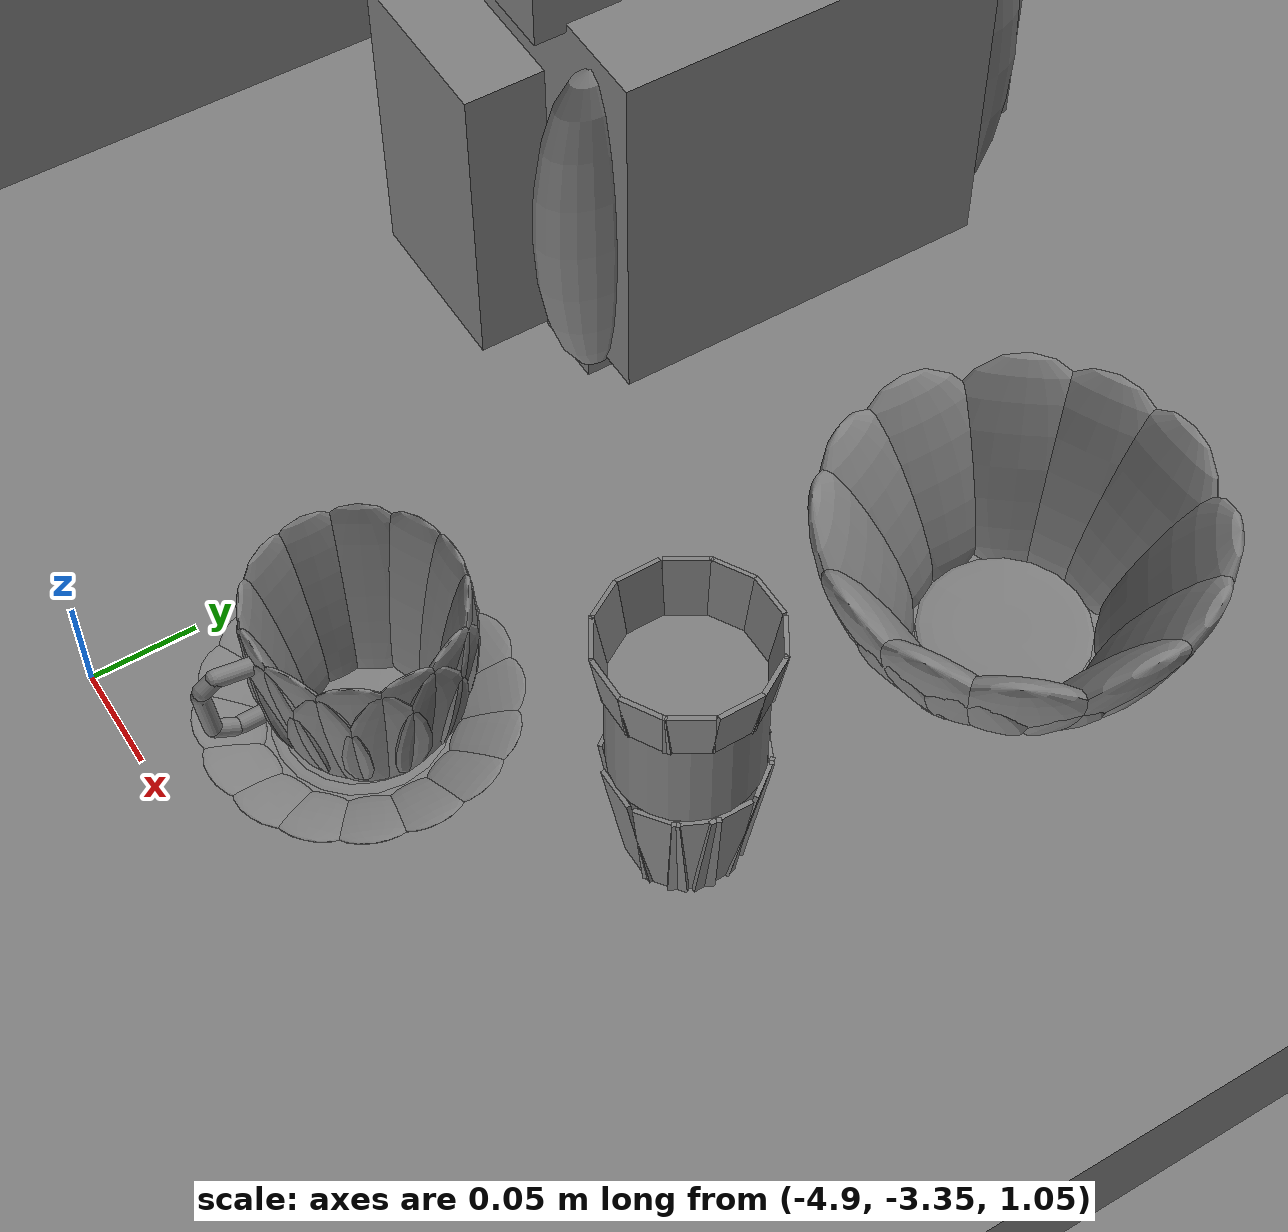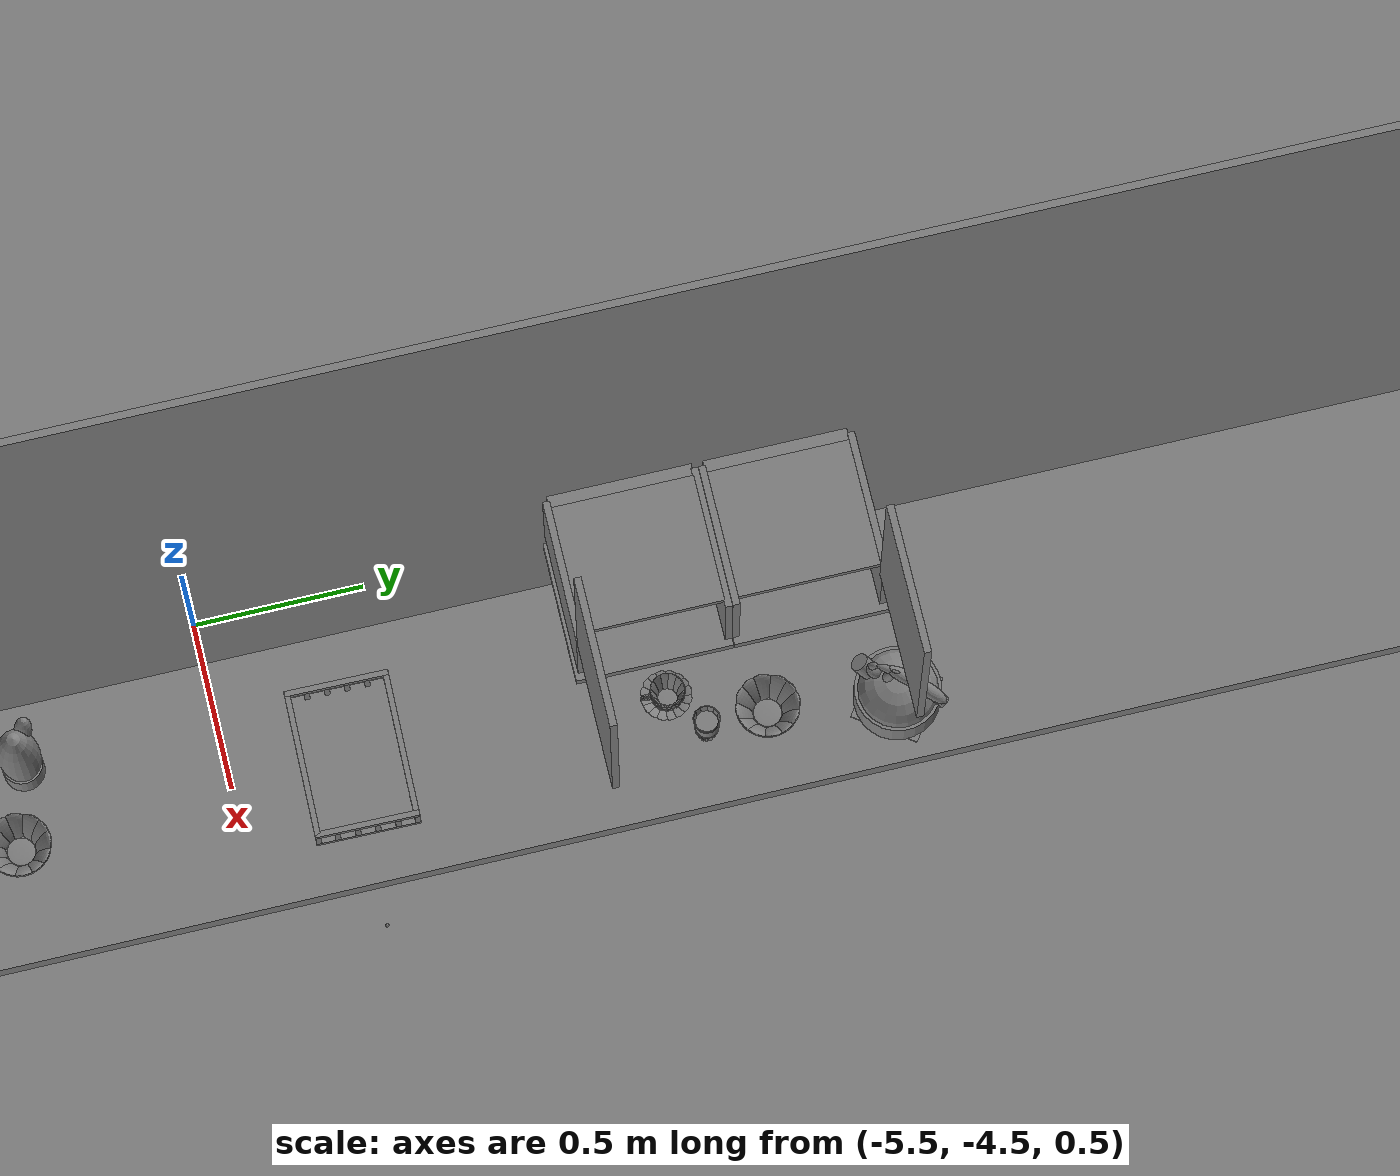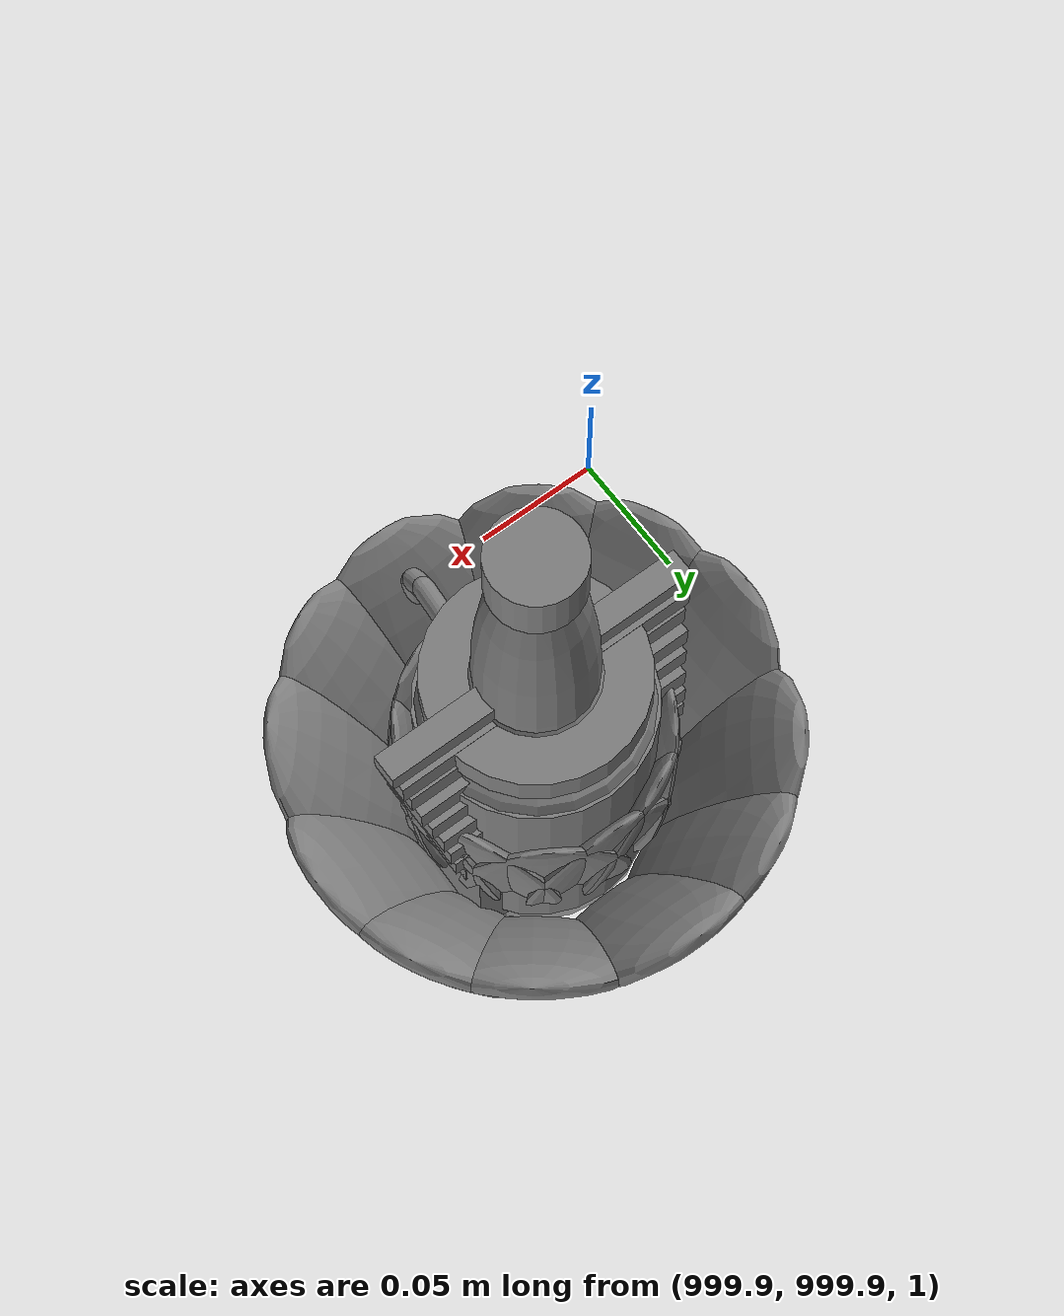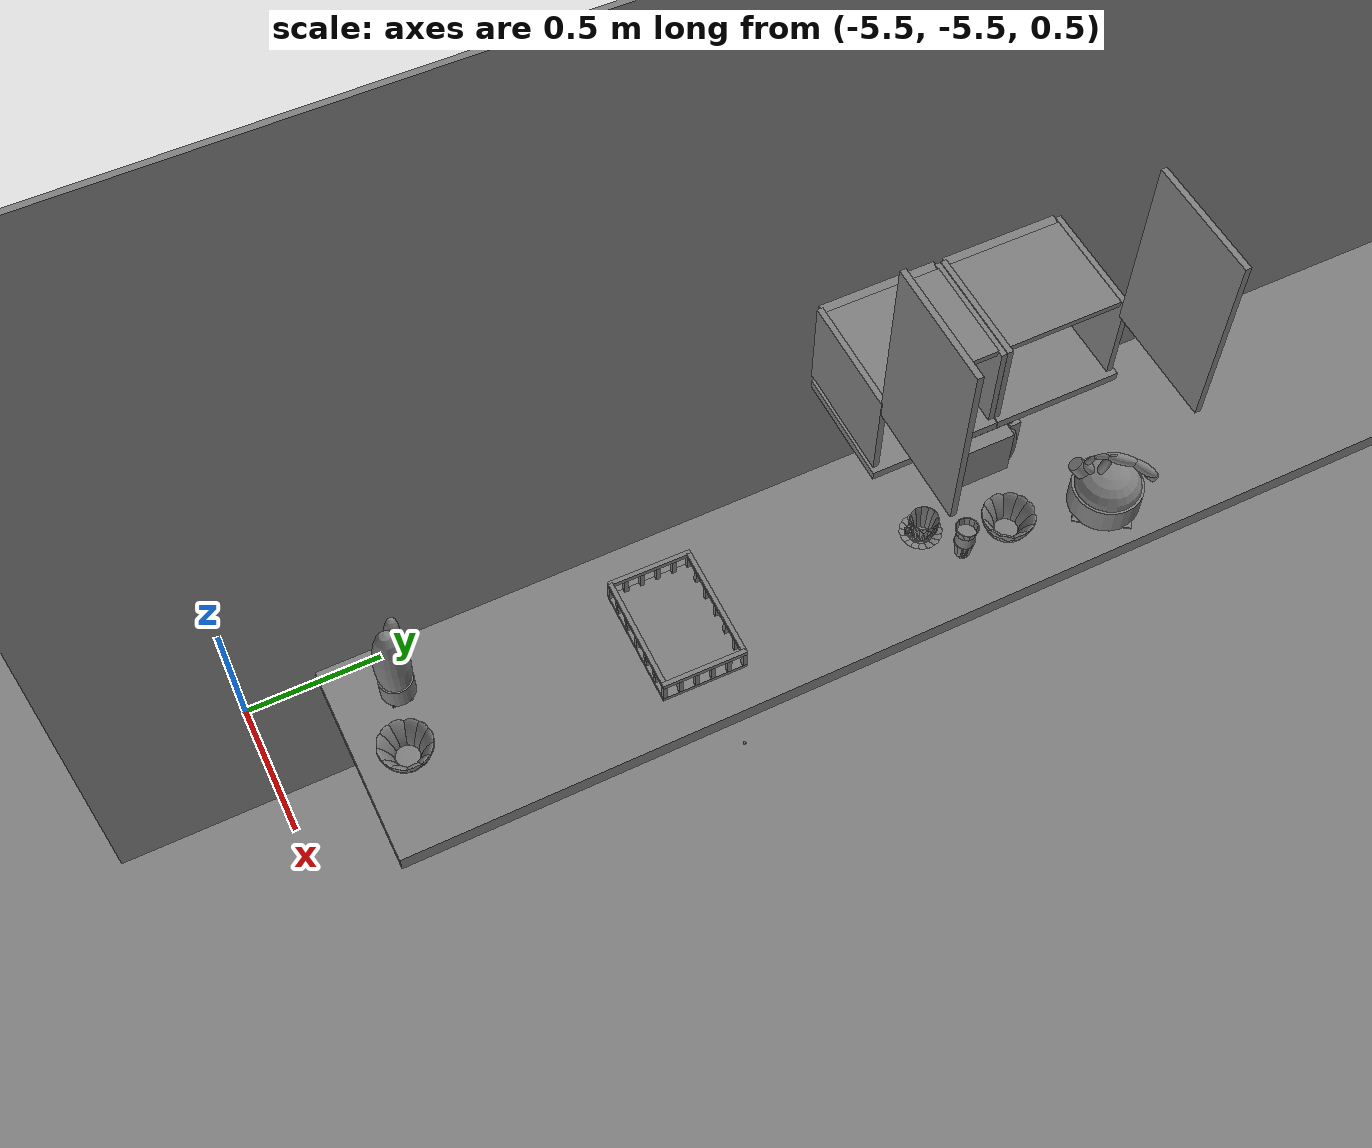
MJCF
<mujoco>
    <option gravity="0.000000000 0.000000000 -9.810000420" timestep="0.0049999999" integrator="implicitfast" density="9.8000002" viscosity="1.8000001e-05" noslip_iterations="10" iterations="100" sdf_iterations="50">
        <flag multiccd="disable"/>
    </option>
    <size memory="1000M"/>
    <compiler coordinate="local"/>
    <worldbody>
        <light cutoff="30" pos="0 1 1" dir="0 -1 -2"/>
        <light cutoff="30" pos="0 -1 1" dir="0 1 -2"/>
        <body pos="-5.046103477 -5.051773071 1.001502514" euler="0.000000000 0.000000000 0.000000000" name="Interactive Objcets_huapen">
            <geom contype="1" conaffinity="1" density="1000" type="ellipsoid" material="" rgba="0.500000000 0.500000000 0.500000000 1.000000000" solimp="0.899999976 0.949999988 0.001000000" friction="1.000000000 0.005000000 0.000100000" solref="0.020000000 1.000000000" margin="0" condim="3" group="0" pos="0.008062840 0.004346371 0.205056787" quat="1.000000000 0.000000000 0.000000000 0.000000000" size="0.059999999 0.059999999 0.180000007" name="Interactive Objcets_huapen_hua_4EB0DAED_03B2_4050_B71F_C7428B1EC392"/>
            <geom contype="1" conaffinity="1" density="1000" type="cylinder" material="" rgba="0.500000000 0.500000000 0.500000000 1.000000000" solimp="0.899999976 0.949999988 0.001000000" friction="1.000000000 0.005000000 0.000100000" solref="0.020000000 1.000000000" margin="0" condim="3" group="0" pos="0.008062840 0.003952026 0.080107450" quat="1.000000000 0.000000000 0.000000000 0.000000000" size="0.057999998 0.039999999 1.000000000" name="Interactive Objcets_huapen_hua_BBC41C10_8F14_4976_96B0_12765971A1BB"/>
            <geom contype="1" conaffinity="1" density="1000" type="box" material="" rgba="0.500000000 0.500000000 0.500000000 1.000000000" solimp="0.899999976 0.949999988 0.001000000" friction="1.000000000 0.005000000 0.000100000" solref="0.020000000 1.000000000" margin="0" condim="3" group="0" pos="0.008062840 0.003952503 0.020566106" quat="1.000000000 0.000000000 0.000000000 0.000000000" size="0.035000000 0.035000000 0.020000000" name="Interactive Objcets_huapen_hua_CA0673DA_25D0_4D90_AB3A_9EBB742964C8"/>
            <geom contype="1" conaffinity="1" density="1000" type="ellipsoid" material="" rgba="0.500000000 0.500000000 0.500000000 1.000000000" solimp="0.899999976 0.949999988 0.001000000" friction="1.000000000 0.005000000 0.000100000" solref="0.020000000 1.000000000" margin="0" condim="3" group="0" pos="-0.029900074 0.033599377 0.321917295" quat="0.992658079 -0.083605267 -0.087364964 0.002748166" size="0.025000000 0.025000000 0.059999999" name="Interactive Objcets_huapen_hua_C762C81A_1F29_4ED6_B1E5_D2C58E1C9774"/>
            <freejoint name="Interactive Objcets_huapen"/>
        </body>
        <body pos="1000.000000000 1000.000000000 1.000000000" euler="0.000000000 0.000000000 0.000000000" name="openloong_gripper_2f85_fix_base_usda_coffeecup_white_kps">
            <geom contype="1" conaffinity="1" density="1000" type="capsule" material="" rgba="0.500000000 0.500000000 0.500000000 1.000000000" solimp="0.899999976 0.949999988 0.001000000" friction="1.000000000 0.005000000 0.000100000" solref="0.020000000 1.000000000" margin="0" condim="3" group="0" pos="-0.000854492 -0.065795898 0.050029993" quat="0.343559504 -0.613204718 0.626912475 0.336047262" size="0.004000000 0.005000000 1.000000000" name="openloong_gripper_2f85_fix_base_usda_geom_07CEE2DB_540C_4368_B82B_5C782FAAF447"/>
            <geom contype="1" conaffinity="1" density="1000" type="ellipsoid" material="" rgba="0.500000000 0.500000000 0.500000000 1.000000000" solimp="0.899999976 0.949999988 0.001000000" friction="1.000000000 0.005000000 0.000100000" solref="0.020000000 1.000000000" margin="0" condim="3" group="0" pos="-0.000793457 -0.038452148 0.048040152" quat="0.711656272 0.066323131 -0.067805752 0.696095467" size="0.005000000 0.029999999 0.048999999" name="openloong_gripper_2f85_fix_base_usda_geom_26F142EA_F889_42A2_A874_71BA96548436"/>
            <geom contype="1" conaffinity="1" density="1000" type="ellipsoid" material="" rgba="0.500000000 0.500000000 0.500000000 1.000000000" solimp="0.899999976 0.949999988 0.001000000" friction="1.000000000 0.005000000 0.000100000" solref="0.020000000 1.000000000" margin="0" condim="3" group="0" pos="0.037719727 -0.001892090 0.048040152" quat="0.995387912 0.001371633 0.094835162 -0.014391154" size="0.005000000 0.029999999 0.048999999" name="openloong_gripper_2f85_fix_base_usda_geom_7BB49DA7_0BF0_49DE_9E78_119D84AFB207"/>
            <geom contype="1" conaffinity="1" density="1000" type="ellipsoid" material="" rgba="0.500000000 0.500000000 0.500000000 1.000000000" solimp="0.899999976 0.949999988 0.001000000" friction="1.000000000 0.005000000 0.000100000" solref="0.020000000 1.000000000" margin="0" condim="3" group="0" pos="0.033996582 0.015502930 0.048040152" quat="0.970659733 -0.021051638 0.092478797 0.220962167" size="0.005000000 0.029999999 0.048999999" name="openloong_gripper_2f85_fix_base_usda_geom_B44C17C6_459A_4E34_984A_AEF3C20A3201"/>
            <geom contype="1" conaffinity="1" density="1000" type="box" material="" rgba="0.500000000 0.500000000 0.500000000 1.000000000" solimp="0.899999976 0.949999988 0.001000000" friction="1.000000000 0.005000000 0.000100000" solref="0.020000000 1.000000000" margin="0" condim="3" group="0" pos="0.000793457 -0.000183105 0.000156164" quat="0.714879215 0.000000000 0.000000000 0.699247897" size="0.020000000 0.020000000 0.002000000" name="openloong_gripper_2f85_fix_base_usda_geom_C694117E_6184_4A77_B0C6_02CF7AD41922"/>
            <geom contype="1" conaffinity="1" density="1000" type="ellipsoid" material="" rgba="0.500000000 0.500000000 0.500000000 1.000000000" solimp="0.899999976 0.949999988 0.001000000" friction="1.000000000 0.005000000 0.000100000" solref="0.020000000 1.000000000" margin="0" condim="3" group="0" pos="-0.019409180 -0.033081055 0.048040152" quat="0.866879702 0.046630561 -0.082595348 0.489411235" size="0.005000000 0.029999999 0.048999999" name="openloong_gripper_2f85_fix_base_usda_geom_1CB73F98_B5DC_4BBC_8840_372A94CBBD9C"/>
            <geom contype="1" conaffinity="1" density="1000" type="ellipsoid" material="" rgba="0.500000000 0.500000000 0.500000000 1.000000000" solimp="0.899999976 0.949999988 0.001000000" friction="1.000000000 0.005000000 0.000100000" solref="0.020000000 1.000000000" margin="0" condim="3" group="0" pos="-0.016052246 0.033264160 0.048040152" quat="0.840792537 -0.050782297 -0.080109790 -0.532983541" size="0.005000000 0.029999999 0.048999999" name="openloong_gripper_2f85_fix_base_usda_geom_D9DDF7BD_B7AF_4043_8A32_ED654D96D9AF"/>
            <geom contype="1" conaffinity="1" density="1000" type="capsule" material="" rgba="0.500000000 0.500000000 0.500000000 1.000000000" solimp="0.899999976 0.949999988 0.001000000" friction="1.000000000 0.005000000 0.000100000" solref="0.020000000 1.000000000" margin="0" condim="3" group="0" pos="-0.000549316 -0.053527832 0.046825886" quat="0.505496025 -0.494442940 0.505495846 0.494442940" size="0.004000000 0.005000000 1.000000000" name="openloong_gripper_2f85_fix_base_usda_geom_07A8A6AC_0A29_4303_985F_E0454C0E0FE8"/>
            <geom contype="1" conaffinity="1" density="1000" type="ellipsoid" material="" rgba="0.500000000 0.500000000 0.500000000 1.000000000" solimp="0.899999976 0.949999988 0.001000000" friction="1.000000000 0.005000000 0.000100000" solref="0.020000000 1.000000000" margin="0" condim="3" group="0" pos="-0.032104492 0.018920898 0.048040152" quat="0.958129764 -0.025742561 -0.091288343 -0.270168930" size="0.005000000 0.029999999 0.048999999" name="openloong_gripper_2f85_fix_base_usda_geom_6FB2542A_CCA6_4CE4_9484_4040651E2ACA"/>
            <geom contype="1" conaffinity="1" density="1000" type="ellipsoid" material="" rgba="0.500000000 0.500000000 0.500000000 1.000000000" solimp="0.899999976 0.949999988 0.001000000" friction="1.000000000 0.005000000 0.000100000" solref="0.020000000 1.000000000" margin="0" condim="3" group="0" pos="-0.037597656 0.000305176 0.048040152" quat="0.995387554 -0.001371440 -0.094839431 -0.014389008" size="0.005000000 0.029999999 0.048999999" name="openloong_gripper_2f85_fix_base_usda_geom_752954C9_02AB_409F_ACA9_73BE83F8ADB3"/>
            <geom contype="1" conaffinity="1" density="1000" type="capsule" material="" rgba="0.500000000 0.500000000 0.500000000 1.000000000" solimp="0.899999976 0.949999988 0.001000000" friction="1.000000000 0.005000000 0.000100000" solref="0.020000000 1.000000000" margin="0" condim="3" group="0" pos="-0.000366211 -0.043762207 0.044118762" quat="0.260488123 -0.651174724 0.665731549 0.254792154" size="0.004000000 0.003000000 1.000000000" name="openloong_gripper_2f85_fix_base_usda_geom_F236CDBF_B231_4974_AC7C_CA6E26C2D130"/>
            <geom contype="1" conaffinity="1" density="1000" type="capsule" material="" rgba="0.500000000 0.500000000 0.500000000 1.000000000" solimp="0.899999976 0.949999988 0.001000000" friction="1.000000000 0.005000000 0.000100000" solref="0.020000000 1.000000000" margin="0" condim="3" group="0" pos="-0.000915527 -0.068542480 0.082936406" quat="0.624995589 -0.339446366 0.347034454 0.611329615" size="0.004000000 0.004000000 1.000000000" name="openloong_gripper_2f85_fix_base_usda_geom_AA205AD0_4577_4290_B624_E8E3C0721F9B"/>
            <geom contype="1" conaffinity="1" density="1000" type="ellipsoid" material="" rgba="0.500000000 0.500000000 0.500000000 1.000000000" solimp="0.899999976 0.949999988 0.001000000" friction="1.000000000 0.005000000 0.000100000" solref="0.020000000 1.000000000" margin="0" condim="3" group="0" pos="0.016113281 -0.034851074 0.048040152" quat="0.840793252 0.050779939 0.080106191 -0.532983422" size="0.005000000 0.029999999 0.048999999" name="openloong_gripper_2f85_fix_base_usda_geom_A4A5093C_4F67_40D8_9326_B24CE9F53D66"/>
            <geom contype="1" conaffinity="1" density="1000" type="ellipsoid" material="" rgba="0.500000000 0.500000000 0.500000000 1.000000000" solimp="0.899999976 0.949999988 0.001000000" friction="1.000000000 0.005000000 0.000100000" solref="0.020000000 1.000000000" margin="0" condim="3" group="0" pos="0.000854492 0.036865234 0.048040152" quat="0.711656570 -0.066320375 0.067802906 0.696095705" size="0.005000000 0.029999999 0.048999999" name="openloong_gripper_2f85_fix_base_usda_geom_078CD85B_0A57_4C1B_97DD_25517BA239BA"/>
            <geom contype="1" conaffinity="1" density="1000" type="ellipsoid" material="" rgba="0.500000000 0.500000000 0.500000000 1.000000000" solimp="0.899999976 0.949999988 0.001000000" friction="1.000000000 0.005000000 0.000100000" solref="0.020000000 1.000000000" margin="0" condim="3" group="0" pos="-0.033935547 -0.017089844 0.048040152" quat="0.970659137 0.021052625 -0.092483103 0.220962465" size="0.005000000 0.029999999 0.048999999" name="openloong_gripper_2f85_fix_base_usda_geom_57C20458_64B3_4DB7_A742_382DFC8B4BDA"/>
            <geom contype="1" conaffinity="1" density="1000" type="ellipsoid" material="" rgba="0.500000000 0.500000000 0.500000000 1.000000000" solimp="0.899999976 0.949999988 0.001000000" friction="1.000000000 0.005000000 0.000100000" solref="0.020000000 1.000000000" margin="0" condim="3" group="0" pos="0.019531250 0.031494141 0.048040152" quat="0.866880119 -0.046628602 0.082591817 0.489411235" size="0.005000000 0.029999999 0.048999999" name="openloong_gripper_2f85_fix_base_usda_geom_76D817F2_9A29_4ABE_B3CB_FC3E9C67483F"/>
            <geom contype="1" conaffinity="1" density="1000" type="ellipsoid" material="" rgba="0.500000000 0.500000000 0.500000000 1.000000000" solimp="0.899999976 0.949999988 0.001000000" friction="1.000000000 0.005000000 0.000100000" solref="0.020000000 1.000000000" margin="0" condim="3" group="0" pos="0.032165527 -0.020507812 0.048040152" quat="0.958128154 0.025740955 0.091285400 -0.270175666" size="0.005000000 0.029999999 0.048999999" name="openloong_gripper_2f85_fix_base_usda_geom_5A46C975_7B46_49C7_A526_0503C54EBC50"/>
            <geom contype="1" conaffinity="1" density="1000" type="capsule" material="" rgba="0.500000000 0.500000000 0.500000000 1.000000000" solimp="0.899999976 0.949999988 0.001000000" friction="1.000000000 0.005000000 0.000100000" solref="0.020000000 1.000000000" margin="0" condim="3" group="0" pos="-0.000610352 -0.056823730 0.083572865" quat="0.452654332 -0.541215360 0.553313971 0.442756712" size="0.004000000 0.009000000 1.000000000" name="openloong_gripper_2f85_fix_base_usda_geom_DC5F65A9_1E12_4BAF_8AAE_2A973A10FA1C"/>
            <geom contype="1" conaffinity="1" density="1000" type="ellipsoid" material="" rgba="0.500000000 0.500000000 0.500000000 1.000000000" solimp="0.899999976 0.949999988 0.001000000" friction="1.000000000 0.005000000 0.000100000" solref="0.020000000 1.000000000" margin="0" condim="3" group="0" pos="0.000061035 -0.000183105 0.001848221" quat="0.714879215 0.000000000 0.000000000 0.699247897" size="0.029999999 0.029999999 0.001000000" name="openloong_gripper_2f85_fix_base_usda_geom_FF22BDD8_1AB2_43DC_854F_C46C0DA9DE0E"/>
            <geom contype="1" conaffinity="1" density="1000" type="capsule" material="" rgba="0.500000000 0.500000000 0.500000000 1.000000000" solimp="0.899999976 0.949999988 0.001000000" friction="1.000000000 0.005000000 0.000100000" solref="0.020000000 1.000000000" margin="0" condim="3" group="0" pos="-0.000976562 -0.071838379 0.066101432" quat="0.031849027 -0.698553741 0.714169443 0.031152546" size="0.004000000 0.012000000 1.000000000" name="openloong_gripper_2f85_fix_base_usda_geom_4AF9C1BB_E091_46BC_A9FF_963436DE0B91"/>
            <freejoint name="openloong_gripper_2f85_fix_base_usda_coffeecup_white_kps_joint"/>
            <site size="0.005000000 0.005000000 0.005000000" rgba="0.500000000 0.500000000 0.500000000 1.000000000" pos="0.000000000 0.000000000 0.000000000" quat="0.999961913 0.008726534 0.000000000 0.000000000" group="0" type="sphere" name="openloong_gripper_2f85_fix_base_usda_coffeecup_white_kps"/>
        </body>
        <body pos="-4.375150681 -4.063759804 1.884021878" euler="-169.377136230 5.360033989 150.992858887" mocap="true" name="spotlight6_SpotLight"/>
        <body pos="-4.332620621 -4.340872765 1.757160544" euler="-115.148475647 -72.703590393 13.709980965" mocap="true" name="spotlight4_SpotLight"/>
        <body pos="1000.000000000 1000.000000000 1.000000000" euler="0.000000000 0.000000000 0.000000000" name="openloong_gripper_2f85_fix_base_usda_bow_yellow_kps">
            <geom contype="1" conaffinity="1" density="1000" type="ellipsoid" material="" rgba="0.500000000 0.500000000 0.500000000 1.000000000" solimp="0.899999976 0.949999988 0.001000000" friction="1.000000000 0.005000000 0.000100000" solref="0.020000000 1.000000000" margin="0" condim="3" group="0" pos="-0.052185059 0.040283203 0.044118762" quat="0.919264615 -0.076883033 -0.225593656 -0.313287765" size="0.010000000 0.039999999 0.052000001" name="openloong_gripper_2f85_fix_base_usda_geom_0FBD65F5_132B_4C92_9FFE_52544CE5FF7F"/>
            <geom contype="1" conaffinity="1" density="1000" type="ellipsoid" material="" rgba="0.500000000 0.500000000 0.500000000 1.000000000" solimp="0.899999976 0.949999988 0.001000000" friction="1.000000000 0.005000000 0.000100000" solref="0.020000000 1.000000000" margin="0" condim="3" group="0" pos="-0.000061035 0.065979004 0.044118762" quat="0.687598765 -0.168314874 -0.168741167 -0.685860336" size="0.010000000 0.039999999 0.052000001" name="openloong_gripper_2f85_fix_base_usda_geom_72076795_3181_4AF8_A1D4_07F951EF0A16"/>
            <geom contype="1" conaffinity="1" density="1000" type="box" material="" rgba="0.500000000 0.500000000 0.500000000 1.000000000" solimp="0.899999976 0.949999988 0.001000000" friction="1.000000000 0.005000000 0.000100000" solref="0.020000000 1.000000000" margin="0" condim="3" group="0" pos="0.000061035 0.000000000 -0.002001643" quat="1.000000000 0.000000000 0.000000000 0.000000000" size="0.029999999 0.029999999 0.002000000" name="openloong_gripper_2f85_fix_base_usda_geom_3548E29A_B3F1_464C_BD5C_4182F9F15DCB"/>
            <geom contype="1" conaffinity="1" density="1000" type="ellipsoid" material="" rgba="0.500000000 0.500000000 0.500000000 1.000000000" solimp="0.899999976 0.949999988 0.001000000" friction="1.000000000 0.005000000 0.000100000" solref="0.020000000 1.000000000" margin="0" condim="3" group="0" pos="0.029418945 -0.059082031 0.044118762" quat="0.825555861 0.125530601 0.202597082 -0.511521280" size="0.010000000 0.039999999 0.052000001" name="openloong_gripper_2f85_fix_base_usda_geom_CA385805_1760_43FF_BAFB_E4A4AB2B2F63"/>
            <geom contype="1" conaffinity="1" density="1000" type="ellipsoid" material="" rgba="0.500000000 0.500000000 0.500000000 1.000000000" solimp="0.899999976 0.949999988 0.001000000" friction="1.000000000 0.005000000 0.000100000" solref="0.020000000 1.000000000" margin="0" condim="3" group="0" pos="0.000244141 -0.065979004 0.044118762" quat="0.687598765 0.168314651 0.168741375 -0.685860336" size="0.010000000 0.039999999 0.052000001" name="openloong_gripper_2f85_fix_base_usda_geom_AB0AA1C8_6FD1_4A4A_B9D2_F2511D3C29A4"/>
            <geom contype="1" conaffinity="1" density="1000" type="ellipsoid" material="" rgba="0.500000000 0.500000000 0.500000000 1.000000000" solimp="0.899999976 0.949999988 0.001000000" friction="1.000000000 0.005000000 0.000100000" solref="0.020000000 1.000000000" margin="0" condim="3" group="0" pos="0.000061035 0.000000000 0.000446677" quat="1.000000000 0.000000000 0.000000000 0.000000000" size="0.039999999 0.039999999 0.002000000" name="openloong_gripper_2f85_fix_base_usda_geom_09C81A5A_6CDB_4501_A4C4_4F32C71D24B6"/>
            <geom contype="1" conaffinity="1" density="1000" type="ellipsoid" material="" rgba="0.500000000 0.500000000 0.500000000 1.000000000" solimp="0.899999976 0.949999988 0.001000000" friction="1.000000000 0.005000000 0.000100000" solref="0.020000000 1.000000000" margin="0" condim="3" group="0" pos="0.059082031 0.029541016 0.044118762" quat="0.223252773 -0.231952220 -0.054787423 -0.945174456" size="0.010000000 0.039999999 0.052000001" name="openloong_gripper_2f85_fix_base_usda_geom_F96B9D91_9FEB_492F_82E2_F2D494D53560"/>
            <geom contype="1" conaffinity="1" density="1000" type="ellipsoid" material="" rgba="0.500000000 0.500000000 0.500000000 1.000000000" solimp="0.899999976 0.949999988 0.001000000" friction="1.000000000 0.005000000 0.000100000" solref="0.020000000 1.000000000" margin="0" condim="3" group="0" pos="0.000061035 0.000000000 0.007335305" quat="1.000000000 0.000000000 0.000000000 0.000000000" size="0.039999999 0.039999999 0.002000000" name="openloong_gripper_2f85_fix_base_usda_geom_0E678F4A_B697_41E4_A0A3_0A5D7284C24A"/>
            <geom contype="1" conaffinity="1" density="1000" type="ellipsoid" material="" rgba="0.500000000 0.500000000 0.500000000 1.000000000" solimp="0.899999976 0.949999988 0.001000000" friction="1.000000000 0.005000000 0.000100000" solref="0.020000000 1.000000000" margin="0" condim="3" group="0" pos="-0.029296875 0.059082031 0.044118762" quat="0.825555861 -0.125530809 -0.202596918 -0.511521280" size="0.010000000 0.039999999 0.052000001" name="openloong_gripper_2f85_fix_base_usda_geom_810C5382_71BA_4433_9EC4_2CC57AA1B2BB"/>
            <geom contype="1" conaffinity="1" density="1000" type="ellipsoid" material="" rgba="0.500000000 0.500000000 0.500000000 1.000000000" solimp="0.899999976 0.949999988 0.001000000" friction="1.000000000 0.005000000 0.000100000" solref="0.020000000 1.000000000" margin="0" condim="3" group="0" pos="0.040222168 0.052368164 0.044118762" quat="0.429593176 -0.213750049 -0.105424821 -0.871002972" size="0.010000000 0.039999999 0.052000001" name="openloong_gripper_2f85_fix_base_usda_geom_490C1278_AFB1_4C17_86A6_F9C2E663B0B3"/>
            <geom contype="1" conaffinity="1" density="1000" type="ellipsoid" material="" rgba="0.500000000 0.500000000 0.500000000 1.000000000" solimp="0.899999976 0.949999988 0.001000000" friction="1.000000000 0.005000000 0.000100000" solref="0.020000000 1.000000000" margin="0" condim="3" group="0" pos="0.066040039 0.000000000 0.044118762" quat="0.971183062 -0.000000156 0.238334835 0.000000030" size="0.010000000 0.039999999 0.052000001" name="openloong_gripper_2f85_fix_base_usda_geom_0FDEC3D6_F99E_4A04_975A_7F75BC673D48"/>
            <geom contype="1" conaffinity="1" density="1000" type="ellipsoid" material="" rgba="0.500000000 0.500000000 0.500000000 1.000000000" solimp="0.899999976 0.949999988 0.001000000" friction="1.000000000 0.005000000 0.000100000" solref="0.020000000 1.000000000" margin="0" condim="3" group="0" pos="0.052307129 -0.040283203 0.044118762" quat="0.919264674 0.076882750 0.225593731 -0.313287705" size="0.010000000 0.039999999 0.052000001" name="openloong_gripper_2f85_fix_base_usda_geom_AECD3327_4D21_4FA1_9EF1_E842FBD77C74"/>
            <geom contype="1" conaffinity="1" density="1000" type="ellipsoid" material="" rgba="0.500000000 0.500000000 0.500000000 1.000000000" solimp="0.899999976 0.949999988 0.001000000" friction="1.000000000 0.005000000 0.000100000" solref="0.020000000 1.000000000" margin="0" condim="3" group="0" pos="-0.065917969 0.000000000 0.044118762" quat="0.971183062 -0.000000142 -0.238334835 0.000000030" size="0.010000000 0.039999999 0.052000001" name="openloong_gripper_2f85_fix_base_usda_geom_A3611F9B_5926_4E0D_B576_8F0825C97C3B"/>
            <geom contype="1" conaffinity="1" density="1000" type="ellipsoid" material="" rgba="0.500000000 0.500000000 0.500000000 1.000000000" solimp="0.899999976 0.949999988 0.001000000" friction="1.000000000 0.005000000 0.000100000" solref="0.020000000 1.000000000" margin="0" condim="3" group="0" pos="-0.058898926 -0.029541016 0.044118762" quat="0.223252758 0.231952101 0.054787733 -0.945174575" size="0.010000000 0.039999999 0.052000001" name="openloong_gripper_2f85_fix_base_usda_geom_5A8385F3_56DA_4F83_934C_DAFA577BDA4B"/>
            <geom contype="1" conaffinity="1" density="1000" type="ellipsoid" material="" rgba="0.500000000 0.500000000 0.500000000 1.000000000" solimp="0.899999976 0.949999988 0.001000000" friction="1.000000000 0.005000000 0.000100000" solref="0.020000000 1.000000000" margin="0" condim="3" group="0" pos="-0.040100098 -0.052368164 0.044118762" quat="0.429593235 0.213749886 0.105425082 -0.871003032" size="0.010000000 0.039999999 0.052000001" name="openloong_gripper_2f85_fix_base_usda_geom_FBDF5FF0_02B3_4D89_9F90_27AF2B784B5D"/>
            <freejoint name="openloong_gripper_2f85_fix_base_usda_bow_yellow_kps_joint"/>
            <site size="0.005000000 0.005000000 0.005000000" rgba="0.500000000 0.500000000 0.500000000 1.000000000" pos="0.000000000 0.000000000 0.000000000" quat="0.999961913 0.008726534 0.000000000 0.000000000" group="0" type="sphere" name="openloong_gripper_2f85_fix_base_usda_bow_yellow_kps"/>
        </body>
        <body pos="1000.000000000 1000.000000000 1.000000000" euler="0.000000000 0.000000000 0.000000000" name="openloong_gripper_2f85_fix_base_usda_jar_01">
            <geom contype="1" conaffinity="1" density="1000" type="box" material="" rgba="0.500000000 0.500000000 0.500000000 1.000000000" solimp="0.899999976 0.949999988 0.001000000" friction="1.000000000 0.005000000 0.000100000" solref="0.020000000 1.000000000" margin="0" condim="3" group="0" pos="0.000000000 0.000000000 0.006158113" quat="1.000000000 0.000000000 0.000000000 0.000000000" size="0.020000000 0.020000000 0.005000000" name="openloong_gripper_2f85_fix_base_usda_geom_F8960F79_5305_4E07_9732_F8C92BDD50F3"/>
            <geom contype="1" conaffinity="1" density="1000" type="cylinder" material="" rgba="0.500000000 0.500000000 0.500000000 1.000000000" solimp="0.899999976 0.949999988 0.001000000" friction="1.000000000 0.005000000 0.000100000" solref="0.020000000 1.000000000" margin="0" condim="3" group="0" pos="0.000000000 0.000000000 0.062744498" quat="1.000000000 0.000000000 0.000000000 0.000000000" size="0.041000001 0.052999999 1.000000000" name="openloong_gripper_2f85_fix_base_usda_geom_6DBDDA75_0764_4BF6_842E_9ACF8A7405F1"/>
            <geom contype="1" conaffinity="1" density="1000" type="ellipsoid" material="" rgba="0.500000000 0.500000000 0.500000000 1.000000000" solimp="0.899999976 0.949999988 0.001000000" friction="1.000000000 0.005000000 0.000100000" solref="0.020000000 1.000000000" margin="0" condim="3" group="0" pos="0.000000000 0.000000000 0.122252703" quat="1.000000000 0.000000000 0.000000000 0.000000000" size="0.035999998 0.035999998 0.010000000" name="openloong_gripper_2f85_fix_base_usda_geom_6E492A31_988C_4E2F_99E7_6EDFE6BE5354"/>
            <geom contype="1" conaffinity="1" density="1000" type="cylinder" material="" rgba="0.500000000 0.500000000 0.500000000 1.000000000" solimp="0.899999976 0.949999988 0.001000000" friction="1.000000000 0.005000000 0.000100000" solref="0.020000000 1.000000000" margin="0" condim="3" group="0" pos="0.000000000 0.000000000 0.015747190" quat="1.000000000 0.000000000 0.000000000 0.000000000" size="0.035000000 0.010000000 1.000000000" name="openloong_gripper_2f85_fix_base_usda_geom_4E023154_958C_466D_A905_4D854B1A315D"/>
            <geom contype="1" conaffinity="1" density="1000" type="ellipsoid" material="" rgba="0.500000000 0.500000000 0.500000000 1.000000000" solimp="0.899999976 0.949999988 0.001000000" friction="1.000000000 0.005000000 0.000100000" solref="0.020000000 1.000000000" margin="0" condim="3" group="0" pos="0.000000000 0.000000000 0.115815401" quat="1.000000000 0.000000000 0.000000000 0.000000000" size="0.039999999 0.039999999 0.010000000" name="openloong_gripper_2f85_fix_base_usda_geom_83BF8341_45B3_4CE9_A4E6_B9D2448089E9"/>
            <geom contype="1" conaffinity="1" density="1000" type="cylinder" material="" rgba="0.500000000 0.500000000 0.500000000 1.000000000" solimp="0.899999976 0.949999988 0.001000000" friction="1.000000000 0.005000000 0.000100000" solref="0.020000000 1.000000000" margin="0" condim="3" group="0" pos="0.000000000 0.000000000 0.133183479" quat="1.000000000 0.000000000 0.000000000 0.000000000" size="0.037999999 0.006500000 1.000000000" name="openloong_gripper_2f85_fix_base_usda_geom_3441BFC1_0682_4A15_829A_375C9CBF9A77"/>
            <freejoint name="openloong_gripper_2f85_fix_base_usda_jar_01_joint"/>
            <site size="0.005000000 0.005000000 0.005000000" rgba="0.500000000 0.500000000 0.500000000 1.000000000" pos="0.000000000 0.000000000 0.000000000" quat="1.000000000 0.000000000 0.000000000 0.000000000" group="0" type="sphere" name="openloong_gripper_2f85_fix_base_usda_jar_01site"/>
        </body>
        <body pos="1000.000000000 1000.000000000 1.000000000" euler="0.000000000 0.000000000 0.000000000" name="openloong_gripper_2f85_fix_base_usda_salt">
            <geom contype="1" conaffinity="1" density="1000" type="box" material="" rgba="0.500000000 0.500000000 0.500000000 1.000000000" solimp="0.899999976 0.949999988 0.001000000" friction="1.000000000 0.005000000 0.000100000" solref="0.020000000 1.000000000" margin="0" condim="3" group="0" pos="0.000305176 0.000000000 0.084862232" quat="1.000000000 0.000000000 0.000000000 0.000000000" size="0.048999999 0.018999999 0.005000000" name="openloong_gripper_2f85_fix_base_usda_geom_15F3F30B_49B3_47DE_BB12_EA96CB505284"/>
            <geom contype="1" conaffinity="1" density="1000" type="box" material="" rgba="0.500000000 0.500000000 0.500000000 1.000000000" solimp="0.899999976 0.949999988 0.001000000" friction="1.000000000 0.005000000 0.000100000" solref="0.020000000 1.000000000" margin="0" condim="3" group="0" pos="0.000305176 0.000000000 0.104564309" quat="1.000000000 0.000000000 0.000000000 0.000000000" size="0.052000001 0.014000000 0.005000000" name="openloong_gripper_2f85_fix_base_usda_geom_48AFDD3D_6C46_408E_A2F0_0A7723DCA819"/>
            <geom contype="1" conaffinity="1" density="1000" type="box" material="" rgba="0.500000000 0.500000000 0.500000000 1.000000000" solimp="0.899999976 0.949999988 0.001000000" friction="1.000000000 0.005000000 0.000100000" solref="0.020000000 1.000000000" margin="0" condim="3" group="0" pos="0.000305176 0.000000000 0.114487171" quat="1.000000000 0.000000000 0.000000000 0.000000000" size="0.054000001 0.011500000 0.005000000" name="openloong_gripper_2f85_fix_base_usda_geom_69533217_3DCB_49EB_8559_C4E43260F907"/>
            <geom contype="1" conaffinity="1" density="1000" type="box" material="" rgba="0.500000000 0.500000000 0.500000000 1.000000000" solimp="0.899999976 0.949999988 0.001000000" friction="1.000000000 0.005000000 0.000100000" solref="0.020000000 1.000000000" margin="0" condim="3" group="0" pos="0.000305176 0.000000000 0.075103164" quat="1.000000000 0.000000000 0.000000000 0.000000000" size="0.048000000 0.020000000 0.005000000" name="openloong_gripper_2f85_fix_base_usda_geom_99890B39_D02C_46D0_BB6B_F706D336D481"/>
            <geom contype="1" conaffinity="1" density="1000" type="box" material="" rgba="0.500000000 0.500000000 0.500000000 1.000000000" solimp="0.899999976 0.949999988 0.001000000" friction="1.000000000 0.005000000 0.000100000" solref="0.020000000 1.000000000" margin="0" condim="3" group="0" pos="0.000305176 0.000000000 0.134892464" quat="1.000000000 0.000000000 0.000000000 0.000000000" size="0.057000000 0.007000000 0.005000000" name="openloong_gripper_2f85_fix_base_usda_geom_E0A2FC8D_9025_432C_97C8_9D849C191305"/>
            <geom contype="1" conaffinity="1" density="1000" type="box" material="" rgba="0.500000000 0.500000000 0.500000000 1.000000000" solimp="0.899999976 0.949999988 0.001000000" friction="1.000000000 0.005000000 0.000100000" solref="0.020000000 1.000000000" margin="0" condim="3" group="0" pos="0.000305176 0.000000000 0.094920278" quat="1.000000000 0.000000000 0.000000000 0.000000000" size="0.050000001 0.017000001 0.005000000" name="openloong_gripper_2f85_fix_base_usda_geom_70B1C8B6_51C8_421A_86D7_2B33E9F1DE31"/>
            <geom contype="1" conaffinity="1" density="1000" type="box" material="" rgba="0.500000000 0.500000000 0.500000000 1.000000000" solimp="0.899999976 0.949999988 0.001000000" friction="1.000000000 0.005000000 0.000100000" solref="0.020000000 1.000000000" margin="0" condim="3" group="0" pos="0.000305176 0.000000000 0.065204859" quat="1.000000000 0.000000000 0.000000000 0.000000000" size="0.045000002 0.021000000 0.005000000" name="openloong_gripper_2f85_fix_base_usda_geom_6FC3AECE_F0C9_41DA_B54B_C9D1AE367C03"/>
            <geom contype="1" conaffinity="1" density="1000" type="box" material="" rgba="0.500000000 0.500000000 0.500000000 1.000000000" solimp="0.899999976 0.949999988 0.001000000" friction="1.000000000 0.005000000 0.000100000" solref="0.020000000 1.000000000" margin="0" condim="3" group="0" pos="0.000305176 0.000000000 0.144135714" quat="1.000000000 0.000000000 0.000000000 0.000000000" size="0.059000000 0.005000000 0.004000000" name="openloong_gripper_2f85_fix_base_usda_geom_A987191B_A44B_4DD7_AB41_8D993629B2D2"/>
            <geom contype="1" conaffinity="1" density="1000" type="box" material="" rgba="0.500000000 0.500000000 0.500000000 1.000000000" solimp="0.899999976 0.949999988 0.001000000" friction="1.000000000 0.005000000 0.000100000" solref="0.020000000 1.000000000" margin="0" condim="3" group="0" pos="0.000000000 0.000000000 0.031593561" quat="1.000000000 0.000000000 0.000000000 0.000000000" size="0.041999999 0.024000000 0.029999999" name="openloong_gripper_2f85_fix_base_usda_geom_D5C6BCD3_0CE9_4ED0_811F_A91FC6F036F4"/>
            <geom contype="1" conaffinity="1" density="1000" type="box" material="" rgba="0.500000000 0.500000000 0.500000000 1.000000000" solimp="0.899999976 0.949999988 0.001000000" friction="1.000000000 0.005000000 0.000100000" solref="0.020000000 1.000000000" margin="0" condim="3" group="0" pos="0.000305176 0.000000000 0.124608755" quat="1.000000000 0.000000000 0.000000000 0.000000000" size="0.055000000 0.008000000 0.005000000" name="openloong_gripper_2f85_fix_base_usda_geom_5CF02281_E95F_428D_B67E_607FBCB78629"/>
            <freejoint name="openloong_gripper_2f85_fix_base_usda_salt_joint"/>
            <site size="0.005000000 0.005000000 0.005000000" rgba="0.500000000 0.500000000 0.500000000 1.000000000" pos="0.000000000 0.000000000 0.000000000" quat="1.000000000 0.000000000 0.000000000 0.000000000" group="0" type="sphere" name="openloong_gripper_2f85_fix_base_usda_saltsite"/>
        </body>
        <body pos="-3.971405506 -3.687348127 1.888151646" euler="-42.292835236 16.933040619 168.634979248" mocap="true" name="spotlight1_SpotLight"/>
        <body pos="1000.000000000 1000.000000000 1.000000000" euler="0.000000000 0.000000000 0.000000000" name="openloong_gripper_2f85_fix_base_usda_bottle_red">
            <geom contype="1" conaffinity="1" density="1000" type="ellipsoid" material="" rgba="0.500000000 0.500000000 0.500000000 1.000000000" solimp="0.899999976 0.949999988 0.001000000" friction="1.000000000 0.005000000 0.000100000" solref="0.020000000 1.000000000" margin="0" condim="3" group="0" pos="0.000000000 0.000000000 0.144284487" quat="1.000000000 0.000000000 0.000000000 0.000000000" size="0.021000000 0.021000000 0.079999998" name="openloong_gripper_2f85_fix_base_usda_geom_9CB07421_5AB7_437F_BDD3_4F74580E4586"/>
            <geom contype="1" conaffinity="1" density="1000" type="cylinder" material="" rgba="0.500000000 0.500000000 0.500000000 1.000000000" solimp="0.899999976 0.949999988 0.001000000" friction="1.000000000 0.005000000 0.000100000" solref="0.020000000 1.000000000" margin="0" condim="3" group="0" pos="0.000000000 0.000000000 0.220618963" quat="1.000000000 0.000000000 0.000000000 0.000000000" size="0.016000001 0.010000000 1.000000000" name="openloong_gripper_2f85_fix_base_usda_geom_90EA23B9_5A25_4D6D_9EFA_A4397ACCED1B"/>
            <geom contype="1" conaffinity="1" density="1000" type="ellipsoid" material="" rgba="0.500000000 0.500000000 0.500000000 1.000000000" solimp="0.899999976 0.949999988 0.001000000" friction="1.000000000 0.005000000 0.000100000" solref="0.020000000 1.000000000" margin="0" condim="3" group="0" pos="0.000000000 0.000000000 0.118945479" quat="1.000000000 0.000000000 0.000000000 0.000000000" size="0.030999999 0.030999999 0.029999999" name="openloong_gripper_2f85_fix_base_usda_geom_42936A2F_1C20_4E4F_9002_5DEA4A4B4032"/>
            <geom contype="1" conaffinity="1" density="1000" type="box" material="" rgba="0.500000000 0.500000000 0.500000000 1.000000000" solimp="0.899999976 0.949999988 0.001000000" friction="1.000000000 0.005000000 0.000100000" solref="0.020000000 1.000000000" margin="0" condim="3" group="0" pos="0.000000000 0.000000000 0.002189159" quat="1.000000000 0.000000000 0.000000000 0.000000000" size="0.020000000 0.020000000 0.003000000" name="openloong_gripper_2f85_fix_base_usda_geom_5E71C403_1D97_4E34_9896_553CC41F6F07"/>
            <geom contype="1" conaffinity="1" density="1000" type="cylinder" material="" rgba="0.500000000 0.500000000 0.500000000 1.000000000" solimp="0.899999976 0.949999988 0.001000000" friction="1.000000000 0.005000000 0.000100000" solref="0.020000000 1.000000000" margin="0" condim="3" group="0" pos="0.000000000 -0.000366211 0.060884237" quat="1.000000000 0.000000000 0.000000000 0.000000000" size="0.030999999 0.057999998 1.000000000" name="openloong_gripper_2f85_fix_base_usda_geom_ED09FC88_DAE0_4A85_A46E_DE2125243300"/>
            <freejoint name="openloong_gripper_2f85_fix_base_usda_bottle_red_joint"/>
            <site size="0.005000000 0.005000000 0.005000000" rgba="0.500000000 0.500000000 0.500000000 1.000000000" pos="0.000000000 0.000000000 0.000000000" quat="0.999961913 0.008726535 0.000000000 0.000000000" group="0" type="sphere" name="openloong_gripper_2f85_fix_base_usda_bottle_redsite"/>
        </body>
        <body pos="0.000000000 0.000000000 0.000000000" euler="0.000000000 0.000000000 0.000000000" name="Static Objcets_Static Objcets">
            <geom contype="1" conaffinity="1" density="1000" type="box" material="" rgba="0.500000000 0.500000000 0.500000000 1.000000000" solimp="0.899999976 0.949999988 0.001000000" friction="1.000000000 0.005000000 0.000100000" solref="0.020000000 1.000000000" margin="0" condim="3" group="0" pos="-4.999745846 -3.497932911 1.764780521" quat="0.707107067 0.707106471 0.000000000 0.000000000" size="0.200000003 0.159999996 0.010000000" name="Static Objcets_geom_93955DD9_CC6F_4B74_A459_158135F13782"/>
            <geom contype="1" conaffinity="1" density="1000" type="box" material="" rgba="0.500000000 0.500000000 0.500000000 1.000000000" solimp="0.899999976 0.949999988 0.001000000" friction="1.000000000 0.005000000 0.000100000" solref="0.020000000 1.000000000" margin="0" condim="3" group="0" pos="-4.979488373 -3.297635794 1.591412544" quat="0.707106829 0.707106709 0.000000000 0.000000000" size="0.200000003 0.015000000 0.219999999" name="Static Objcets_geom_5ACE620E_5BFB_41DD_B610_4062E2109C23"/>
            <geom contype="1" conaffinity="1" density="1000" type="box" material="" rgba="0.500000000 0.500000000 0.500000000 1.000000000" solimp="0.899999976 0.949999988 0.001000000" friction="1.000000000 0.005000000 0.000100000" solref="0.020000000 1.000000000" margin="0" condim="3" group="0" pos="-4.999745846 -3.087441683 1.763863802" quat="0.707107067 0.707106471 0.000000000 0.000000000" size="0.200000003 0.159999996 0.010000000" name="Static Objcets_geom_D42F2D24_66CF_47F7_929C_BA99A3A2D9FB"/>
            <geom contype="1" conaffinity="1" density="1000" type="box" material="" rgba="0.500000000 0.500000000 0.500000000 1.000000000" solimp="0.899999976 0.949999988 0.001000000" friction="1.000000000 0.005000000 0.000100000" solref="0.020000000 1.000000000" margin="0" condim="3" group="0" pos="-5.189302921 -3.293644905 1.760152459" quat="0.707107067 0.707106471 0.000000000 0.000000000" size="0.025000000 0.159999996 0.200000003" name="Static Objcets_geom_E21EB85F_33FA_4E70_8E38_696A8A70E3A9"/>
            <geom contype="1" conaffinity="1" density="1000" type="box" material="" rgba="0.500000000 0.500000000 0.500000000 1.000000000" solimp="0.899999976 0.949999988 0.001000000" friction="1.000000000 0.005000000 0.000100000" solref="0.020000000 1.000000000" margin="0" condim="3" group="0" pos="-5.000125408 -3.294431210 1.913951039" quat="0.707107067 0.707106471 0.000000000 0.000000000" size="0.180000007 0.010000000 0.200000003" name="Static Objcets_geom_A955D8D0_4146_450C_85EE_9F94AB2DC9C4"/>
            <geom contype="1" conaffinity="1" density="1000" type="box" material="" rgba="0.500000000 0.500000000 0.500000000 1.000000000" solimp="0.899999976 0.949999988 0.001000000" friction="1.000000000 0.005000000 0.000100000" solref="0.020000000 1.000000000" margin="0" condim="3" group="0" pos="-5.000125408 -2.861802340 1.913950682" quat="0.707107067 0.707106471 0.000000000 0.000000000" size="0.180000007 0.010000000 0.200000003" name="Static Objcets_geom_F229AE3D_F6A5_488A_9E07_E3BE037A9E36"/>
            <geom contype="1" conaffinity="1" density="1000" type="box" material="" rgba="0.500000000 0.500000000 0.500000000 1.000000000" solimp="0.899999976 0.949999988 0.001000000" friction="1.000000000 0.005000000 0.000100000" solref="0.020000000 1.000000000" margin="0" condim="3" group="0" pos="-4.979488373 -2.855390549 1.591412187" quat="0.707106709 0.707106769 0.000000000 0.000000000" size="0.200000003 0.015000000 0.219999999" name="Static Objcets_geom_608A476B_F477_4855_B79B_C821F105114A"/>
            <geom contype="1" conaffinity="1" density="1000" type="box" material="" rgba="0.500000000 0.500000000 0.500000000 1.000000000" solimp="0.899999976 0.949999988 0.001000000" friction="1.000000000 0.005000000 0.000100000" solref="0.020000000 1.000000000" margin="0" condim="3" group="0" pos="-4.999745846 -3.066934109 1.765979409" quat="0.707107067 0.707106471 0.000000000 0.000000000" size="0.200000003 0.159999996 0.010000000" name="Static Objcets_geom_0AAB9751_7F80_4222_B83A_0A8C758D2C0A"/>
            <geom contype="1" conaffinity="1" density="1000" type="box" material="" rgba="0.500000000 0.500000000 0.500000000 1.000000000" solimp="0.899999976 0.949999988 0.001000000" friction="1.000000000 0.005000000 0.000100000" solref="0.020000000 1.000000000" margin="0" condim="3" group="0" pos="-4.999745846 -2.653569937 1.764779806" quat="0.707107067 0.707106471 0.000000000 0.000000000" size="0.200000003 0.159999996 0.010000000" name="Static Objcets_geom_25EE7DBC_C813_48D2_9CE9_57A4F8A6560F"/>
            <geom contype="1" conaffinity="1" density="1000" type="box" material="" rgba="0.500000000 0.500000000 0.500000000 1.000000000" solimp="0.899999976 0.949999988 0.001000000" friction="1.000000000 0.005000000 0.000100000" solref="0.020000000 1.000000000" margin="0" condim="3" group="0" pos="-5.189302921 -2.861564636 1.760152102" quat="0.707107067 0.707106471 0.000000000 0.000000000" size="0.025000000 0.159999996 0.200000003" name="Static Objcets_geom_A2949D48_EF52_4B36_9AD8_3CCB257D420A"/>
            <geom contype="1" conaffinity="1" density="1000" type="box" material="" rgba="0.500000000 0.500000000 0.500000000 1.000000000" solimp="0.899999976 0.949999988 0.001000000" friction="1.000000000 0.005000000 0.000100000" solref="0.020000000 1.000000000" margin="0" condim="3" group="0" pos="-4.873187065 -2.461376429 0.977675021" quat="0.707107067 0.707106471 0.000000000 0.000000000" size="0.370000005 0.029999999 2.799999952" name="Static Objcets_geom_5B8C313C_7C03_44FA_BFAD_7F0E8132029B"/>
            <geom contype="1" conaffinity="1" density="1000" type="box" material="" rgba="0.500000000 0.500000000 0.500000000 1.000000000" solimp="0.899999976 0.949999988 0.001000000" friction="1.000000000 0.005000000 0.000100000" solref="0.020000000 1.000000000" margin="0" condim="3" group="0" pos="-5.244853973 -2.375543594 1.820221663" quat="0.707107008 0.707106531 0.000000000 0.000000000" size="0.010000000 1.500000000 3.700000048" name="Static Objcets_geom_FAFB79A0_E63B_4A73_B8BF_5903AB120ED1"/>
            <geom contype="1" conaffinity="1" density="1000" type="box" material="" rgba="0.500000000 0.500000000 0.500000000 1.000000000" solimp="0.899999976 0.949999988 0.001000000" friction="1.000000000 0.005000000 0.000100000" solref="0.020000000 1.000000000" margin="0" condim="3" group="0" pos="-0.720102787 0.222944975 -1.102830648" quat="0.000000954 1.000000000 0.000000000 0.000000000" size="8.000000000 8.000000000 0.010000000" name="Static Objcets_geom_353357B2_0C9F_4DE9_A7BB_5FBB52EAABF4"/>
        </body>
        <body pos="-4.685121059 -2.618872881 1.139834642" euler="-89.999885559 -75.046211243 -179.999633789" name="Interactive Objcets_shuihu">
            <geom contype="1" conaffinity="1" density="1000" type="ellipsoid" material="" rgba="0.500000000 0.500000000 0.500000000 1.000000000" solimp="0.899999976 0.949999988 0.001000000" friction="1.000000000 0.005000000 0.000100000" solref="0.020000000 1.000000000" margin="0" condim="3" group="0" pos="0.031587839 0.066336274 0.011863232" quat="0.813834965 -0.098448642 0.568551302 0.068776846" size="0.020000000 0.059999999 0.015000000" name="Interactive Objcets_geom_796574D7_5ED6_4038_B33C_E85F6AF73A9C"/>
            <geom contype="1" conaffinity="1" density="1000" type="cylinder" material="" rgba="0.500000000 0.500000000 0.500000000 1.000000000" solimp="0.899999976 0.949999988 0.001000000" friction="1.000000000 0.005000000 0.000100000" solref="0.020000000 1.000000000" margin="0" condim="3" group="0" pos="0.097564876 0.019223809 0.042538166" quat="0.757945418 -0.330064029 0.507527351 0.242883876" size="0.027000001 0.032499999 1.000000000" name="Interactive Objcets_geom_1084F2C3_2506_4178_B98B_8D37196988E0"/>
            <geom contype="1" conaffinity="1" density="1000" type="ellipsoid" material="" rgba="0.500000000 0.500000000 0.500000000 1.000000000" solimp="0.899999976 0.949999988 0.001000000" friction="1.000000000 0.005000000 0.000100000" solref="0.020000000 1.000000000" margin="0" condim="3" group="0" pos="0.079775751 0.074323297 0.032407284" quat="0.807211578 -0.212389767 0.536951303 0.122406662" size="0.011000000 0.029999999 0.010000000" name="Interactive Objcets_geom_4C19CF99_4624_4611_BF05_636182438DCA"/>
            <geom contype="1" conaffinity="1" density="1000" type="cylinder" material="" rgba="0.500000000 0.500000000 0.500000000 1.000000000" solimp="0.899999976 0.949999988 0.001000000" friction="1.000000000 0.005000000 0.000100000" solref="0.020000000 1.000000000" margin="0" condim="3" group="0" pos="0.006719470 -0.083229184 -0.000185013" quat="0.579664290 -0.579662681 0.404957741 0.404956520" size="0.123000003 0.050000001 1.000000000" name="Interactive Objcets_geom_FA6884CA_0570_4C73_B57C_A97D09AB2539"/>
            <geom contype="1" conaffinity="1" density="1000" type="cylinder" material="" rgba="0.500000000 0.500000000 0.500000000 1.000000000" solimp="0.899999976 0.949999988 0.001000000" friction="1.000000000 0.005000000 0.000100000" solref="0.020000000 1.000000000" margin="0" condim="3" group="0" pos="-0.109747589 0.061178923 -0.054180622" quat="0.791120291 -0.252390862 0.522301614 0.193980843" size="0.017000001 0.015000000 1.000000000" name="Interactive Objcets_geom_0F9A3F94_A0EA_4C8D_96B4_AE12F32F920D"/>
            <geom contype="1" conaffinity="1" density="1000" type="ellipsoid" material="" rgba="0.500000000 0.500000000 0.500000000 1.000000000" solimp="0.899999976 0.949999988 0.001000000" friction="1.000000000 0.005000000 0.000100000" solref="0.020000000 1.000000000" margin="0" condim="3" group="0" pos="-0.012925148 0.115441918 -0.008463383" quat="0.573223114 -0.617213011 0.363985062 0.397464871" size="0.020000000 0.059999999 0.017999999" name="Interactive Objcets_geom_68D81117_545C_4185_A9B7_CE3106F0E934"/>
            <geom contype="1" conaffinity="1" density="1000" type="ellipsoid" material="" rgba="0.500000000 0.500000000 0.500000000 1.000000000" solimp="0.899999976 0.949999988 0.001000000" friction="1.000000000 0.005000000 0.000100000" solref="0.020000000 1.000000000" margin="0" condim="3" group="0" pos="0.076839805 0.041928887 0.028444767" quat="0.777403057 0.260122687 0.543099582 -0.181723833" size="0.020000000 0.029999999 0.015000000" name="Interactive Objcets_geom_6B190DCC_91B9_415D_B6FD_62AE045AB0A4"/>
            <geom contype="1" conaffinity="1" density="1000" type="ellipsoid" material="" rgba="0.500000000 0.500000000 0.500000000 1.000000000" solimp="0.899999976 0.949999988 0.001000000" friction="1.000000000 0.005000000 0.000100000" solref="0.020000000 1.000000000" margin="0" condim="3" group="0" pos="-0.081469536 0.090929627 -0.040654182" quat="0.423473954 -0.728255510 0.250199795 0.477193654" size="0.020000000 0.059999999 0.017999999" name="Interactive Objcets_geom_96D7E9A3_BBE9_4D0C_A521_DFD73EF3B104"/>
            <geom contype="1" conaffinity="1" density="1000" type="ellipsoid" material="" rgba="0.500000000 0.500000000 0.500000000 1.000000000" solimp="0.899999976 0.949999988 0.001000000" friction="1.000000000 0.005000000 0.000100000" solref="0.020000000 1.000000000" margin="0" condim="3" group="0" pos="0.036164403 0.116219044 0.012343884" quat="0.691036344 -0.468154669 0.465933800 0.293608427" size="0.011000000 0.039999999 0.010000000" name="Interactive Objcets_geom_C9C370D9_03D3_4EAC_8D55_38B763EDC02E"/>
            <geom contype="1" conaffinity="1" density="1000" type="box" material="" rgba="0.500000000 0.500000000 0.500000000 1.000000000" solimp="0.899999976 0.949999988 0.001000000" friction="1.000000000 0.005000000 0.000100000" solref="0.020000000 1.000000000" margin="0" condim="3" group="0" pos="0.006720424 -0.132364750 -0.000183582" quat="0.579664230 -0.579662681 0.404957652 0.404956520" size="0.100000001 0.100000001 0.005000000" name="Interactive Objcets_geom_3EF56CB1_2D54_4755_AA25_F8CDD88918FB"/>
            <geom contype="1" conaffinity="1" density="1000" type="ellipsoid" material="" rgba="0.500000000 0.500000000 0.500000000 1.000000000" solimp="0.899999976 0.949999988 0.001000000" friction="1.000000000 0.005000000 0.000100000" solref="0.020000000 1.000000000" margin="0" condim="3" group="0" pos="0.006307602 -0.038442492 -0.000561237" quat="0.579664290 -0.579662681 0.404957741 0.404956520" size="0.115000002 0.115000002 0.079999998" name="Interactive Objcets_geom_683BC138_5D5C_4AF1_AF89_611FF7F8D823"/>
            <freejoint name="Interactive Objcets_shuihu"/>
        </body>
        <body pos="-4.821335316 -5.105734825 1.007418752" euler="0.000000000 0.000000000 89.999946594" name="Interactive Objcets_bow_04">
            <geom contype="1" conaffinity="1" density="1000" type="ellipsoid" material="" rgba="0.500000000 0.500000000 0.500000000 1.000000000" solimp="0.899999976 0.949999988 0.001000000" friction="1.000000000 0.005000000 0.000100000" solref="0.020000000 1.000000000" margin="0" condim="3" group="0" pos="-0.000090122 0.065967083 0.044118762" quat="0.687598825 -0.168314755 -0.168741047 -0.685860395" size="0.010000000 0.039999999 0.052000001" name="Interactive Objcets_geom_1E260575_2174_400C_912F_BF30025F19C4"/>
            <geom contype="1" conaffinity="1" density="1000" type="ellipsoid" material="" rgba="0.500000000 0.500000000 0.500000000 1.000000000" solimp="0.899999976 0.949999988 0.001000000" friction="1.000000000 0.005000000 0.000100000" solref="0.020000000 1.000000000" margin="0" condim="3" group="0" pos="-0.040080309 -0.052354813 0.044118762" quat="0.429593146 0.213749856 0.105425127 -0.871003032" size="0.010000000 0.039999999 0.052000001" name="Interactive Objcets_geom_52087BDA_FA12_4E74_859A_E1E2BC048349"/>
            <geom contype="1" conaffinity="1" density="1000" type="ellipsoid" material="" rgba="0.500000000 0.500000000 0.500000000 1.000000000" solimp="0.899999976 0.949999988 0.001000000" friction="1.000000000 0.005000000 0.000100000" solref="0.020000000 1.000000000" margin="0" condim="3" group="0" pos="-0.029293537 0.059069157 0.044118762" quat="0.825556040 -0.125530839 -0.202596709 -0.511521041" size="0.010000000 0.039999999 0.052000001" name="Interactive Objcets_geom_A9A07A15_59EA_4FCD_9715_1B8EFA39AEEB"/>
            <geom contype="1" conaffinity="1" density="1000" type="ellipsoid" material="" rgba="0.500000000 0.500000000 0.500000000 1.000000000" solimp="0.899999976 0.949999988 0.001000000" friction="1.000000000 0.005000000 0.000100000" solref="0.020000000 1.000000000" margin="0" condim="3" group="0" pos="-0.065898657 -0.000007629 0.044118762" quat="0.971183062 -0.000000142 -0.238334835 0.000000030" size="0.010000000 0.039999999 0.052000001" name="Interactive Objcets_geom_C7C173E5_133A_42F0_BBA2_95C5444CA47A"/>
            <geom contype="1" conaffinity="1" density="1000" type="ellipsoid" material="" rgba="0.500000000 0.500000000 0.500000000 1.000000000" solimp="0.899999976 0.949999988 0.001000000" friction="1.000000000 0.005000000 0.000100000" solref="0.020000000 1.000000000" margin="0" condim="3" group="0" pos="0.000082970 0.000000000 0.000446677" quat="1.000000000 0.000000000 0.000000000 0.000000000" size="0.039999999 0.039999999 0.002000000" name="Interactive Objcets_geom_19DA54CA_AFD9_4A9C_9154_9DC3F6B7BAAF"/>
            <geom contype="1" conaffinity="1" density="1000" type="ellipsoid" material="" rgba="0.500000000 0.500000000 0.500000000 1.000000000" solimp="0.899999976 0.949999988 0.001000000" friction="1.000000000 0.005000000 0.000100000" solref="0.020000000 1.000000000" margin="0" condim="3" group="0" pos="0.000243664 -0.065983295 0.044118762" quat="0.687598884 0.168314576 0.168741226 -0.685860336" size="0.010000000 0.039999999 0.052000001" name="Interactive Objcets_geom_F460F99F_AE08_43E7_B080_F982AF43DD8F"/>
            <geom contype="1" conaffinity="1" density="1000" type="ellipsoid" material="" rgba="0.500000000 0.500000000 0.500000000 1.000000000" solimp="0.899999976 0.949999988 0.001000000" friction="1.000000000 0.005000000 0.000100000" solref="0.020000000 1.000000000" margin="0" condim="3" group="0" pos="0.000082970 0.000000000 0.003118873" quat="1.000000000 0.000000000 0.000000000 0.000000000" size="0.039999999 0.039999999 0.002000000" name="Interactive Objcets_geom_541B3A6A_89BA_4F78_859B_3955CAA48A5E"/>
            <geom contype="1" conaffinity="1" density="1000" type="ellipsoid" material="" rgba="0.500000000 0.500000000 0.500000000 1.000000000" solimp="0.899999976 0.949999988 0.001000000" friction="1.000000000 0.005000000 0.000100000" solref="0.020000000 1.000000000" margin="0" condim="3" group="0" pos="0.040234327 0.052339077 0.044118762" quat="0.429593533 -0.213750005 -0.105424747 -0.871002972" size="0.010000000 0.039999999 0.052000001" name="Interactive Objcets_geom_24F2F21C_1965_4B94_BF55_5717B931209C"/>
            <geom contype="1" conaffinity="1" density="1000" type="ellipsoid" material="" rgba="0.500000000 0.500000000 0.500000000 1.000000000" solimp="0.899999976 0.949999988 0.001000000" friction="1.000000000 0.005000000 0.000100000" solref="0.020000000 1.000000000" margin="0" condim="3" group="0" pos="0.066051960 -0.000007629 0.044118762" quat="0.971183062 -0.000000156 0.238334835 0.000000030" size="0.010000000 0.039999999 0.052000001" name="Interactive Objcets_geom_FFD29923_ADF5_4F31_9FC6_6D0A4A32F1F5"/>
            <geom contype="1" conaffinity="1" density="1000" type="ellipsoid" material="" rgba="0.500000000 0.500000000 0.500000000 1.000000000" solimp="0.899999976 0.949999988 0.001000000" friction="1.000000000 0.005000000 0.000100000" solref="0.020000000 1.000000000" margin="0" condim="3" group="0" pos="-0.058925867 -0.029528618 0.044118762" quat="0.223252863 0.231952116 0.054787725 -0.945174456" size="0.010000000 0.039999999 0.052000001" name="Interactive Objcets_geom_E2179635_6FCC_4899_BA73_DC5636720336"/>
            <geom contype="1" conaffinity="1" density="1000" type="ellipsoid" material="" rgba="0.500000000 0.500000000 0.500000000 1.000000000" solimp="0.899999976 0.949999988 0.001000000" friction="1.000000000 0.005000000 0.000100000" solref="0.020000000 1.000000000" margin="0" condim="3" group="0" pos="0.029448032 -0.059085369 0.044118762" quat="0.825555801 0.125530601 0.202597082 -0.511521280" size="0.010000000 0.039999999 0.052000001" name="Interactive Objcets_geom_05F7665C_C8E2_4D81_9B8E_2C24EF66A9EB"/>
            <geom contype="1" conaffinity="1" density="1000" type="ellipsoid" material="" rgba="0.500000000 0.500000000 0.500000000 1.000000000" solimp="0.899999976 0.949999988 0.001000000" friction="1.000000000 0.005000000 0.000100000" solref="0.020000000 1.000000000" margin="0" condim="3" group="0" pos="0.059080124 0.029511929 0.044118762" quat="0.223252952 -0.231952190 -0.054787360 -0.945174456" size="0.010000000 0.039999999 0.052000001" name="Interactive Objcets_geom_CA083AE6_09F8_4DB0_AC14_C21A378C4844"/>
            <geom contype="1" conaffinity="1" density="1000" type="ellipsoid" material="" rgba="0.500000000 0.500000000 0.500000000 1.000000000" solimp="0.899999976 0.949999988 0.001000000" friction="1.000000000 0.005000000 0.000100000" solref="0.020000000 1.000000000" margin="0" condim="3" group="0" pos="-0.052167892 0.040281773 0.044118762" quat="0.919264615 -0.076883025 -0.225593626 -0.313287735" size="0.010000000 0.039999999 0.052000001" name="Interactive Objcets_geom_8B0A848A_A549_4C8A_BA94_D45C09E10F45"/>
            <geom contype="1" conaffinity="1" density="1000" type="ellipsoid" material="" rgba="0.500000000 0.500000000 0.500000000 1.000000000" solimp="0.899999976 0.949999988 0.001000000" friction="1.000000000 0.005000000 0.000100000" solref="0.020000000 1.000000000" margin="0" condim="3" group="0" pos="0.052321672 -0.040297985 0.044118762" quat="0.919264674 0.076882720 0.225593746 -0.313287675" size="0.010000000 0.039999999 0.052000001" name="Interactive Objcets_geom_D17F34CC_31A6_4818_8FC1_8A13331065F0"/>
            <freejoint name="Interactive Objcets_bow_04"/>
        </body>
        <body pos="-4.835184574 -3.254794121 1.033557892" euler="0.000000000 0.000000000 0.000000000" name="Interactive Objcets_cupplate_01">
            <geom contype="1" conaffinity="1" density="1000" type="ellipsoid" material="" rgba="0.500000000 0.500000000 0.500000000 1.000000000" solimp="0.899999976 0.949999988 0.001000000" friction="1.000000000 0.005000000 0.000100000" solref="0.020000000 1.000000000" margin="0" condim="3" group="0" pos="0.052457333 0.022318602 0.000154614" quat="0.165263638 -0.548659503 -0.111679509 -0.811904132" size="0.002000000 0.020000000 0.017000001" name="Interactive Objcets_geom_6B7BC723_BBAA_4177_B8D1_D74793704EC4"/>
            <geom contype="1" conaffinity="1" density="1000" type="ellipsoid" material="" rgba="0.500000000 0.500000000 0.500000000 1.000000000" solimp="0.899999976 0.949999988 0.001000000" friction="1.000000000 0.005000000 0.000100000" solref="0.020000000 1.000000000" margin="0" condim="3" group="0" pos="0.000000000 0.000000000 -0.007192612" quat="1.000000000 0.000000000 0.000000000 0.000000000" size="0.039999999 0.039999999 0.001000000" name="Interactive Objcets_geom_38FE99F1_72CF_4C8F_AB9C_646924C65B99"/>
            <geom contype="1" conaffinity="1" density="1000" type="ellipsoid" material="" rgba="0.500000000 0.500000000 0.500000000 1.000000000" solimp="0.899999976 0.949999988 0.001000000" friction="1.000000000 0.005000000 0.000100000" solref="0.020000000 1.000000000" margin="0" condim="3" group="0" pos="0.022432804 0.052464008 0.000154614" quat="0.455865860 -0.467545629 -0.308059722 -0.691871881" size="0.002000000 0.020000000 0.017000001" name="Interactive Objcets_geom_F4C5F3A0_E260_40DD_A749_18BB1CDE2E01"/>
            <geom contype="1" conaffinity="1" density="1000" type="ellipsoid" material="" rgba="0.500000000 0.500000000 0.500000000 1.000000000" solimp="0.899999976 0.949999988 0.001000000" friction="1.000000000 0.005000000 0.000100000" solref="0.020000000 1.000000000" margin="0" condim="3" group="0" pos="-0.052522659 0.022613287 0.000154614" quat="0.811438143 -0.113215551 -0.548344791 -0.167535841" size="0.002000000 0.020000000 0.017000001" name="Interactive Objcets_geom_BC7F9EFA_EA62_45BC_BBBE_5B63BAAF862A"/>
            <geom contype="1" conaffinity="1" density="1000" type="ellipsoid" material="" rgba="0.500000000 0.500000000 0.500000000 1.000000000" solimp="0.899999976 0.949999988 0.001000000" friction="1.000000000 0.005000000 0.000100000" solref="0.020000000 1.000000000" margin="0" condim="3" group="0" pos="0.057000160 0.000000477 0.000000000" quat="0.828553081 0.000000000 0.559910476 0.000000000" size="0.002000000 0.020000000 0.017000001" name="Interactive Objcets_geom_982CB72F_2EC8_4EBF_AD7E_1E06E0CA3BB3"/>
            <geom contype="1" conaffinity="1" density="1000" type="ellipsoid" material="" rgba="0.500000000 0.500000000 0.500000000 1.000000000" solimp="0.899999976 0.949999988 0.001000000" friction="1.000000000 0.005000000 0.000100000" solref="0.020000000 1.000000000" margin="0" condim="3" group="0" pos="-0.039110661 0.041686535 0.000154614" quat="0.760133922 -0.222795680 -0.513674736 -0.329691947" size="0.002000000 0.020000000 0.017000001" name="Interactive Objcets_geom_617A41DC_549A_47C9_9B28_D267C79BC22F"/>
            <geom contype="1" conaffinity="1" density="1000" type="ellipsoid" material="" rgba="0.500000000 0.500000000 0.500000000 1.000000000" solimp="0.899999976 0.949999988 0.001000000" friction="1.000000000 0.005000000 0.000100000" solref="0.020000000 1.000000000" margin="0" condim="3" group="0" pos="-0.041719437 -0.039082766 0.000000000" quat="0.304989874 0.520597219 0.206102297 -0.770377457" size="0.002000000 0.020000000 0.017000001" name="Interactive Objcets_geom_F066D67E_F5BF_493B_A427_0BEF4857D56B"/>
            <geom contype="1" conaffinity="1" density="1000" type="ellipsoid" material="" rgba="0.500000000 0.500000000 0.500000000 1.000000000" solimp="0.899999976 0.949999988 0.001000000" friction="1.000000000 0.005000000 0.000100000" solref="0.020000000 1.000000000" margin="0" condim="3" group="0" pos="-0.000003815 -0.057095528 0.000000000" quat="0.586347640 0.395597160 0.396235406 -0.585402966" size="0.002000000 0.020000000 0.017000001" name="Interactive Objcets_geom_4B9CB65E_D230_4ED9_9274_365AE8712117"/>
            <geom contype="1" conaffinity="1" density="1000" type="ellipsoid" material="" rgba="0.500000000 0.500000000 0.500000000 1.000000000" solimp="0.899999976 0.949999988 0.001000000" friction="1.000000000 0.005000000 0.000100000" solref="0.020000000 1.000000000" margin="0" condim="3" group="0" pos="0.041527748 0.039082766 0.000154614" quat="0.304989874 -0.520597219 -0.206102297 -0.770377457" size="0.002000000 0.020000000 0.017000001" name="Interactive Objcets_geom_E3A3C9D7_E48F_4F71_873F_FF8535C3375B"/>
            <geom contype="1" conaffinity="1" density="1000" type="ellipsoid" material="" rgba="0.500000000 0.500000000 0.500000000 1.000000000" solimp="0.899999976 0.949999988 0.001000000" friction="1.000000000 0.005000000 0.000100000" solref="0.020000000 1.000000000" margin="0" condim="3" group="0" pos="0.022139072 -0.052588940 0.000000119" quat="0.690592766 0.309367865 0.466681093 -0.457801163" size="0.002000000 0.020000000 0.017000001" name="Interactive Objcets_geom_8AC61810_C385_4B36_B3EE_1CC754BC8EB8"/>
            <geom contype="1" conaffinity="1" density="1000" type="ellipsoid" material="" rgba="0.500000000 0.500000000 0.500000000 1.000000000" solimp="0.899999976 0.949999988 0.001000000" friction="1.000000000 0.005000000 0.000100000" solref="0.020000000 1.000000000" margin="0" condim="3" group="0" pos="-0.057191849 0.000000477 0.000154614" quat="0.828553081 0.000000000 -0.559910476 0.000000000" size="0.002000000 0.020000000 0.017000001" name="Interactive Objcets_geom_A27BD465_A4AD_4E6D_97D1_6E661CEA9955"/>
            <geom contype="1" conaffinity="1" density="1000" type="ellipsoid" material="" rgba="0.500000000 0.500000000 0.500000000 1.000000000" solimp="0.899999976 0.949999988 0.001000000" friction="1.000000000 0.005000000 0.000100000" solref="0.020000000 1.000000000" margin="0" condim="3" group="0" pos="-0.052649021 -0.022319317 0.000000119" quat="0.165263638 0.548659503 0.111679509 -0.811904132" size="0.002000000 0.020000000 0.017000001" name="Interactive Objcets_geom_BA374A74_1732_48FD_9DB9_815B78EB98AB"/>
            <geom contype="1" conaffinity="1" density="1000" type="ellipsoid" material="" rgba="0.500000000 0.500000000 0.500000000 1.000000000" solimp="0.899999976 0.949999988 0.001000000" friction="1.000000000 0.005000000 0.000100000" solref="0.020000000 1.000000000" margin="0" condim="3" group="0" pos="0.038919926 -0.041685820 0.000000000" quat="0.760133922 0.222795680 0.513674736 -0.329691947" size="0.002000000 0.020000000 0.017000001" name="Interactive Objcets_geom_B2C016D1_5F0F_460C_BB9F_AE26577225E2"/>
            <geom contype="1" conaffinity="1" density="1000" type="ellipsoid" material="" rgba="0.500000000 0.500000000 0.500000000 1.000000000" solimp="0.899999976 0.949999988 0.001000000" friction="1.000000000 0.005000000 0.000100000" solref="0.020000000 1.000000000" margin="0" condim="3" group="0" pos="-0.000187874 0.057096481 0.000154614" quat="0.586347640 -0.395597160 -0.396235406 -0.585402966" size="0.002000000 0.020000000 0.017000001" name="Interactive Objcets_geom_A277D82E_141E_480F_B8E2_4012638A6FD6"/>
            <geom contype="1" conaffinity="1" density="1000" type="ellipsoid" material="" rgba="0.500000000 0.500000000 0.500000000 1.000000000" solimp="0.899999976 0.949999988 0.001000000" friction="1.000000000 0.005000000 0.000100000" solref="0.020000000 1.000000000" margin="0" condim="3" group="0" pos="0.052331448 -0.022612572 0.000000000" quat="0.811438143 0.113215551 0.548344791 -0.167535841" size="0.002000000 0.020000000 0.017000001" name="Interactive Objcets_geom_6962018C_97ED_440A_876C_D8CB34F2E0FD"/>
            <geom contype="1" conaffinity="1" density="1000" type="ellipsoid" material="" rgba="0.500000000 0.500000000 0.500000000 1.000000000" solimp="0.899999976 0.949999988 0.001000000" friction="1.000000000 0.005000000 0.000100000" solref="0.020000000 1.000000000" margin="0" condim="3" group="0" pos="0.000000000 0.000000000 -0.006308794" quat="1.000000000 0.000000000 0.000000000 0.000000000" size="0.035000000 0.035000000 0.001000000" name="Interactive Objcets_geom_E6D63CA2_DF61_42F4_BA3B_49EA73F52081"/>
            <geom contype="1" conaffinity="1" density="1000" type="ellipsoid" material="" rgba="0.500000000 0.500000000 0.500000000 1.000000000" solimp="0.899999976 0.949999988 0.001000000" friction="1.000000000 0.005000000 0.000100000" solref="0.020000000 1.000000000" margin="0" condim="3" group="0" pos="-0.022624493 -0.052463770 0.000000000" quat="0.455865860 0.467545629 0.308059722 -0.691871881" size="0.002000000 0.020000000 0.017000001" name="Interactive Objcets_geom_4FCC2F54_4F96_471F_930E_2560483A43C5"/>
            <geom contype="1" conaffinity="1" density="1000" type="ellipsoid" material="" rgba="0.500000000 0.500000000 0.500000000 1.000000000" solimp="0.899999976 0.949999988 0.001000000" friction="1.000000000 0.005000000 0.000100000" solref="0.020000000 1.000000000" margin="0" condim="3" group="0" pos="-0.022329807 0.052588463 0.000154614" quat="0.690592766 -0.309367865 -0.466681093 -0.457801163" size="0.002000000 0.020000000 0.017000001" name="Interactive Objcets_geom_98F7A979_82F1_4D7F_8986_DA1B41B7F1C1"/>
            <freejoint name="Interactive Objcets_cupplate_01"/>
        </body>
        <body pos="-5.020127296 -2.953741550 1.135127425" euler="89.999946594 0.000000000 0.000000000" name="Interactive Objcets_Bread">
            <geom contype="1" conaffinity="1" density="1000" type="ellipsoid" material="" rgba="0.500000000 0.500000000 0.500000000 1.000000000" solimp="0.899999976 0.949999988 0.001000000" friction="1.000000000 0.005000000 0.000100000" solref="0.020000000 1.000000000" margin="0" condim="3" group="0" pos="-0.069190502 -0.026057363 0.101458766" quat="0.707107067 -0.707106471 0.000000021 -0.000000021" size="0.020000000 0.029999999 0.094999999" name="Interactive Objcets_geom_9F4126DD_9E21_4881_9C7D_BFC495B2A62D"/>
            <geom contype="1" conaffinity="1" density="1000" type="box" material="" rgba="0.500000000 0.500000000 0.500000000 1.000000000" solimp="0.899999976 0.949999988 0.001000000" friction="1.000000000 0.005000000 0.000100000" solref="0.020000000 1.000000000" margin="0" condim="3" group="0" pos="-0.008702755 -0.017670274 -0.135069147" quat="0.707107067 -0.707106471 0.000000021 -0.000000021" size="0.045000002 0.020000000 0.079999998" name="Interactive Objcets_geom_009877DC_D9F2_4C45_8AD7_EBC2BA9ECE14"/>
            <geom contype="1" conaffinity="1" density="1000" type="box" material="" rgba="0.500000000 0.500000000 0.500000000 1.000000000" solimp="0.899999976 0.949999988 0.001000000" friction="1.000000000 0.005000000 0.000100000" solref="0.020000000 1.000000000" margin="0" condim="3" group="0" pos="0.033925056 -0.123201847 0.086778767" quat="0.707107067 -0.707106471 0.000000021 -0.000000021" size="0.020000000 0.020000000 0.005000000" name="Interactive Objcets_geom_25EE61E8_C53E_412B_8B4F_6F5AABCFD56D"/>
            <geom contype="1" conaffinity="1" density="1000" type="box" material="" rgba="0.500000000 0.500000000 0.500000000 1.000000000" solimp="0.899999976 0.949999988 0.001000000" friction="1.000000000 0.005000000 0.000100000" solref="0.020000000 1.000000000" margin="0" condim="3" group="0" pos="-0.008702755 0.104617000 -0.003706597" quat="0.707107067 -0.707106471 0.000000021 -0.000000021" size="0.039999999 0.119999997 0.030999999" name="Interactive Objcets_geom_C956B127_CD32_4396_8F25_E9932D10572F"/>
            <geom contype="1" conaffinity="1" density="1000" type="ellipsoid" material="" rgba="0.500000000 0.500000000 0.500000000 1.000000000" solimp="0.899999976 0.949999988 0.001000000" friction="1.000000000 0.005000000 0.000100000" solref="0.020000000 1.000000000" margin="0" condim="3" group="0" pos="0.052222252 -0.026057363 0.101459242" quat="0.707107067 -0.707106471 0.000000021 -0.000000021" size="0.020000000 0.029999999 0.094999999" name="Interactive Objcets_geom_F267A486_0AA9_47DD_8F9D_2A18FAFC2302"/>
            <geom contype="1" conaffinity="1" density="1000" type="ellipsoid" material="" rgba="0.500000000 0.500000000 0.500000000 1.000000000" solimp="0.899999976 0.949999988 0.001000000" friction="1.000000000 0.005000000 0.000100000" solref="0.020000000 1.000000000" margin="0" condim="3" group="0" pos="0.052222252 -0.026057243 -0.106481344" quat="0.707107067 -0.707106471 0.000000021 -0.000000021" size="0.020000000 0.029999999 0.094999999" name="Interactive Objcets_geom_09EBA020_D4E8_4F67_A8CD_5DB12B713DAC"/>
            <geom contype="1" conaffinity="1" density="1000" type="box" material="" rgba="0.500000000 0.500000000 0.500000000 1.000000000" solimp="0.899999976 0.949999988 0.001000000" friction="1.000000000 0.005000000 0.000100000" solref="0.020000000 1.000000000" margin="0" condim="3" group="0" pos="-0.050020695 -0.123201847 0.086778767" quat="0.707107067 -0.707106471 0.000000021 -0.000000021" size="0.020000000 0.020000000 0.005000000" name="Interactive Objcets_geom_B4E3E8C7_41A9_49B6_A843_33389A4B48DE"/>
            <geom contype="1" conaffinity="1" density="1000" type="box" material="" rgba="0.500000000 0.500000000 0.500000000 1.000000000" solimp="0.899999976 0.949999988 0.001000000" friction="1.000000000 0.005000000 0.000100000" solref="0.020000000 1.000000000" margin="0" condim="3" group="0" pos="0.033925056 -0.123201728 -0.092369899" quat="0.707107067 -0.707106471 0.000000021 -0.000000021" size="0.020000000 0.020000000 0.005000000" name="Interactive Objcets_geom_7FA04623_C286_4AE0_B8ED_6437839D9139"/>
            <geom contype="1" conaffinity="1" density="1000" type="box" material="" rgba="0.500000000 0.500000000 0.500000000 1.000000000" solimp="0.899999976 0.949999988 0.001000000" friction="1.000000000 0.005000000 0.000100000" solref="0.020000000 1.000000000" margin="0" condim="3" group="0" pos="-0.050020695 -0.123201728 -0.092370376" quat="0.707107067 -0.707106471 0.000000021 -0.000000021" size="0.020000000 0.020000000 0.005000000" name="Interactive Objcets_geom_9B3DE2AF_DF06_43E8_91D0_898C2CEFDF47"/>
            <geom contype="1" conaffinity="1" density="1000" type="box" material="" rgba="0.500000000 0.500000000 0.500000000 1.000000000" solimp="0.899999976 0.949999988 0.001000000" friction="1.000000000 0.005000000 0.000100000" solref="0.020000000 1.000000000" margin="0" condim="3" group="0" pos="-0.008702755 -0.017670155 0.134585604" quat="0.707107067 -0.707106471 0.000000021 -0.000000021" size="0.045000002 0.020000000 0.079999998" name="Interactive Objcets_geom_80FA62FC_E53B_4397_85C3_54B1AF4D4525"/>
            <geom contype="1" conaffinity="1" density="1000" type="box" material="" rgba="0.500000000 0.500000000 0.500000000 1.000000000" solimp="0.899999976 0.949999988 0.001000000" friction="1.000000000 0.005000000 0.000100000" solref="0.020000000 1.000000000" margin="0" condim="3" group="0" pos="-0.008702755 -0.016588926 0.000174277" quat="0.707107067 -0.707106471 0.000000021 -0.000000021" size="0.090000004 0.100000001 0.094999999" name="Interactive Objcets_geom_A9F28436_79C6_4327_AB27_1F529548937E"/>
            <geom contype="1" conaffinity="1" density="1000" type="ellipsoid" material="" rgba="0.500000000 0.500000000 0.500000000 1.000000000" solimp="0.899999976 0.949999988 0.001000000" friction="1.000000000 0.005000000 0.000100000" solref="0.020000000 1.000000000" margin="0" condim="3" group="0" pos="-0.067312241 -0.026057482 -0.101716787" quat="0.707107067 -0.707106471 0.000000021 -0.000000021" size="0.020000000 0.029999999 0.094999999" name="Interactive Objcets_geom_8C65AFE5_0D86_408E_BFD3_B0226F89BE2B"/>
            <freejoint name="Interactive Objcets_Bread"/>
        </body>
        <body pos="-4.705342293 -3.169416904 1.103703976" euler="0.000000000 0.000000000 0.000000000" name="Interactive Objcets_cup_02">
            <geom contype="1" conaffinity="1" density="1000" type="box" material="" rgba="0.500000000 0.500000000 0.500000000 1.000000000" solimp="0.899999976 0.949999988 0.001000000" friction="1.000000000 0.005000000 0.000100000" solref="0.020000000 1.000000000" margin="0" condim="3" group="0" pos="-0.016875744 0.022189617 -0.037281752" quat="0.944716334 -0.074092269 -0.024973858 0.318430305" size="0.010000000 0.001000000 0.035000000" name="Interactive Objcets_geom_72FD2DDF_A43C_48F8_A518_853923112887"/>
            <geom contype="1" conaffinity="1" density="1000" type="box" material="" rgba="0.500000000 0.500000000 0.500000000 1.000000000" solimp="0.899999976 0.949999988 0.001000000" friction="1.000000000 0.005000000 0.000100000" solref="0.020000000 1.000000000" margin="0" condim="3" group="0" pos="0.029378891 -0.018181801 0.062637210" quat="0.870895982 0.068302706 0.038053915 0.485208035" size="0.010000000 0.001000000 0.015000000" name="Interactive Objcets_geom_BFC0874B_6AE3_4FB0_BA82_7464FF04EAFA"/>
            <geom contype="1" conaffinity="1" density="1000" type="box" material="" rgba="0.500000000 0.500000000 0.500000000 1.000000000" solimp="0.899999976 0.949999988 0.001000000" friction="1.000000000 0.005000000 0.000100000" solref="0.020000000 1.000000000" margin="0" condim="3" group="0" pos="0.027999878 0.000000000 -0.037281752" quat="0.704941988 -0.055288255 0.055288251 -0.704942048" size="0.010000000 0.001000000 0.035000000" name="Interactive Objcets_geom_C884C079_0A79_4C85_86D0_CD00C80F01CE"/>
            <geom contype="1" conaffinity="1" density="1000" type="box" material="" rgba="0.500000000 0.500000000 0.500000000 1.000000000" solimp="0.899999976 0.949999988 0.001000000" friction="1.000000000 0.005000000 0.000100000" solref="0.020000000 1.000000000" margin="0" condim="3" group="0" pos="0.022285938 0.016949892 -0.037281752" quat="0.893179297 -0.070051625 0.034732576 -0.442851186" size="0.010000000 0.001000000 0.035000000" name="Interactive Objcets_geom_061DD58E_6DA3_47B1_8D65_2315D8A69A83"/>
            <geom contype="1" conaffinity="1" density="1000" type="cylinder" material="" rgba="0.500000000 0.500000000 0.500000000 1.000000000" solimp="0.899999976 0.949999988 0.001000000" friction="1.000000000 0.005000000 0.000100000" solref="0.020000000 1.000000000" margin="0" condim="3" group="0" pos="0.000000000 0.000000000 0.022491097" quat="1.000000000 0.000000030 0.000000000 0.000000000" size="0.033000000 0.025000000 1.000000000" name="Interactive Objcets_geom_55EFD908_6BBB_469B_8A6B_D5F0D43B027A"/>
            <geom contype="1" conaffinity="1" density="1000" type="box" material="" rgba="0.500000000 0.500000000 0.500000000 1.000000000" solimp="0.899999976 0.949999988 0.001000000" friction="1.000000000 0.005000000 0.000100000" solref="0.020000000 1.000000000" margin="0" condim="3" group="0" pos="0.000000000 0.034549713 0.062637210" quat="0.996938646 -0.078187965 0.000000000 0.000000000" size="0.010000000 0.001000000 0.015000000" name="Interactive Objcets_geom_B2AC74F4_295E_4940_BC30_6FEA34070DCE"/>
            <geom contype="1" conaffinity="1" density="1000" type="box" material="" rgba="0.500000000 0.500000000 0.500000000 1.000000000" solimp="0.899999976 0.949999988 0.001000000" friction="1.000000000 0.005000000 0.000100000" solref="0.020000000 1.000000000" margin="0" condim="3" group="0" pos="-0.018181324 -0.029377937 0.062637210" quat="0.958910167 0.075206861 -0.021389510 -0.272722572" size="0.010000000 0.001000000 0.015000000" name="Interactive Objcets_geom_482F64F1_DA1E_4020_B1C7_7E4F91709ACB"/>
            <geom contype="1" conaffinity="1" density="1000" type="box" material="" rgba="0.500000000 0.500000000 0.500000000 1.000000000" solimp="0.899999976 0.949999988 0.001000000" friction="1.000000000 0.005000000 0.000100000" solref="0.020000000 1.000000000" margin="0" condim="3" group="0" pos="-0.034549713 0.000000000 0.062637210" quat="0.704941988 0.055288255 -0.055288251 -0.704942048" size="0.010000000 0.001000000 0.015000000" name="Interactive Objcets_geom_DA915491_8893_411F_9D83_BE52BD18184A"/>
            <geom contype="1" conaffinity="1" density="1000" type="box" material="" rgba="0.500000000 0.500000000 0.500000000 1.000000000" solimp="0.899999976 0.949999988 0.001000000" friction="1.000000000 0.005000000 0.000100000" solref="0.020000000 1.000000000" margin="0" condim="3" group="0" pos="0.011943817 0.025323629 -0.037281752" quat="0.972834349 -0.076298930 0.017089661 -0.217898533" size="0.010000000 0.001000000 0.035000000" name="Interactive Objcets_geom_6F4776D7_2673_451D_88A6_0BBAECBC6E6C"/>
            <geom contype="1" conaffinity="1" density="1000" type="box" material="" rgba="0.500000000 0.500000000 0.500000000 1.000000000" solimp="0.899999976 0.949999988 0.001000000" friction="1.000000000 0.005000000 0.000100000" solref="0.020000000 1.000000000" margin="0" condim="3" group="0" pos="0.017436981 -0.029826880 0.062637210" quat="0.962265730 0.075468659 0.020441191 0.260636479" size="0.010000000 0.001000000 0.015000000" name="Interactive Objcets_geom_03B1EF70_FAFC_4780_A55A_1901A2AAA9E4"/>
            <geom contype="1" conaffinity="1" density="1000" type="box" material="" rgba="0.500000000 0.500000000 0.500000000 1.000000000" solimp="0.899999976 0.949999988 0.001000000" friction="1.000000000 0.005000000 0.000100000" solref="0.020000000 1.000000000" margin="0" condim="3" group="0" pos="0.000000000 -0.034549713 0.062637210" quat="0.996938646 0.078187965 0.000000000 0.000000000" size="0.010000000 0.001000000 0.015000000" name="Interactive Objcets_geom_15D38081_8B5F_41EA_926F_D6A026DA516B"/>
            <geom contype="1" conaffinity="1" density="1000" type="box" material="" rgba="0.500000000 0.500000000 0.500000000 1.000000000" solimp="0.899999976 0.949999988 0.001000000" friction="1.000000000 0.005000000 0.000100000" solref="0.020000000 1.000000000" margin="0" condim="3" group="0" pos="0.016875744 -0.022189379 -0.037281752" quat="0.944716334 0.074092269 0.024973858 0.318430305" size="0.010000000 0.001000000 0.035000000" name="Interactive Objcets_geom_47F36237_AEA0_4A83_92CA_8740A704657D"/>
            <geom contype="1" conaffinity="1" density="1000" type="box" material="" rgba="0.500000000 0.500000000 0.500000000 1.000000000" solimp="0.899999976 0.949999988 0.001000000" friction="1.000000000 0.005000000 0.000100000" solref="0.020000000 1.000000000" margin="0" condim="3" group="0" pos="-0.025214195 0.011891127 -0.037281752" quat="0.841975451 -0.066034243 -0.041866414 0.533820212" size="0.010000000 0.001000000 0.035000000" name="Interactive Objcets_geom_70810F72_3A33_4D67_AFA4_F54A3AD2C11A"/>
            <geom contype="1" conaffinity="1" density="1000" type="box" material="" rgba="0.500000000 0.500000000 0.500000000 1.000000000" solimp="0.899999976 0.949999988 0.001000000" friction="1.000000000 0.005000000 0.000100000" solref="0.020000000 1.000000000" margin="0" condim="3" group="0" pos="0.000000000 0.027877331 -0.037281752" quat="0.996938646 -0.078187965 0.000000000 0.000000000" size="0.010000000 0.001000000 0.035000000" name="Interactive Objcets_geom_A3AE5312_BEBA_4C3A_AACD_3C7A2E2D4809"/>
            <geom contype="1" conaffinity="1" density="1000" type="box" material="" rgba="0.500000000 0.500000000 0.500000000 1.000000000" solimp="0.899999976 0.949999988 0.001000000" friction="1.000000000 0.005000000 0.000100000" solref="0.020000000 1.000000000" margin="0" condim="3" group="0" pos="0.000000000 0.000000000 -0.075536966" quat="1.000000000 0.000000000 0.000000000 0.000000000" size="0.015000000 0.015000000 0.002000000" name="Interactive Objcets_geom_9B4FBD3F_9979_400F_905B_9C9BA12B5C5B"/>
            <geom contype="1" conaffinity="1" density="1000" type="box" material="" rgba="0.500000000 0.500000000 0.500000000 1.000000000" solimp="0.899999976 0.949999988 0.001000000" friction="1.000000000 0.005000000 0.000100000" solref="0.020000000 1.000000000" margin="0" condim="3" group="0" pos="-0.022286415 -0.016949654 -0.037281752" quat="0.893179297 0.070051625 -0.034732576 -0.442851186" size="0.010000000 0.001000000 0.035000000" name="Interactive Objcets_geom_B03AC596_F480_4CA2_9987_DAFE5E7B047A"/>
            <geom contype="1" conaffinity="1" density="1000" type="box" material="" rgba="0.500000000 0.500000000 0.500000000 1.000000000" solimp="0.899999976 0.949999988 0.001000000" friction="1.000000000 0.005000000 0.000100000" solref="0.020000000 1.000000000" margin="0" condim="3" group="0" pos="-0.017436504 0.029826880 0.062637210" quat="0.962265730 -0.075468659 -0.020441191 0.260636479" size="0.010000000 0.001000000 0.015000000" name="Interactive Objcets_geom_5BBAB266_A7A4_409F_8739_D78AE9CB9D47"/>
            <geom contype="1" conaffinity="1" density="1000" type="box" material="" rgba="0.500000000 0.500000000 0.500000000 1.000000000" solimp="0.899999976 0.949999988 0.001000000" friction="1.000000000 0.005000000 0.000100000" solref="0.020000000 1.000000000" margin="0" condim="3" group="0" pos="0.034549713 0.000000000 0.062637210" quat="0.704941988 -0.055288255 0.055288251 -0.704942048" size="0.010000000 0.001000000 0.015000000" name="Interactive Objcets_geom_4939BDFF_F03E_4008_AECE_B44CF48E1F3D"/>
            <geom contype="1" conaffinity="1" density="1000" type="box" material="" rgba="0.500000000 0.500000000 0.500000000 1.000000000" solimp="0.899999976 0.949999988 0.001000000" friction="1.000000000 0.005000000 0.000100000" solref="0.020000000 1.000000000" margin="0" condim="3" group="0" pos="0.029827118 0.017437220 0.062637210" quat="0.864722252 -0.067819774 0.038910985 -0.496126890" size="0.010000000 0.001000000 0.015000000" name="Interactive Objcets_geom_752E9394_20B5_4F2B_82F4_9B32DC3D663B"/>
            <geom contype="1" conaffinity="1" density="1000" type="box" material="" rgba="0.500000000 0.500000000 0.500000000 1.000000000" solimp="0.899999976 0.949999988 0.001000000" friction="1.000000000 0.005000000 0.000100000" solref="0.020000000 1.000000000" margin="0" condim="3" group="0" pos="0.018182278 0.029379368 0.062637210" quat="0.958910167 -0.075206861 0.021389510 -0.272722572" size="0.010000000 0.001000000 0.015000000" name="Interactive Objcets_geom_AEE95F4D_C840_4F11_8F34_94FAE8B7908F"/>
            <geom contype="1" conaffinity="1" density="1000" type="box" material="" rgba="0.500000000 0.500000000 0.500000000 1.000000000" solimp="0.899999976 0.949999988 0.001000000" friction="1.000000000 0.005000000 0.000100000" solref="0.020000000 1.000000000" margin="0" condim="3" group="0" pos="-0.027999878 0.000000000 -0.037281752" quat="0.704941988 0.055288255 -0.055288251 -0.704942048" size="0.010000000 0.001000000 0.035000000" name="Interactive Objcets_geom_CF0F51D2_5D79_4914_990E_4B0ED29DF48A"/>
            <geom contype="1" conaffinity="1" density="1000" type="box" material="" rgba="0.500000000 0.500000000 0.500000000 1.000000000" solimp="0.899999976 0.949999988 0.001000000" friction="1.000000000 0.005000000 0.000100000" solref="0.020000000 1.000000000" margin="0" condim="3" group="0" pos="0.000000000 -0.027877331 -0.037281752" quat="0.996938646 0.078187965 0.000000000 0.000000000" size="0.010000000 0.001000000 0.035000000" name="Interactive Objcets_geom_A098A127_4E24_498C_9A42_4FD6BF0D62FA"/>
            <geom contype="1" conaffinity="1" density="1000" type="box" material="" rgba="0.500000000 0.500000000 0.500000000 1.000000000" solimp="0.899999976 0.949999988 0.001000000" friction="1.000000000 0.005000000 0.000100000" solref="0.020000000 1.000000000" margin="0" condim="3" group="0" pos="-0.029377937 0.018182278 0.062637210" quat="0.870895982 -0.068302706 -0.038053915 0.485208035" size="0.010000000 0.001000000 0.015000000" name="Interactive Objcets_geom_E3A5F034_4A4E_4504_B19B_F5541B178737"/>
            <geom contype="1" conaffinity="1" density="1000" type="box" material="" rgba="0.500000000 0.500000000 0.500000000 1.000000000" solimp="0.899999976 0.949999988 0.001000000" friction="1.000000000 0.005000000 0.000100000" solref="0.020000000 1.000000000" margin="0" condim="3" group="0" pos="0.025214195 -0.011892319 -0.037281752" quat="0.841975451 0.066034243 0.041866414 0.533820212" size="0.010000000 0.001000000 0.035000000" name="Interactive Objcets_geom_4D531BEC_71D7_4BC1_9677_2B981B73789A"/>
            <geom contype="1" conaffinity="1" density="1000" type="box" material="" rgba="0.500000000 0.500000000 0.500000000 1.000000000" solimp="0.899999976 0.949999988 0.001000000" friction="1.000000000 0.005000000 0.000100000" solref="0.020000000 1.000000000" margin="0" condim="3" group="0" pos="-0.029826641 -0.017436504 0.062637210" quat="0.864722252 0.067819774 -0.038910985 -0.496126890" size="0.010000000 0.001000000 0.015000000" name="Interactive Objcets_geom_4B5030EC_C0D0_43F0_A4E1_D37BA5543BE2"/>
            <freejoint name="Interactive Objcets_cup_02"/>
        </body>
        <body pos="-4.805274963 -2.665403366 1.876015186" euler="89.999877930 89.999969482 0.000000000" name="Interactive Objcets_guimen_02">
            <geom contype="1" conaffinity="1" density="1000" type="box" material="" rgba="0.500000000 0.500000000 0.500000000 1.000000000" solimp="0.899999976 0.949999988 0.001000000" friction="1.000000000 0.005000000 0.000100000" solref="0.020000000 1.000000000" margin="0" condim="3" group="0" pos="0.006727815 0.314709663 0.203009367" quat="0.999999940 0.000000000 0.000000000 0.000000000" size="0.010000000 0.317999989 0.204999998" name="Interactive Objcets_geom_007CE4BD_128A_4034_A171_03877990D889"/>
            <joint armature="0" stiffness="0" damping="1" axis="0.000000 1.000000 0.000000" type="hinge" name="Interactive Objcets_guimen_02"/>
        </body>
        <body pos="-4.827295780 -3.287638187 1.074643731" euler="0.000000000 0.000000000 89.999992371" name="Interactive Objcets_coffeecup_01">
            <geom contype="1" conaffinity="1" density="1000" type="ellipsoid" material="" rgba="0.500000000 0.500000000 0.500000000 1.000000000" solimp="0.899999976 0.949999988 0.001000000" friction="1.000000000 0.005000000 0.000100000" solref="0.020000000 1.000000000" margin="0" condim="3" group="0" pos="0.053700209 0.033117294 0.002976775" quat="0.496025741 -0.082236379 -0.047260769 -0.863111615" size="0.005000000 0.029999999 0.048999999" name="Interactive Objcets_geom_2CE8008B_4D8B_4CD3_9F2B_17715F7B4334"/>
            <geom contype="1" conaffinity="1" density="1000" type="ellipsoid" material="" rgba="0.500000000 0.500000000 0.500000000 1.000000000" solimp="0.899999976 0.949999988 0.001000000" friction="1.000000000 0.005000000 0.000100000" solref="0.020000000 1.000000000" margin="0" condim="3" group="0" pos="0.068445444 0.017385960 0.002976775" quat="0.228377223 -0.092319682 -0.021759447 -0.968941331" size="0.005000000 0.029999999 0.048999999" name="Interactive Objcets_geom_FD0A4381_DF9F_4120_AA96_7C267F17802B"/>
            <geom contype="1" conaffinity="1" density="1000" type="capsule" material="" rgba="0.500000000 0.500000000 0.500000000 1.000000000" solimp="0.899999976 0.949999988 0.001000000" friction="1.000000000 0.005000000 0.000100000" solref="0.020000000 1.000000000" margin="0" condim="3" group="0" pos="-0.030251026 0.000000000 0.004966617" quat="0.480583906 -0.000000000 0.876948774 -0.000000126" size="0.004000000 0.005000000 1.000000000" name="Interactive Objcets_geom_B2030D51_50D6_4FF0_A4FD_0780BB1F0E0C"/>
            <geom contype="1" conaffinity="1" density="1000" type="ellipsoid" material="" rgba="0.500000000 0.500000000 0.500000000 1.000000000" solimp="0.899999976 0.949999988 0.001000000" friction="1.000000000 0.005000000 0.000100000" solref="0.020000000 1.000000000" margin="0" condim="3" group="0" pos="0.034471050 -0.037125111 0.002976775" quat="0.701517045 0.067293778 0.066836871 -0.706313014" size="0.005000000 0.029999999 0.048999999" name="Interactive Objcets_geom_655495DD_507D_45EC_AB12_12EC1B9A1064"/>
            <geom contype="1" conaffinity="1" density="1000" type="ellipsoid" material="" rgba="0.500000000 0.500000000 0.500000000 1.000000000" solimp="0.899999976 0.949999988 0.001000000" friction="1.000000000 0.005000000 0.000100000" solref="0.020000000 1.000000000" margin="0" condim="3" group="0" pos="0.035336256 0.000558376 -0.045152068" quat="0.999999881 0.000000000 0.000000000 0.000000000" size="0.029999999 0.029999999 0.001000000" name="Interactive Objcets_geom_8F3DA5A8_497C_452C_BC17_98D53DA825C4"/>
            <geom contype="1" conaffinity="1" density="1000" type="capsule" material="" rgba="0.500000000 0.500000000 0.500000000 1.000000000" solimp="0.899999976 0.949999988 0.001000000" friction="1.000000000 0.005000000 0.000100000" solref="0.020000000 1.000000000" margin="0" condim="3" group="0" pos="-0.021276474 0.000000000 0.038509369" quat="0.633189917 0.000000000 0.773996413 0.000000000" size="0.004000000 0.009000000 1.000000000" name="Interactive Objcets_geom_C5BC5474_1FC5_4DB2_AD0C_3D53782A1F43"/>
            <geom contype="1" conaffinity="1" density="1000" type="capsule" material="" rgba="0.500000000 0.500000000 0.500000000 1.000000000" solimp="0.899999976 0.949999988 0.001000000" friction="1.000000000 0.005000000 0.000100000" solref="0.020000000 1.000000000" margin="0" condim="3" group="0" pos="-0.018014431 0.000000000 0.001762271" quat="0.707106769 -0.000000004 0.707106709 -0.000000088" size="0.004000000 0.005000000 1.000000000" name="Interactive Objcets_geom_ACBC9683_8B67_4FC3_A3C8_1C299672751A"/>
            <geom contype="1" conaffinity="1" density="1000" type="ellipsoid" material="" rgba="0.500000000 0.500000000 0.500000000 1.000000000" solimp="0.899999976 0.949999988 0.001000000" friction="1.000000000 0.005000000 0.000100000" solref="0.020000000 1.000000000" margin="0" condim="3" group="0" pos="0.001010895 -0.016271591 0.002976775" quat="0.228377163 0.092315644 0.021758538 -0.968941689" size="0.005000000 0.029999999 0.048999999" name="Interactive Objcets_geom_7E366B45_C732_4553_9C63_DE93C7AACE78"/>
            <geom contype="1" conaffinity="1" density="1000" type="capsule" material="" rgba="0.500000000 0.500000000 0.500000000 1.000000000" solimp="0.899999976 0.949999988 0.001000000" friction="1.000000000 0.005000000 0.000100000" solref="0.020000000 1.000000000" margin="0" condim="3" group="0" pos="-0.008219719 0.000000000 -0.000944734" quat="0.364379913 0.000000063 0.931250274 -0.000000063" size="0.004000000 0.003000000 1.000000000" name="Interactive Objcets_geom_71BC4968_CCE7_4CFF_ABFA_369569BB0B1E"/>
            <geom contype="1" conaffinity="1" density="1000" type="ellipsoid" material="" rgba="0.500000000 0.500000000 0.500000000 1.000000000" solimp="0.899999976 0.949999988 0.001000000" friction="1.000000000 0.005000000 0.000100000" solref="0.020000000 1.000000000" margin="0" condim="3" group="0" pos="0.002039194 0.019308567 0.002976775" quat="0.961933970 -0.024419386 -0.091652036 -0.256293654" size="0.005000000 0.029999999 0.048999999" name="Interactive Objcets_geom_72E3D3E7_4D81_4569_9F06_D770DB5BFBDE"/>
            <geom contype="1" conaffinity="1" density="1000" type="capsule" material="" rgba="0.500000000 0.500000000 0.500000000 1.000000000" solimp="0.899999976 0.949999988 0.001000000" friction="1.000000000 0.005000000 0.000100000" solref="0.020000000 1.000000000" margin="0" condim="3" group="0" pos="-0.033022881 0.000000000 0.037873149" quat="0.874267220 0.000000042 0.485444903 -0.000000084" size="0.004000000 0.004000000 1.000000000" name="Interactive Objcets_geom_6A232A2E_77B6_45A3_87C9_2DBD2F65A654"/>
            <geom contype="1" conaffinity="1" density="1000" type="ellipsoid" material="" rgba="0.500000000 0.500000000 0.500000000 1.000000000" solimp="0.899999976 0.949999988 0.001000000" friction="1.000000000 0.005000000 0.000100000" solref="0.020000000 1.000000000" margin="0" condim="3" group="0" pos="0.034984604 0.038240910 0.002976775" quat="0.701516926 -0.067296736 -0.066839755 -0.706312656" size="0.005000000 0.029999999 0.048999999" name="Interactive Objcets_geom_5DA2D667_58B6_4031_9E5F_19E0A1D704B5"/>
            <geom contype="1" conaffinity="1" density="1000" type="ellipsoid" material="" rgba="0.500000000 0.500000000 0.500000000 1.000000000" solimp="0.899999976 0.949999988 0.001000000" friction="1.000000000 0.005000000 0.000100000" solref="0.020000000 1.000000000" margin="0" condim="3" group="0" pos="-0.002956629 0.000558376 0.002976775" quat="0.995491505 0.000000004 -0.094849378 -0.000000089" size="0.005000000 0.029999999 0.048999999" name="Interactive Objcets_geom_CE3571B4_6B43_4EED_AD9F_04D90A3D9028"/>
            <geom contype="1" conaffinity="1" density="1000" type="ellipsoid" material="" rgba="0.500000000 0.500000000 0.500000000 1.000000000" solimp="0.899999976 0.949999988 0.001000000" friction="1.000000000 0.005000000 0.000100000" solref="0.020000000 1.000000000" margin="0" condim="3" group="0" pos="0.017669693 0.034160614 0.002976775" quat="0.848410904 -0.049618516 -0.080835648 -0.520770907" size="0.005000000 0.029999999 0.048999999" name="Interactive Objcets_geom_31F74F85_3B44_4F53_A217_F7787E878513"/>
            <geom contype="1" conaffinity="1" density="1000" type="ellipsoid" material="" rgba="0.500000000 0.500000000 0.500000000 1.000000000" solimp="0.899999976 0.949999988 0.001000000" friction="1.000000000 0.005000000 0.000100000" solref="0.020000000 1.000000000" margin="0" condim="3" group="0" pos="0.051787138 -0.033043861 0.002976775" quat="0.848411202 0.049616337 0.080832161 -0.520771146" size="0.005000000 0.029999999 0.048999999" name="Interactive Objcets_geom_DE8088C9_A6E0_4BB5_B71F_9D565698FDFD"/>
            <geom contype="1" conaffinity="1" density="1000" type="ellipsoid" material="" rgba="0.500000000 0.500000000 0.500000000 1.000000000" solimp="0.899999976 0.949999988 0.001000000" friction="1.000000000 0.005000000 0.000100000" solref="0.020000000 1.000000000" margin="0" condim="3" group="0" pos="0.035336256 0.000558376 -0.043215394" quat="0.999999881 0.000000000 0.000000000 0.000000000" size="0.029999999 0.029999999 0.001000000" name="Interactive Objcets_geom_103992A5_BD30_426F_B431_74CEB9BD177F"/>
            <geom contype="1" conaffinity="1" density="1000" type="capsule" material="" rgba="0.500000000 0.500000000 0.500000000 1.000000000" solimp="0.899999976 0.949999988 0.001000000" friction="1.000000000 0.005000000 0.000100000" solref="0.020000000 1.000000000" margin="0" condim="3" group="0" pos="-0.036300898 0.000000000 0.021037936" quat="0.044551343 -0.000000000 0.999007046 -0.000000126" size="0.004000000 0.012000000 1.000000000" name="Interactive Objcets_geom_B2A26830_43E8_4BA8_B34C_263517940717"/>
            <geom contype="1" conaffinity="1" density="1000" type="ellipsoid" material="" rgba="0.500000000 0.500000000 0.500000000 1.000000000" solimp="0.899999976 0.949999988 0.001000000" friction="1.000000000 0.005000000 0.000100000" solref="0.020000000 1.000000000" margin="0" condim="3" group="0" pos="0.067416430 -0.018191338 0.002976775" quat="0.961934388 0.024418317 0.091648072 -0.256293803" size="0.005000000 0.029999999 0.048999999" name="Interactive Objcets_geom_650519BD_5A02_4687_BCA5_CE81BB3052D4"/>
            <geom contype="1" conaffinity="1" density="1000" type="ellipsoid" material="" rgba="0.500000000 0.500000000 0.500000000 1.000000000" solimp="0.899999976 0.949999988 0.001000000" friction="1.000000000 0.005000000 0.000100000" solref="0.020000000 1.000000000" margin="0" condim="3" group="0" pos="0.015755907 -0.032001972 0.002976775" quat="0.496025920 0.082232773 0.047258731 -0.863112032" size="0.005000000 0.029999999 0.048999999" name="Interactive Objcets_geom_14591863_B069_4FF2_8A99_457C1A713E99"/>
            <geom contype="1" conaffinity="1" density="1000" type="ellipsoid" material="" rgba="0.500000000 0.500000000 0.500000000 1.000000000" solimp="0.899999976 0.949999988 0.001000000" friction="1.000000000 0.005000000 0.000100000" solref="0.020000000 1.000000000" margin="0" condim="3" group="0" pos="0.072411790 0.000558376 0.002976775" quat="0.995491922 -0.000000019 0.094845265 -0.000000089" size="0.005000000 0.029999999 0.048999999" name="Interactive Objcets_geom_547EBFBD_0776_4C7D_90C4_59AABA272847"/>
            <freejoint name="Interactive Objcets_coffeecup_01"/>
        </body>
        <body pos="-4.802892208 -3.488179445 1.876015186" euler="89.999992371 -89.999946594 0.000000000" name="Interactive Objcets_guimen_01">
            <geom contype="1" conaffinity="1" density="1000" type="box" material="" rgba="0.500000000 0.500000000 0.500000000 1.000000000" solimp="0.899999976 0.949999988 0.001000000" friction="1.000000000 0.005000000 0.000100000" solref="0.020000000 1.000000000" margin="0" condim="3" group="0" pos="0.006727934 0.314709902 -0.203009605" quat="1.000000000 0.000000119 -0.000000119 0.000000000" size="0.010000000 0.317999989 0.204999998" name="Interactive Objcets_geom_FECCFB15_F357_4828_BDEA_4E1F8A11B20F"/>
            <joint armature="0" stiffness="0" damping="1" axis="0.000000 1.000000 0.000000" type="hinge" name="Interactive Objcets_guimen_01"/>
        </body>
        <body pos="-4.721817970 -2.990536690 1.027358174" euler="0.000000000 0.000000000 89.999946594" name="Interactive Objcets_bow_02">
            <geom contype="1" conaffinity="1" density="1000" type="ellipsoid" material="" rgba="0.500000000 0.500000000 0.500000000 1.000000000" solimp="0.899999976 0.949999988 0.001000000" friction="1.000000000 0.005000000 0.000100000" solref="0.020000000 1.000000000" margin="0" condim="3" group="0" pos="-0.058925860 -0.029528141 0.044118762" quat="0.223252773 0.231952101 0.054787740 -0.945174515" size="0.010000000 0.039999999 0.052000001" name="Interactive Objcets_geom_7C5B88D1_895A_407B_9022_67D280FA4131"/>
            <geom contype="1" conaffinity="1" density="1000" type="ellipsoid" material="" rgba="0.500000000 0.500000000 0.500000000 1.000000000" solimp="0.899999976 0.949999988 0.001000000" friction="1.000000000 0.005000000 0.000100000" solref="0.020000000 1.000000000" margin="0" condim="3" group="0" pos="0.000082973 0.000000000 0.000446677" quat="1.000000000 0.000000000 0.000000000 0.000000000" size="0.039999999 0.039999999 0.002000000" name="Interactive Objcets_geom_36106D22_568F_4319_838E_6E065252F606"/>
            <geom contype="1" conaffinity="1" density="1000" type="ellipsoid" material="" rgba="0.500000000 0.500000000 0.500000000 1.000000000" solimp="0.899999976 0.949999988 0.001000000" friction="1.000000000 0.005000000 0.000100000" solref="0.020000000 1.000000000" margin="0" condim="3" group="0" pos="0.029448029 -0.059084892 0.044118762" quat="0.825555801 0.125530601 0.202597082 -0.511521280" size="0.010000000 0.039999999 0.052000001" name="Interactive Objcets_geom_21D32105_7D4B_4AC9_9788_4407D82B9CAF"/>
            <geom contype="1" conaffinity="1" density="1000" type="ellipsoid" material="" rgba="0.500000000 0.500000000 0.500000000 1.000000000" solimp="0.899999976 0.949999988 0.001000000" friction="1.000000000 0.005000000 0.000100000" solref="0.020000000 1.000000000" margin="0" condim="3" group="0" pos="0.000082973 0.000000000 0.005656481" quat="1.000000000 0.000000000 0.000000000 0.000000000" size="0.039999999 0.039999999 0.002000000" name="Interactive Objcets_geom_B966357F_5909_4ED1_B06E_C1DB9AA1197F"/>
            <geom contype="1" conaffinity="1" density="1000" type="ellipsoid" material="" rgba="0.500000000 0.500000000 0.500000000 1.000000000" solimp="0.899999976 0.949999988 0.001000000" friction="1.000000000 0.005000000 0.000100000" solref="0.020000000 1.000000000" margin="0" condim="3" group="0" pos="-0.040080305 -0.052354336 0.044118762" quat="0.429593205 0.213749886 0.105425082 -0.871003032" size="0.010000000 0.039999999 0.052000001" name="Interactive Objcets_geom_3F65C69D_178D_4AA8_8490_A6C2C8D7151C"/>
            <geom contype="1" conaffinity="1" density="1000" type="ellipsoid" material="" rgba="0.500000000 0.500000000 0.500000000 1.000000000" solimp="0.899999976 0.949999988 0.001000000" friction="1.000000000 0.005000000 0.000100000" solref="0.020000000 1.000000000" margin="0" condim="3" group="0" pos="-0.065898418 -0.000007629 0.044118762" quat="0.971183062 -0.000000142 -0.238334835 0.000000030" size="0.010000000 0.039999999 0.052000001" name="Interactive Objcets_geom_0D15495D_19AD_4AAA_9D23_61DE7EDC42DF"/>
            <geom contype="1" conaffinity="1" density="1000" type="ellipsoid" material="" rgba="0.500000000 0.500000000 0.500000000 1.000000000" solimp="0.899999976 0.949999988 0.001000000" friction="1.000000000 0.005000000 0.000100000" solref="0.020000000 1.000000000" margin="0" condim="3" group="0" pos="0.059080135 0.029512405 0.044118762" quat="0.223252743 -0.231952220 -0.054787420 -0.945174456" size="0.010000000 0.039999999 0.052000001" name="Interactive Objcets_geom_E318C0B1_C1CF_4592_8F11_7BB97959106D"/>
            <geom contype="1" conaffinity="1" density="1000" type="ellipsoid" material="" rgba="0.500000000 0.500000000 0.500000000 1.000000000" solimp="0.899999976 0.949999988 0.001000000" friction="1.000000000 0.005000000 0.000100000" solref="0.020000000 1.000000000" margin="0" condim="3" group="0" pos="0.066052437 -0.000007629 0.044118762" quat="0.971183062 -0.000000156 0.238334835 0.000000030" size="0.010000000 0.039999999 0.052000001" name="Interactive Objcets_geom_007E6102_AB41_4B48_B349_FFF8241486F3"/>
            <geom contype="1" conaffinity="1" density="1000" type="ellipsoid" material="" rgba="0.500000000 0.500000000 0.500000000 1.000000000" solimp="0.899999976 0.949999988 0.001000000" friction="1.000000000 0.005000000 0.000100000" solref="0.020000000 1.000000000" margin="0" condim="3" group="0" pos="0.000243668 -0.065982819 0.044118762" quat="0.687598705 0.168314636 0.168741375 -0.685860336" size="0.010000000 0.039999999 0.052000001" name="Interactive Objcets_geom_E0C6D564_F9ED_4D75_BCB3_701F17DCE61C"/>
            <geom contype="1" conaffinity="1" density="1000" type="ellipsoid" material="" rgba="0.500000000 0.500000000 0.500000000 1.000000000" solimp="0.899999976 0.949999988 0.001000000" friction="1.000000000 0.005000000 0.000100000" solref="0.020000000 1.000000000" margin="0" condim="3" group="0" pos="-0.000090118 0.065967560 0.044118762" quat="0.687598705 -0.168314859 -0.168741152 -0.685860336" size="0.010000000 0.039999999 0.052000001" name="Interactive Objcets_geom_C15E2FD9_4F97_4764_895E_224ABA57BCFD"/>
            <geom contype="1" conaffinity="1" density="1000" type="ellipsoid" material="" rgba="0.500000000 0.500000000 0.500000000 1.000000000" solimp="0.899999976 0.949999988 0.001000000" friction="1.000000000 0.005000000 0.000100000" solref="0.020000000 1.000000000" margin="0" condim="3" group="0" pos="0.052321676 -0.040297508 0.044118762" quat="0.919264674 0.076882742 0.225593731 -0.313287675" size="0.010000000 0.039999999 0.052000001" name="Interactive Objcets_geom_AD97AFC2_A109_4F85_B811_A2112773DECC"/>
            <geom contype="1" conaffinity="1" density="1000" type="ellipsoid" material="" rgba="0.500000000 0.500000000 0.500000000 1.000000000" solimp="0.899999976 0.949999988 0.001000000" friction="1.000000000 0.005000000 0.000100000" solref="0.020000000 1.000000000" margin="0" condim="3" group="0" pos="0.040234569 0.052338600 0.044118762" quat="0.429593176 -0.213750035 -0.105424814 -0.871002913" size="0.010000000 0.039999999 0.052000001" name="Interactive Objcets_geom_A53B861D_E327_4859_8F88_B4D97DBA9D99"/>
            <geom contype="1" conaffinity="1" density="1000" type="ellipsoid" material="" rgba="0.500000000 0.500000000 0.500000000 1.000000000" solimp="0.899999976 0.949999988 0.001000000" friction="1.000000000 0.005000000 0.000100000" solref="0.020000000 1.000000000" margin="0" condim="3" group="0" pos="-0.052167647 0.040282249 0.044118762" quat="0.919264615 -0.076883025 -0.225593641 -0.313287735" size="0.010000000 0.039999999 0.052000001" name="Interactive Objcets_geom_1F7AA98A_E482_4D52_BBE1_94505E136F61"/>
            <geom contype="1" conaffinity="1" density="1000" type="ellipsoid" material="" rgba="0.500000000 0.500000000 0.500000000 1.000000000" solimp="0.899999976 0.949999988 0.001000000" friction="1.000000000 0.005000000 0.000100000" solref="0.020000000 1.000000000" margin="0" condim="3" group="0" pos="-0.029293532 0.059069633 0.044118762" quat="0.825555801 -0.125530809 -0.202596903 -0.511521280" size="0.010000000 0.039999999 0.052000001" name="Interactive Objcets_geom_AE6B2FDA_4536_4D13_80AC_D3126ACEF444"/>
            <freejoint name="Interactive Objcets_bow_02"/>
        </body>
        <body pos="-4.860558033 -4.149443150 1.004824400" euler="0.000000000 0.000000000 -90.691085815" name="openloong_gripper_2f85_fix_base_usda_Basket_Kitchen_01">
            <geom contype="1" conaffinity="1" density="1000" type="box" material="" rgba="0.500000000 0.500000000 0.500000000 1.000000000" solimp="0.899999976 0.949999988 0.001000000" friction="1.000000000 0.005000000 0.000100000" solref="0.020000000 1.000000000" margin="0" condim="3" group="0" pos="0.086542420 0.207580194 0.047888089" quat="0.707106888 0.000000000 0.000000000 0.707106292" size="0.007600000 0.007600000 0.032000002" name="openloong_gripper_2f85_fix_base_usda_geom_53C43C20_66CD_4B49_A23F_0BD5359A1F3A"/>
            <geom contype="1" conaffinity="1" density="1000" type="box" material="" rgba="0.500000000 0.500000000 0.500000000 1.000000000" solimp="0.899999976 0.949999988 0.001000000" friction="1.000000000 0.005000000 0.000100000" solref="0.020000000 1.000000000" margin="0" condim="3" group="0" pos="-0.140816495 0.143604279 0.047889519" quat="0.707106888 0.000000000 0.000000000 0.707106292" size="0.007600000 0.007600000 0.032000002" name="openloong_gripper_2f85_fix_base_usda_geom_C4DF8141_E33B_454B_809E_AF9CC4AECB1D"/>
            <geom contype="1" conaffinity="1" density="1000" type="box" material="" rgba="0.500000000 0.500000000 0.500000000 1.000000000" solimp="0.899999976 0.949999988 0.001000000" friction="1.000000000 0.005000000 0.000100000" solref="0.020000000 1.000000000" margin="0" condim="3" group="0" pos="-0.140816122 -0.070957564 0.047889043" quat="0.707106888 0.000000000 0.000000000 0.707106292" size="0.007600000 0.007600000 0.032000002" name="openloong_gripper_2f85_fix_base_usda_geom_C8EDD50D_0827_43C3_82E6_D0E420B18DB3"/>
            <geom contype="1" conaffinity="1" density="1000" type="box" material="" rgba="0.500000000 0.500000000 0.500000000 1.000000000" solimp="0.899999976 0.949999988 0.001000000" friction="1.000000000 0.005000000 0.000100000" solref="0.020000000 1.000000000" margin="0" condim="3" group="0" pos="0.140802577 0.207579806 0.047887992" quat="0.707106888 0.000000000 0.000000000 0.707106292" size="0.007600000 0.007600000 0.032000002" name="openloong_gripper_2f85_fix_base_usda_geom_DA570AD0_5690_435F_A4EF_77DA26A33083"/>
            <geom contype="1" conaffinity="1" density="1000" type="box" material="" rgba="0.500000000 0.500000000 0.500000000 1.000000000" solimp="0.899999976 0.949999988 0.001000000" friction="1.000000000 0.005000000 0.000100000" solref="0.020000000 1.000000000" margin="0" condim="3" group="0" pos="0.086541556 -0.207637027 0.047888376" quat="0.707106888 0.000000000 0.000000000 0.707106292" size="0.007600000 0.007600000 0.032000002" name="openloong_gripper_2f85_fix_base_usda_geom_21866D21_3A8E_4C1F_97CC_E8BCF9C2821D"/>
            <geom contype="1" conaffinity="1" density="1000" type="box" material="" rgba="0.500000000 0.500000000 0.500000000 1.000000000" solimp="0.899999976 0.949999988 0.001000000" friction="1.000000000 0.005000000 0.000100000" solref="0.020000000 1.000000000" margin="0" condim="3" group="0" pos="0.140633583 -0.000002289 0.087263778" quat="0.707106888 0.000000000 0.000000000 0.707106292" size="0.215199992 0.008000000 0.008400000" name="openloong_gripper_2f85_fix_base_usda_geom_7A5CC4E1_8E91_4108_A07B_359F892D571D"/>
            <geom contype="1" conaffinity="1" density="1000" type="box" material="" rgba="0.500000000 0.500000000 0.500000000 1.000000000" solimp="0.899999976 0.949999988 0.001000000" friction="1.000000000 0.005000000 0.000100000" solref="0.020000000 1.000000000" margin="0" condim="3" group="0" pos="-0.027960682 -0.207637414 0.047888566" quat="0.707106888 0.000000000 0.000000000 0.707106292" size="0.007600000 0.007600000 0.032000002" name="openloong_gripper_2f85_fix_base_usda_geom_18AE583D_02F2_4688_90C6_E427E56DBB15"/>
            <geom contype="1" conaffinity="1" density="1000" type="box" material="" rgba="0.500000000 0.500000000 0.500000000 1.000000000" solimp="0.899999976 0.949999988 0.001000000" friction="1.000000000 0.005000000 0.000100000" solref="0.020000000 1.000000000" margin="0" condim="3" group="0" pos="-0.140816122 -0.141625986 0.047889043" quat="0.707106888 0.000000000 0.000000000 0.707106292" size="0.007600000 0.007600000 0.032000002" name="openloong_gripper_2f85_fix_base_usda_geom_071DEB99_7F1D_4555_961D_79C70F68FB43"/>
            <geom contype="1" conaffinity="1" density="1000" type="box" material="" rgba="0.500000000 0.500000000 0.500000000 1.000000000" solimp="0.899999976 0.949999988 0.001000000" friction="1.000000000 0.005000000 0.000100000" solref="0.020000000 1.000000000" margin="0" condim="3" group="0" pos="-0.140816122 0.207579806 0.047888756" quat="0.707106888 0.000000000 0.000000000 0.707106292" size="0.007600000 0.007600000 0.032000002" name="openloong_gripper_2f85_fix_base_usda_geom_B4855E6D_EB9C_4E64_90D0_F8213F3CDFA7"/>
            <geom contype="1" conaffinity="1" density="1000" type="box" material="" rgba="0.500000000 0.500000000 0.500000000 1.000000000" solimp="0.899999976 0.949999988 0.001000000" friction="1.000000000 0.005000000 0.000100000" solref="0.020000000 1.000000000" margin="0" condim="3" group="0" pos="0.140800670 -0.070957184 0.047888566" quat="0.707106888 0.000000000 0.000000000 0.707106292" size="0.007600000 0.007600000 0.032000002" name="openloong_gripper_2f85_fix_base_usda_geom_17627F0C_6A88_43FE_A0D4_D9866A3E9E9C"/>
            <geom contype="1" conaffinity="1" density="1000" type="box" material="" rgba="0.500000000 0.500000000 0.500000000 1.000000000" solimp="0.899999976 0.949999988 0.001000000" friction="1.000000000 0.005000000 0.000100000" solref="0.020000000 1.000000000" margin="0" condim="3" group="0" pos="0.140800476 0.002392578 0.047888566" quat="0.707106888 0.000000000 0.000000000 0.707106292" size="0.007600000 0.007600000 0.032000002" name="openloong_gripper_2f85_fix_base_usda_geom_D29801A1_8EC6_4154_B6F9_E20520BB1099"/>
            <geom contype="1" conaffinity="1" density="1000" type="box" material="" rgba="0.500000000 0.500000000 0.500000000 1.000000000" solimp="0.899999976 0.949999988 0.001000000" friction="1.000000000 0.005000000 0.000100000" solref="0.020000000 1.000000000" margin="0" condim="3" group="0" pos="-0.140543744 -0.000001907 0.087263875" quat="0.707106888 0.000000000 0.000000000 0.707106292" size="0.215199992 0.008000000 0.008400000" name="openloong_gripper_2f85_fix_base_usda_geom_7084AC77_87E6_4615_90C1_E9E6F9AF3C01"/>
            <geom contype="1" conaffinity="1" density="1000" type="box" material="" rgba="0.500000000 0.500000000 0.500000000 1.000000000" solimp="0.899999976 0.949999988 0.001000000" friction="1.000000000 0.005000000 0.000100000" solref="0.020000000 1.000000000" margin="0" condim="3" group="0" pos="-0.140816122 0.075379945 0.047889329" quat="0.707106888 0.000000000 0.000000000 0.707106292" size="0.007600000 0.007600000 0.032000002" name="openloong_gripper_2f85_fix_base_usda_geom_7B4E7167_6C24_4615_BEC1_B35946FB7D69"/>
            <geom contype="1" conaffinity="1" density="1000" type="box" material="" rgba="0.500000000 0.500000000 0.500000000 1.000000000" solimp="0.899999976 0.949999988 0.001000000" friction="1.000000000 0.005000000 0.000100000" solref="0.020000000 1.000000000" margin="0" condim="3" group="0" pos="0.140801057 -0.141625986 0.047888376" quat="0.707106888 0.000000000 0.000000000 0.707106292" size="0.007600000 0.007600000 0.032000002" name="openloong_gripper_2f85_fix_base_usda_geom_DC7AF05E_CBB5_418F_8EF8_EE81587C725C"/>
            <geom contype="1" conaffinity="1" density="1000" type="box" material="" rgba="0.500000000 0.500000000 0.500000000 1.000000000" solimp="0.899999976 0.949999988 0.001000000" friction="1.000000000 0.005000000 0.000100000" solref="0.020000000 1.000000000" margin="0" condim="3" group="0" pos="-0.000000095 -0.207718655 0.087264061" quat="0.707106888 0.000000000 0.000000000 0.707106292" size="0.008000000 0.148000002 0.008400000" name="openloong_gripper_2f85_fix_base_usda_geom_61F962A2_4846_43FB_A965_E487CACD9F0F"/>
            <geom contype="1" conaffinity="1" density="1000" type="box" material="" rgba="0.500000000 0.500000000 0.500000000 1.000000000" solimp="0.899999976 0.949999988 0.001000000" friction="1.000000000 0.005000000 0.000100000" solref="0.020000000 1.000000000" margin="0" condim="3" group="0" pos="0.029044246 -0.207636639 0.047888566" quat="0.707106888 0.000000000 0.000000000 0.707106292" size="0.007600000 0.007600000 0.032000002" name="openloong_gripper_2f85_fix_base_usda_geom_F7ED5E1C_21CE_45A1_9AFE_BF3C4B779462"/>
            <geom contype="1" conaffinity="1" density="1000" type="box" material="" rgba="0.500000000 0.500000000 0.500000000 1.000000000" solimp="0.899999976 0.949999988 0.001000000" friction="1.000000000 0.005000000 0.000100000" solref="0.020000000 1.000000000" margin="0" condim="3" group="0" pos="0.140800387 0.075379185 0.047888566" quat="0.707106888 0.000000000 0.000000000 0.707106292" size="0.007600000 0.007600000 0.032000002" name="openloong_gripper_2f85_fix_base_usda_geom_3983378E_9B1E_49AE_8A72_AA29939033CB"/>
            <geom contype="1" conaffinity="1" density="1000" type="box" material="" rgba="0.500000000 0.500000000 0.500000000 1.000000000" solimp="0.899999976 0.949999988 0.001000000" friction="1.000000000 0.005000000 0.000100000" solref="0.020000000 1.000000000" margin="0" condim="3" group="0" pos="-0.027959539 0.207579806 0.047888566" quat="0.707106888 0.000000000 0.000000000 0.707106292" size="0.007600000 0.007600000 0.032000002" name="openloong_gripper_2f85_fix_base_usda_geom_9FFC8D53_C461_4DF8_91A6_E69A63AB12AD"/>
            <geom contype="1" conaffinity="1" density="1000" type="box" material="" rgba="0.500000000 0.500000000 0.500000000 1.000000000" solimp="0.899999976 0.949999988 0.001000000" friction="1.000000000 0.005000000 0.000100000" solref="0.020000000 1.000000000" margin="0" condim="3" group="0" pos="0.140799999 0.143603906 0.047888756" quat="0.707106888 0.000000000 0.000000000 0.707106292" size="0.007600000 0.007600000 0.032000002" name="openloong_gripper_2f85_fix_base_usda_geom_0A2C8809_AE17_4C26_A5DF_FB11EB4E05D2"/>
            <geom contype="1" conaffinity="1" density="1000" type="box" material="" rgba="0.500000000 0.500000000 0.500000000 1.000000000" solimp="0.899999976 0.949999988 0.001000000" friction="1.000000000 0.005000000 0.000100000" solref="0.020000000 1.000000000" margin="0" condim="3" group="0" pos="-0.140816122 0.002392960 0.047889233" quat="0.707106888 0.000000000 0.000000000 0.707106292" size="0.007600000 0.007600000 0.032000002" name="openloong_gripper_2f85_fix_base_usda_geom_251CE776_D4F9_46C5_8785_C00846FB9B5B"/>
            <geom contype="1" conaffinity="1" density="1000" type="box" material="" rgba="0.500000000 0.500000000 0.500000000 1.000000000" solimp="0.899999976 0.949999988 0.001000000" friction="1.000000000 0.005000000 0.000100000" solref="0.020000000 1.000000000" margin="0" condim="3" group="0" pos="-0.085476778 0.207579806 0.047888566" quat="0.707106888 0.000000000 0.000000000 0.707106292" size="0.007600000 0.007600000 0.032000002" name="openloong_gripper_2f85_fix_base_usda_geom_FBAAFDB1_C3CB_4BEC_AAAD_A14AB81B0A2F"/>
            <geom contype="1" conaffinity="1" density="1000" type="box" material="" rgba="0.500000000 0.500000000 0.500000000 1.000000000" solimp="0.899999976 0.949999988 0.001000000" friction="1.000000000 0.005000000 0.000100000" solref="0.020000000 1.000000000" margin="0" condim="3" group="0" pos="-0.000000191 0.207717896 0.087264061" quat="0.707106888 0.000000000 0.000000000 0.707106292" size="0.008000000 0.148000002 0.008400000" name="openloong_gripper_2f85_fix_base_usda_geom_E2064CDC_E048_46C7_AF01_BEECF24E8AC1"/>
            <geom contype="1" conaffinity="1" density="1000" type="box" material="" rgba="0.500000000 0.500000000 0.500000000 1.000000000" solimp="0.899999976 0.949999988 0.001000000" friction="1.000000000 0.005000000 0.000100000" solref="0.020000000 1.000000000" margin="0" condim="3" group="0" pos="0.029045487 0.207580194 0.047888376" quat="0.707106888 0.000000000 0.000000000 0.707106292" size="0.007600000 0.007600000 0.032000002" name="openloong_gripper_2f85_fix_base_usda_geom_0475FD8D_F97B_40A5_BE07_6A87B2AFB9F8"/>
            <geom contype="1" conaffinity="1" density="1000" type="box" material="" rgba="0.500000000 0.500000000 0.500000000 1.000000000" solimp="0.899999976 0.949999988 0.001000000" friction="1.000000000 0.005000000 0.000100000" solref="0.020000000 1.000000000" margin="0" condim="3" group="0" pos="-0.140816122 -0.207637027 0.047889043" quat="0.707106888 0.000000000 0.000000000 0.707106292" size="0.007600000 0.007600000 0.032000002" name="openloong_gripper_2f85_fix_base_usda_geom_32D00AAE_6A74_4190_9FD2_507229DF2748"/>
            <geom contype="1" conaffinity="1" density="1000" type="box" material="" rgba="0.500000000 0.500000000 0.500000000 1.000000000" solimp="0.899999976 0.949999988 0.001000000" friction="1.000000000 0.005000000 0.000100000" solref="0.020000000 1.000000000" margin="0" condim="3" group="0" pos="-0.085477069 -0.207637414 0.047888853" quat="0.707106888 0.000000000 0.000000000 0.707106292" size="0.007600000 0.007600000 0.032000002" name="openloong_gripper_2f85_fix_base_usda_geom_F394AFFC_1967_437E_8A38_BC4FA53A540E"/>
            <geom contype="1" conaffinity="1" density="1000" type="box" material="" rgba="0.500000000 0.500000000 0.500000000 1.000000000" solimp="0.899999976 0.949999988 0.001000000" friction="1.000000000 0.005000000 0.000100000" solref="0.020000000 1.000000000" margin="0" condim="3" group="0" pos="-0.000012207 -0.000000381 0.008534431" quat="0.707106888 0.000000000 0.000000000 0.707106292" size="0.215199992 0.148800001 0.008400000" name="openloong_gripper_2f85_fix_base_usda_geom_AC8CDCFE_3FF8_4DA9_9A96_83A06C14B782"/>
            <geom contype="1" conaffinity="1" density="1000" type="box" material="" rgba="0.500000000 0.500000000 0.500000000 1.000000000" solimp="0.899999976 0.949999988 0.001000000" friction="1.000000000 0.005000000 0.000100000" solref="0.020000000 1.000000000" margin="0" condim="3" group="0" pos="0.140801430 -0.207637027 0.047888186" quat="0.707106888 0.000000000 0.000000000 0.707106292" size="0.007600000 0.007600000 0.032000002" name="openloong_gripper_2f85_fix_base_usda_geom_7B73AF5F_8CDB_4AC5_BB7D_810335F7A462"/>
            <freejoint name="openloong_gripper_2f85_fix_base_usda_Basket_Kitchen_01_joint"/>
            <site size="0.005000000 0.005000000 0.005000000" rgba="0.500000000 0.500000000 0.500000000 1.000000000" pos="0.000000000 0.000000000 0.000000000" quat="1.000000000 0.000000000 0.000000000 0.000000000" group="0" type="sphere" name="openloong_gripper_2f85_fix_base_usda_Basket_Kitchen_01site"/>
        </body>
        <body pos="-4.356668472 -4.161190033 -0.097664952" euler="0.000000000 0.000000000 180.000000000" mocap="true" name="openloong_gripper_2f85_fix_base_usda_leftHandMocap"/>
        <body pos="-4.356668472 -4.161190033 -0.097664952" euler="0.000000000 0.000000000 180.000000000" mocap="true" name="openloong_gripper_2f85_fix_base_usda_rightHandMocap"/>
        <body pos="-4.356668472 -4.161190033 1.102335095" euler="0.000000000 0.000000000 180.000000000" name="openloong_gripper_2f85_fix_base_usda_base_link">
            <geom contype="1" conaffinity="1" density="1000" type="mesh" material="" rgba="0.783999979 0.783999979 0.783999979 1.000000000" solimp="0.899999976 0.949999988 0.001000000" friction="1.000000000 0.005000000 0.000100000" solref="0.020000000 1.000000000" margin="0" condim="3" group="3" mesh="base_link" pos="0.000000000 0.000000000 0.000000000" quat="1.000000000 0.000000000 0.000000000 0.000000000" size="1.000000000 1.000000000 1.000000000" name="openloong_gripper_2f85_fix_base_usda__geom_7_C3EF655E_6878_425B_9DFE_C9DD11056EDA"/>
            <site size="0.005000000 0.005000000 0.005000000" rgba="0.500000000 0.500000000 0.500000000 1.000000000" pos="0.000000000 0.000000000 0.000000000" quat="1.000000000 0.000000000 0.000000000 0.000000000" group="0" type="sphere" name="openloong_gripper_2f85_fix_base_usda_imu"/>
            <inertial mass="22.447001" pos="-0.005664100 -0.001336700 0.238289997" diaginertia="0.374352545 0.277180195 0.220617250" quat="0.999247074 0.035235517 -0.015086859 0.006023135"/>
            <body pos="0.000000000 0.000000000 0.300000072" euler="0.000000000 0.000000000 0.000000000" name="openloong_gripper_2f85_fix_base_usda_dummy_body">
                <geom contype="1" conaffinity="1" density="1000" type="sphere" material="" rgba="0.783999979 0.783999979 0.783999979 1.000000000" solimp="0.899999976 0.949999988 0.001000000" friction="1.000000000 0.005000000 0.000100000" solref="0.020000000 1.000000000" margin="0" condim="3" group="3" pos="0.000000000 0.000000000 0.000000000" quat="1.000000000 0.000000000 0.000000000 0.000000000" size="0.010000000 0.000000000 0.000000000" name="openloong_gripper_2f85_fix_base_usda__geom_8_F89E8DC3_AB17_4887_833D_112C3C89C1B7"/>
                <joint armature="0.0099999998" stiffness="0" damping="0.1" axis="0.000000 0.000000 1.000000" type="hinge" name="openloong_gripper_2f85_fix_base_usda_dummy_joint"/>
                <site size="0.010000000 0.005000000 0.005000000" rgba="0.500000000 0.500000000 0.500000000 1.000000000" pos="0.000000000 0.000000000 0.000000000" quat="1.000000000 0.000000000 0.000000000 0.000000000" group="3" type="sphere" name="openloong_gripper_2f85_fix_base_usda_dummy_site"/>
            </body>
            <body pos="0.009000063 0.000000000 0.406399965" euler="0.000000000 0.000000000 0.000000000" name="openloong_gripper_2f85_fix_base_usda_Link_head_yaw">
                <geom contype="1" conaffinity="1" density="1000" type="mesh" material="" rgba="0.783999979 0.783999979 0.783999979 1.000000000" solimp="0.899999976 0.949999988 0.001000000" friction="1.000000000 0.005000000 0.000100000" solref="0.020000000 1.000000000" margin="0" condim="3" group="3" mesh="Link_head_yaw" pos="0.000000000 0.000000000 0.000000000" quat="1.000000000 0.000000000 0.000000000 0.000000000" size="1.000000000 1.000000000 1.000000000" name="openloong_gripper_2f85_fix_base_usda__geom_10_4C7037A2_1BFB_4FBB_8345_D0BA3341EB6C"/>
                <inertial mass="0.84249002" pos="0.000000000 -0.002081400 0.044801001" diaginertia="0.000700588 0.000629000 0.000553812" quat="0.706933022 -0.015675601 0.015677100 0.706933022"/>
                <body pos="0.000000000 -0.034600019 0.048499942" euler="0.000000000 0.000000000 0.000000000" name="openloong_gripper_2f85_fix_base_usda_Link_head_pitch">
                    <geom contype="1" conaffinity="1" density="1000" type="mesh" material="" rgba="0.783999979 0.783999979 0.783999979 1.000000000" solimp="0.899999976 0.949999988 0.001000000" friction="1.000000000 0.005000000 0.000100000" solref="0.020000000 1.000000000" margin="0" condim="3" group="3" mesh="Link_head_pitch" pos="0.000000000 0.000000000 0.000000000" quat="1.000000000 0.000000000 0.000000000 0.000000000" size="1.000000000 1.000000000 1.000000000" name="openloong_gripper_2f85_fix_base_usda__geom_12_EC6AF7AC_03E5_43BD_A8B6_F29F18495BD5"/>
                    <inertial mass="1.3943" pos="0.020569000 0.033004001 0.125000000" diaginertia="0.006381400 0.006289940 0.004481460" quat="0.973390222 0.008406822 0.228157058 0.019624906"/>
                    <body pos="0.000000000 0.029999971 0.000000000" euler="0.000000000 0.000000000 0.000000000" name="openloong_gripper_2f85_fix_base_usda_neck_center_body">
                        <site size="0.010000000 0.005000000 0.005000000" rgba="0.500000000 0.500000000 0.500000000 1.000000000" pos="0.000000000 0.000000000 0.000000000" quat="1.000000000 0.000000000 0.000000000 0.000000000" group="3" type="sphere" name="openloong_gripper_2f85_fix_base_usda_neck_center_site"/>
                        <body pos="0.019999981 0.000000000 0.149999976" euler="-0.000002229 39.998176575 -90.000205994" name="openloong_gripper_2f85_fix_base_usda_camera_head">
                            <site size="0.010000000 0.005000000 0.005000000" rgba="0.500000000 0.500000000 0.500000000 1.000000000" pos="0.000000000 0.000000000 0.000000000" quat="1.000000000 0.000000000 0.000000000 0.000000000" group="3" type="sphere" name="openloong_gripper_2f85_fix_base_usda_camera_head_site"/>
                        </body>
                    </body>
                </body>
            </body>
            <body pos="0.003999949 -0.161599994 0.392199993" euler="0.000000000 0.000000000 0.000000000" name="openloong_gripper_2f85_fix_base_usda_Link_arm_r_01">
                <geom contype="1" conaffinity="1" density="1000" type="mesh" material="" rgba="0.783999979 0.783999979 0.783999979 1.000000000" solimp="0.899999976 0.949999988 0.001000000" friction="1.000000000 0.005000000 0.000100000" solref="0.020000000 1.000000000" margin="0" condim="3" group="3" mesh="Link_arm_r_01" pos="0.000000000 0.000000000 0.000000000" quat="1.000000000 0.000000000 0.000000000 0.000000000" size="1.000000000 1.000000000 1.000000000" name="openloong_gripper_2f85_fix_base_usda__geom_14_768F0A24_8CD2_4C4B_8D19_3ECFBA512082"/>
                <joint armature="0.0099999998" stiffness="0" damping="1" axis="0.000000 -1.000000 0.000000" limited="true" range="-170.000015259 170.000015259" type="hinge" name="openloong_gripper_2f85_fix_base_usda_J_arm_r_01"/>
                <inertial mass="0.75641" pos="0.004494600 -0.038293999 -0.000001874" diaginertia="0.000842990 0.000803050 0.000587120" quat="-0.000163502 0.707098067 0.000812463 0.707115054"/>
                <body pos="-0.042000055 -0.041000009 0.000000000" euler="0.000000000 0.000000000 0.000000000" name="openloong_gripper_2f85_fix_base_usda_Link_arm_r_02">
                    <geom contype="1" conaffinity="1" density="1000" type="mesh" material="" rgba="0.783999979 0.783999979 0.783999979 1.000000000" solimp="0.899999976 0.949999988 0.001000000" friction="1.000000000 0.005000000 0.000100000" solref="0.020000000 1.000000000" margin="0" condim="3" group="3" mesh="Link_arm_r_02" pos="0.000000000 0.000000000 0.000000000" quat="1.000000000 0.000000000 0.000000000 0.000000000" size="1.000000000 1.000000000 1.000000000" name="openloong_gripper_2f85_fix_base_usda__geom_16_400CAE3E_A01F_45BC_B777_B7E1E7E5E775"/>
                    <joint armature="0.0099999998" stiffness="0" damping="1" axis="-1.000000 0.000000 0.000000" limited="true" range="-105.000244141 105.000244141" type="hinge" name="openloong_gripper_2f85_fix_base_usda_J_arm_r_02"/>
                    <inertial mass="0.98500001" pos="0.041999999 -0.067430697 0.000000000" diaginertia="0.002262690 0.001730990 0.001154020" quat="0.500000000 0.500000000 -0.500000000 0.500000000"/>
                    <body pos="0.042000055 -0.122600019 0.000000000" euler="0.000000000 0.000000000 0.000000000" name="openloong_gripper_2f85_fix_base_usda_Link_arm_r_03">
                        <geom contype="1" conaffinity="1" density="1000" type="mesh" material="" rgba="0.783999979 0.783999979 0.783999979 1.000000000" solimp="0.899999976 0.949999988 0.001000000" friction="1.000000000 0.005000000 0.000100000" solref="0.020000000 1.000000000" margin="0" condim="3" group="3" mesh="Link_arm_r_03" pos="0.000000000 0.000000000 0.000000000" quat="1.000000000 0.000000000 0.000000000 0.000000000" size="1.000000000 1.000000000 1.000000000" name="openloong_gripper_2f85_fix_base_usda__geom_18_F4EBDD0D_8079_47E4_A3E0_A84657369CE6"/>
                        <joint armature="0.0099999998" stiffness="0" damping="1" axis="0.000000 -1.000000 0.000000" limited="true" range="-170.000015259 170.000015259" type="hinge" name="openloong_gripper_2f85_fix_base_usda_J_arm_r_03"/>
                        <inertial mass="0.95899999" pos="-0.001413580 -0.164663002 0.020757901" diaginertia="0.002101340 0.002064590 0.000754802" quat="0.560480952 0.454391927 -0.443732947 0.531497955"/>
                        <body pos="0.035300016 -0.177399993 0.024000049" euler="0.000000000 0.000000000 0.000000000" name="openloong_gripper_2f85_fix_base_usda_Link_arm_r_04">
                            <geom contype="1" conaffinity="1" density="1000" type="mesh" material="" rgba="0.783999979 0.783999979 0.783999979 1.000000000" solimp="0.899999976 0.949999988 0.001000000" friction="1.000000000 0.005000000 0.000100000" solref="0.020000000 1.000000000" margin="0" condim="3" group="3" mesh="Link_arm_r_04" pos="0.000000000 0.000000000 0.000000000" quat="1.000000000 0.000000000 0.000000000 0.000000000" size="1.000000000 1.000000000 1.000000000" name="openloong_gripper_2f85_fix_base_usda__geom_20_7B42BCF7_5773_403A_96A5_B83690DF83E7"/>
                            <joint armature="0.0099999998" stiffness="0" damping="1" axis="-1.000000 0.000000 0.000000" limited="true" range="0.000000000 170.000015259" type="hinge" name="openloong_gripper_2f85_fix_base_usda_J_arm_r_04"/>
                            <inertial mass="0.60000002" pos="-0.038727000 -0.060766999 -0.021003000" diaginertia="0.001092610 0.000712422 0.000645102" quat="0.327701002 0.632602990 -0.467366993 0.523443997"/>
                            <body pos="-0.035300016 -0.103500009 -0.024000049" euler="0.000000000 0.000000000 0.000000000" name="openloong_gripper_2f85_fix_base_usda_Link_arm_r_05">
                                <geom contype="1" conaffinity="1" density="1000" type="mesh" material="" rgba="0.783999979 0.783999979 0.783999979 1.000000000" solimp="0.899999976 0.949999988 0.001000000" friction="1.000000000 0.005000000 0.000100000" solref="0.020000000 1.000000000" margin="0" condim="3" group="3" mesh="Link_arm_r_05" pos="0.000000000 0.000000000 0.000000000" quat="1.000000000 0.000000000 0.000000000 0.000000000" size="1.000000000 1.000000000 1.000000000" name="openloong_gripper_2f85_fix_base_usda__geom_22_A8FC2DA2_56EF_49C5_A5F4_31574480DEDA"/>
                                <joint armature="0.0099999998" stiffness="0" damping="1" axis="0.000000 -1.000000 0.000000" limited="true" range="-170.000015259 170.000015259" type="hinge" name="openloong_gripper_2f85_fix_base_usda_J_arm_r_05"/>
                                <inertial mass="0.68976003" pos="0.000032712 -0.068658002 -0.000111780" diaginertia="0.002522510 0.002411100 0.000448695" quat="0.707660973 0.706543028 -0.002603360 0.002470550"/>
                                <body pos="-0.026499987 -0.196500003 0.000000000" euler="0.000000000 0.000000000 0.000000000" name="openloong_gripper_2f85_fix_base_usda_Link_arm_r_06">
                                    <geom contype="1" conaffinity="1" density="1000" type="mesh" material="" rgba="0.783999979 0.783999979 0.783999979 1.000000000" solimp="0.899999976 0.949999988 0.001000000" friction="1.000000000 0.005000000 0.000100000" solref="0.020000000 1.000000000" margin="0" condim="3" group="3" mesh="Link_arm_r_06" pos="0.000000000 0.000000000 0.000000000" quat="1.000000000 0.000000000 0.000000000 0.000000000" size="1.000000000 1.000000000 1.000000000" name="openloong_gripper_2f85_fix_base_usda__geom_24_5271EF67_A688_4591_ACF1_EAC644C8B9FA"/>
                                    <joint armature="0.0099999998" stiffness="0" damping="1" axis="1.000000 0.000000 0.000000" limited="true" range="-105.000244141 105.000244141" type="hinge" name="openloong_gripper_2f85_fix_base_usda_J_arm_r_06"/>
                                    <inertial mass="0.28" pos="0.026078001 -0.000000896 0.001663700" diaginertia="0.000156930 0.000145601 0.000104979" quat="0.707080841 0.001851080 0.001883810 0.707127810"/>
                                    <body pos="0.026499987 0.000000000 0.031800032" euler="0.000000000 0.000000000 0.000000000" name="openloong_gripper_2f85_fix_base_usda_Link_arm_r_07">
                                        <geom contype="1" conaffinity="1" density="1000" type="mesh" material="" rgba="0.783999979 0.783999979 0.783999979 1.000000000" solimp="0.899999976 0.949999988 0.001000000" friction="1.000000000 0.005000000 0.000100000" solref="0.020000000 1.000000000" margin="0" condim="3" group="3" mesh="Link_arm_r_07" pos="0.000000000 0.000000000 0.000000000" quat="1.000000000 0.000000000 0.000000000 0.000000000" size="1.000000000 1.000000000 1.000000000" name="openloong_gripper_2f85_fix_base_usda__geom_26_2F16AB68_8C4A_4E6F_8DAF_EC993A299C41"/>
                                        <joint armature="0.0099999998" stiffness="0" damping="1" axis="0.000000 0.000000 1.000000" limited="true" range="-60.000133514 60.000133514" type="hinge" name="openloong_gripper_2f85_fix_base_usda_J_arm_r_07"/>
                                        <inertial mass="0.61353999" pos="-0.007859000 -0.158170000 -0.027736001" diaginertia="0.003037610 0.002570910 0.000729379" quat="0.427542925 0.443532884 -0.553093910 0.560867906"/>
                                        <body pos="0.000000000 0.287000000 -0.269999981" euler="150.000350952 0.000000000 0.000000000" name="openloong_gripper_2f85_fix_base_usda_camera_wrist_r">
                                            <site size="0.010000000 0.005000000 0.005000000" rgba="0.500000000 0.500000000 0.500000000 1.000000000" pos="0.000000000 0.000000000 0.000000000" quat="1.000000000 0.000000000 0.000000000 0.000000000" group="3" type="sphere" name="openloong_gripper_2f85_fix_base_usda_camera_wrist_r_site"/>
                                        </body>
                                        <body pos="0.000000000 -0.219999999 -0.032999992" euler="0.000000000 0.000000000 179.999969482" name="openloong_gripper_2f85_fix_base_usda_ee_center_body_r">
                                            <site size="0.010000000 0.005000000 0.005000000" rgba="0.500000000 0.500000000 0.500000000 1.000000000" pos="0.000000000 0.000000000 0.000000000" quat="1.000000000 0.000000000 0.000000000 0.000000000" group="3" type="sphere" name="openloong_gripper_2f85_fix_base_usda_ee_center_site_r"/>
                                        </body>
                                        <body pos="0.000000000 -0.065999985 -0.031000018" euler="89.999984741 0.000000000 180.000000000" name="openloong_gripper_2f85_fix_base_usda_zbr_base_link">
                                            <geom contype="1" conaffinity="1" density="1000" type="mesh" material="" rgba="0.783999979 0.783999979 0.783999979 1.000000000" solimp="0.899999976 0.949999988 0.001000000" friction="1.000000000 0.005000000 0.000100000" solref="0.020000000 1.000000000" margin="0" condim="3" group="3" mesh="base" pos="0.000000238 0.000000000 0.000000000" quat="1.000000000 0.000000000 0.000000000 0.000000000" size="1.000000238 1.000000238 1.000000238" name="openloong_gripper_2f85_fix_base_usda__geom_30_F77C8EE4_0B1D_4A63_8052_51D18352487A"/>
                                            <inertial mass="0.77744102" pos="0.000000000 -0.000027039 0.035467502" diaginertia="0.000260285 0.000225381 0.000152708" quat="0.999998808 -0.001528488 0.000000000 0.000000000"/>
                                            <body pos="-0.030600794 0.004750014 0.065704525" euler="-89.999977112 0.000000000 0.000000000" name="openloong_gripper_2f85_fix_base_usda_r_left_driver">
                                                <geom contype="1" conaffinity="1" density="1000" type="mesh" material="" rgba="0.783999979 0.783999979 0.783999979 1.000000000" solimp="0.899999976 0.949999988 0.001000000" friction="1.000000000 0.005000000 0.000100000" solref="0.020000000 1.000000000" margin="0" condim="3" group="3" mesh="driver" pos="0.030601032 0.054904506 -0.004699946" quat="0.707106709 0.707106590 0.000000000 0.000000000" size="1.000000238 1.000000238 1.000000238" name="openloong_gripper_2f85_fix_base_usda__geom_32_C09BBA04_6E51_4BB3_844C_3598903EA2B2"/>
                                                <joint armature="0.0049999999" stiffness="0" damping="0.1" axis="0.000000 0.000000 1.000000" limited="true" range="0.000000000 51.566200256" type="hinge" name="openloong_gripper_2f85_fix_base_usda_r_left_driver_joint"/>
                                                <inertial mass="0.0089956298" pos="0.000000000 0.017754700 0.001073140" diaginertia="0.000001724 0.000001609 0.000000322" quat="0.681301236 0.732003212 0.000000000 0.000000000"/>
                                                <body pos="-0.031425007 0.004532234 -0.010199907" euler="0.000000000 0.000000000 180.000000000" name="openloong_gripper_2f85_fix_base_usda_r_left_coupler">
                                                    <geom contype="1" conaffinity="1" density="1000" type="mesh" material="" rgba="0.783999979 0.783999979 0.783999979 1.000000000" solimp="0.899999976 0.949999988 0.001000000" friction="1.000000000 0.005000000 0.000100000" solref="0.020000000 1.000000000" margin="0" condim="3" group="3" mesh="coupler" pos="-0.062026039 -0.050372269 0.005499841" quat="0.707106709 -0.707106590 0.000000000 0.000000000" size="1.000000238 1.000000238 1.000000238" name="openloong_gripper_2f85_fix_base_usda__geom_34_CC93C7F4_6EFD_4264_8823_6E02351A7C4E"/>
                                                    <inertial mass="0.0140974" pos="0.000000000 0.003012090 0.023217499" diaginertia="0.000004162 0.000003522 0.000000888" quat="0.705635548 -0.045590367 0.045590367 0.705635548"/>
                                                </body>
                                            </body>
                                            <body pos="-0.012699845 -0.011999848 0.072220027" euler="-89.999977112 0.000000000 0.000000000" name="openloong_gripper_2f85_fix_base_usda_r_left_spring_link">
                                                <geom contype="1" conaffinity="1" density="1000" type="mesh" material="" rgba="0.783999979 0.783999979 0.783999979 1.000000000" solimp="0.899999976 0.949999988 0.001000000" friction="1.000000000 0.005000000 0.000100000" solref="0.020000000 1.000000000" margin="0" condim="3" group="3" mesh="spring_link" pos="0.012700084 0.061420009 0.012049797" quat="0.707106709 0.707106590 0.000000000 0.000000000" size="1.000000238 1.000000238 1.000000238" name="openloong_gripper_2f85_fix_base_usda__geom_36_D639F68A_F9E6_47AD_9736_CE5507BCC964"/>
                                                <joint armature="0.001" stiffness="0.050000001" damping="0.00125" axis="0.000000 0.000000 1.000000" limited="true" range="-17.000000000 51.566200256" type="hinge" name="openloong_gripper_2f85_fix_base_usda_r_left_spring_link_joint"/>
                                                <inertial mass="0.0221642" pos="-0.000000009 0.018162400 0.021265799" diaginertia="0.000008969 0.000006717 0.000002639" quat="0.663403213 -0.244737089 0.244737089 0.663403213"/>
                                                <body pos="-0.038208015 -0.042500284 0.002949954" euler="180.000000000 0.000000000 -0.002179886" name="openloong_gripper_2f85_fix_base_usda_r_left_follower">
                                                    <geom contype="1" conaffinity="1" density="1000" type="mesh" material="" rgba="0.783999979 0.783999979 0.783999979 1.000000000" solimp="0.899999976 0.949999988 0.001000000" friction="1.000000000 0.005000000 0.000100000" solref="0.020000000 1.000000000" margin="0" condim="3" group="3" mesh="tongue" pos="0.050908100 -0.103919990 -0.009099843" quat="0.707106709 -0.707106590 0.000000000 -0.000000000" size="1.000000238 1.000000238 1.000000238" name="openloong_gripper_2f85_fix_base_usda__geom_40_30E0D225_A2D5_4C29_B311_0E98BD1EEE8C"/>
                                                    <geom contype="1" conaffinity="1" density="1000" type="mesh" material="" rgba="0.783999979 0.783999979 0.783999979 1.000000000" solimp="0.899999976 0.949999988 0.001000000" friction="1.000000000 0.005000000 0.000100000" solref="0.020000000 1.000000000" margin="0" condim="3" group="3" mesh="follower" pos="0.050908100 -0.103919990 -0.009099843" quat="0.707106709 -0.707106590 0.000000000 -0.000000000" size="1.000000238 1.000000238 1.000000238" name="openloong_gripper_2f85_fix_base_usda__geom_39_1B3B13E3_1328_45E5_A795_D053F4784555"/>
                                                    <joint armature="0.001" stiffness="0" damping="0.1" axis="0.000000 0.000000 1.000000" limited="true" range="-49.999961853 51.566200256" type="hinge" name="openloong_gripper_2f85_fix_base_usda_r_left_follower"/>
                                                    <inertial mass="0.0125222" pos="0.000000000 -0.011046000 0.012478600" diaginertia="0.000002674 0.000002456 0.000000602" quat="0.986436546 0.164143041 0.000000000 0.000000000"/>
                                                    <body pos="-0.037789591 -0.103915967 -0.009099843" euler="-89.999961853 0.000000000 -0.000000000" name="openloong_gripper_2f85_fix_base_usda_r_left_pad">
                                                        <geom contype="1" conaffinity="1" density="1000" type="box" material="" rgba="0.550000012 0.550000012 0.550000012 1.000000000" solimp="0.949999988 0.990000010 0.001000000" friction="0.699999988 0.005000000 0.000100000" solref="0.020000000 1.000000000" margin="0" condim="3" group="3" mass="1e-06" pos="0.043258440 0.000000000 0.120000005" quat="0.999999821 0.000000000 0.000000000 0.000000000" size="0.002000001 0.011000003 0.009375002" name="openloong_gripper_2f85_fix_base_usda_r_left_pad1_DEEEB32A_5EA1_482A_A082_E5D1C8B6734F"/>
                                                        <geom contype="1" conaffinity="1" density="1000" type="box" material="" rgba="0.449999988 0.449999988 0.449999988 1.000000000" solimp="0.949999988 0.990000010 0.001000000" friction="0.600000024 0.005000000 0.000100000" solref="0.020000000 1.000000000" margin="0" condim="3" group="3" mass="1e-06" pos="0.043258201 0.000000000 0.138750002" quat="0.999999821 0.000000000 0.000000000 0.000000000" size="0.002000001 0.011000003 0.009375002" name="openloong_gripper_2f85_fix_base_usda_r_left_pad2_11D61830_2BE0_4B13_A041_B7E4BF979253"/>
                                                    </body>
                                                </body>
                                            </body>
                                            <body pos="0.030601032 -0.004749895 0.065704525" euler="89.999984741 0.000000000 180.000000000" name="openloong_gripper_2f85_fix_base_usda_r_right_driver">
                                                <geom contype="1" conaffinity="1" density="1000" type="mesh" material="" rgba="0.783999979 0.783999979 0.783999979 1.000000000" solimp="0.899999976 0.949999988 0.001000000" friction="1.000000000 0.005000000 0.000100000" solref="0.020000000 1.000000000" margin="0" condim="3" group="3" mesh="driver" pos="0.030601032 0.054904506 -0.004699946" quat="0.707106829 0.707106709 0.000000000 0.000000000" size="1.000000238 1.000000238 1.000000238" name="openloong_gripper_2f85_fix_base_usda__geom_42_A464283A_BA2D_4705_8F3D_A22B52263A77"/>
                                                <joint armature="0.0049999999" stiffness="0" damping="0.1" axis="0.000000 0.000000 1.000000" limited="true" range="0.000000000 51.566200256" type="hinge" name="openloong_gripper_2f85_fix_base_usda_r_right_driver_joint"/>
                                                <inertial mass="0.0089956298" pos="0.000000000 0.017754700 0.001073140" diaginertia="0.000001724 0.000001609 0.000000322" quat="0.681301236 0.732003212 0.000000000 0.000000000"/>
                                                <body pos="-0.031425007 0.004532234 -0.010200026" euler="0.000000000 0.000000000 180.000000000" name="openloong_gripper_2f85_fix_base_usda_r_right_coupler">
                                                    <geom contype="1" conaffinity="1" density="1000" type="mesh" material="" rgba="0.783999979 0.783999979 0.783999979 1.000000000" solimp="0.899999976 0.949999988 0.001000000" friction="1.000000000 0.005000000 0.000100000" solref="0.020000000 1.000000000" margin="0" condim="3" group="3" mesh="coupler" pos="-0.062026039 -0.050372299 0.005499960" quat="0.707106829 -0.707106709 0.000000000 0.000000000" size="1.000000238 1.000000238 1.000000238" name="openloong_gripper_2f85_fix_base_usda__geom_44_63F6D9E2_629C_4F89_9D50_E96BFF672929"/>
                                                    <inertial mass="0.0140974" pos="0.000000000 0.003012090 0.023217499" diaginertia="0.000004162 0.000003522 0.000000888" quat="0.705635548 -0.045590367 0.045590367 0.705635548"/>
                                                </body>
                                            </body>
                                            <body pos="0.012700084 0.012000087 0.072220027" euler="89.999984741 0.000000000 180.000000000" name="openloong_gripper_2f85_fix_base_usda_r_right_spring_link">
                                                <geom contype="1" conaffinity="1" density="1000" type="mesh" material="" rgba="0.783999979 0.783999979 0.783999979 1.000000000" solimp="0.899999976 0.949999988 0.001000000" friction="1.000000000 0.005000000 0.000100000" solref="0.020000000 1.000000000" margin="0" condim="3" group="3" mesh="spring_link" pos="0.012700084 0.061420009 0.012050035" quat="0.707106829 0.707106709 0.000000000 0.000000000" size="1.000000238 1.000000238 1.000000238" name="openloong_gripper_2f85_fix_base_usda__geom_46_CBF9FAFF_DB71_4728_9690_7BF7081671A9"/>
                                                <joint armature="0.001" stiffness="0.050000001" damping="0.00125" axis="0.000000 0.000000 1.000000" limited="true" range="-17.000000000 51.566200256" type="hinge" name="openloong_gripper_2f85_fix_base_usda_r_right_spring_link_joint"/>
                                                <inertial mass="0.0221642" pos="-0.000000009 0.018162400 0.021265799" diaginertia="0.000008969 0.000006717 0.000002639" quat="0.663403213 -0.244737089 0.244737089 0.663403213"/>
                                                <body pos="-0.038208015 -0.042500298 0.002949954" euler="180.000000000 0.000000000 0.000000000" name="openloong_gripper_2f85_fix_base_usda_r_right_follower">
                                                    <geom contype="1" conaffinity="1" density="1000" type="mesh" material="" rgba="0.783999979 0.783999979 0.783999979 1.000000000" solimp="0.899999976 0.949999988 0.001000000" friction="1.000000000 0.005000000 0.000100000" solref="0.020000000 1.000000000" margin="0" condim="3" group="3" mesh="tongue" pos="0.050907861 -0.103920005 -0.009099962" quat="0.707106829 -0.707106709 0.000000000 0.000000000" size="1.000000238 1.000000238 1.000000238" name="openloong_gripper_2f85_fix_base_usda__geom_49_E2198BC3_0353_481E_8921_12AFDC69A123"/>
                                                    <geom contype="1" conaffinity="1" density="1000" type="mesh" material="" rgba="0.783999979 0.783999979 0.783999979 1.000000000" solimp="0.899999976 0.949999988 0.001000000" friction="1.000000000 0.005000000 0.000100000" solref="0.020000000 1.000000000" margin="0" condim="3" group="3" mesh="follower" pos="0.050907861 -0.103920005 -0.009099962" quat="0.707106829 -0.707106709 0.000000000 0.000000000" size="1.000000238 1.000000238 1.000000238" name="openloong_gripper_2f85_fix_base_usda__geom_50_1A81E1E7_D06C_4416_A3D5_D60D9F0089BA"/>
                                                    <joint armature="0.001" stiffness="0" damping="0.1" axis="0.000000 0.000000 1.000000" limited="true" range="-49.999961853 51.566200256" type="hinge" name="openloong_gripper_2f85_fix_base_usda_r_right_follower_joint"/>
                                                    <inertial mass="0.0125222" pos="0.000000000 -0.011046000 0.012478600" diaginertia="0.000002674 0.000002456 0.000000602" quat="0.986436546 0.164143041 0.000000000 0.000000000"/>
                                                    <body pos="-0.037789829 -0.103916012 -0.009099962" euler="-89.999984741 0.000000000 0.000000000" name="openloong_gripper_2f85_fix_base_usda_r_right_pad">
                                                        <geom contype="1" conaffinity="1" density="1000" type="box" material="" rgba="0.550000012 0.550000012 0.550000012 1.000000000" solimp="0.949999988 0.990000010 0.001000000" friction="0.699999988 0.005000000 0.000100000" solref="0.020000000 1.000000000" margin="0" condim="3" group="3" mass="1e-06" pos="0.043257963 0.000000000 0.119999975" quat="1.000000000 0.000000000 0.000000000 0.000000000" size="0.002000001 0.011000003 0.009375002" name="openloong_gripper_2f85_fix_base_usda_r_right_pad1_6F4A5499_352D_4F3C_BC52_47299A9193A3"/>
                                                        <geom contype="1" conaffinity="1" density="1000" type="box" material="" rgba="0.449999988 0.449999988 0.449999988 1.000000000" solimp="0.949999988 0.990000010 0.001000000" friction="0.600000024 0.005000000 0.000100000" solref="0.020000000 1.000000000" margin="0" condim="3" group="3" mass="1e-06" pos="0.043257963 0.000000000 0.138750046" quat="1.000000000 0.000000000 0.000000000 0.000000000" size="0.002000001 0.011000003 0.009375002" name="openloong_gripper_2f85_fix_base_usda_r_right_pad2_4E95A682_7959_41DF_8D88_D091430BB7C0"/>
                                                    </body>
                                                </body>
                                            </body>
                                        </body>
                                    </body>
                                </body>
                            </body>
                        </body>
                    </body>
                </body>
            </body>
            <body pos="0.003999949 0.161599994 0.392199993" euler="0.000000000 0.000000000 0.000000000" name="openloong_gripper_2f85_fix_base_usda_Link_arm_l_01">
                <geom contype="1" conaffinity="1" density="1000" type="mesh" material="" rgba="0.783999979 0.783999979 0.783999979 1.000000000" solimp="0.899999976 0.949999988 0.001000000" friction="1.000000000 0.005000000 0.000100000" solref="0.020000000 1.000000000" margin="0" condim="3" group="3" mesh="Link_arm_l_01" pos="0.000000000 0.000000000 0.000000000" quat="1.000000000 0.000000000 0.000000000 0.000000000" size="1.000000000 1.000000000 1.000000000" name="openloong_gripper_2f85_fix_base_usda__geom_52_BC3DF91F_2797_460A_ABF3_D5119ACB474C"/>
                <joint armature="0.0099999998" stiffness="0" damping="1" axis="0.000000 1.000000 0.000000" limited="true" range="-170.000015259 170.000015259" type="hinge" name="openloong_gripper_2f85_fix_base_usda_J_arm_l_01"/>
                <inertial mass="0.75640601" pos="-0.004494650 0.038294200 -0.000001874" diaginertia="0.000842986 0.000803053 0.000587115" quat="-0.000812496 0.707115054 0.000163424 0.707098067"/>
                <body pos="0.042000055 0.041000009 0.000000000" euler="0.000000000 0.000000000 0.000000000" name="openloong_gripper_2f85_fix_base_usda_Link_arm_l_02">
                    <geom contype="1" conaffinity="1" density="1000" type="mesh" material="" rgba="0.783999979 0.783999979 0.783999979 1.000000000" solimp="0.899999976 0.949999988 0.001000000" friction="1.000000000 0.005000000 0.000100000" solref="0.020000000 1.000000000" margin="0" condim="3" group="3" mesh="Link_arm_l_02" pos="0.000000000 0.000000000 0.000000000" quat="1.000000000 0.000000000 0.000000000 0.000000000" size="1.000000000 1.000000000 1.000000000" name="openloong_gripper_2f85_fix_base_usda__geom_54_418EA3D7_6301_4B76_9B87_F20520883AF4"/>
                    <joint armature="0.0099999998" stiffness="0" damping="1" axis="-1.000000 0.000000 0.000000" limited="true" range="-105.000244141 105.000244141" type="hinge" name="openloong_gripper_2f85_fix_base_usda_J_arm_l_02"/>
                    <inertial mass="0.98500001" pos="-0.041999999 0.067430697 0.000000000" diaginertia="0.002262690 0.001730990 0.001154020" quat="0.500000000 0.500000000 -0.500000000 0.500000000"/>
                    <body pos="-0.042000055 0.122599959 0.000000000" euler="0.000000000 0.000000000 0.000000000" name="openloong_gripper_2f85_fix_base_usda_Link_arm_l_03">
                        <geom contype="1" conaffinity="1" density="1000" type="mesh" material="" rgba="0.783999979 0.783999979 0.783999979 1.000000000" solimp="0.899999976 0.949999988 0.001000000" friction="1.000000000 0.005000000 0.000100000" solref="0.020000000 1.000000000" margin="0" condim="3" group="3" mesh="Link_arm_l_03" pos="0.000000000 0.000000000 0.000000000" quat="1.000000000 0.000000000 0.000000000 0.000000000" size="1.000000000 1.000000000 1.000000000" name="openloong_gripper_2f85_fix_base_usda__geom_56_F7F4D2DC_DB10_41D9_B111_4F3D5EB0C2B8"/>
                        <joint armature="0.0099999998" stiffness="0" damping="1" axis="0.000000 1.000000 0.000000" limited="true" range="-170.000015259 170.000015259" type="hinge" name="openloong_gripper_2f85_fix_base_usda_J_arm_l_03"/>
                        <inertial mass="0.95899999" pos="0.001413580 0.164663002 0.020757901" diaginertia="0.002101340 0.002064590 0.000754802" quat="0.443732947 0.531497955 -0.560480952 0.454391927"/>
                        <body pos="-0.035300016 0.177399993 0.024000049" euler="0.000000000 0.000000000 0.000000000" name="openloong_gripper_2f85_fix_base_usda_Link_arm_l_04">
                            <geom contype="1" conaffinity="1" density="1000" type="mesh" material="" rgba="0.783999979 0.783999979 0.783999979 1.000000000" solimp="0.899999976 0.949999988 0.001000000" friction="1.000000000 0.005000000 0.000100000" solref="0.020000000 1.000000000" margin="0" condim="3" group="3" mesh="Link_arm_l_04" pos="0.000000000 0.000000000 0.000000000" quat="1.000000000 0.000000000 0.000000000 0.000000000" size="1.000000000 1.000000000 1.000000000" name="openloong_gripper_2f85_fix_base_usda__geom_58_3BA1E378_A774_46BF_B460_CFA920D1A762"/>
                            <joint armature="0.0099999998" stiffness="0" damping="1" axis="1.000000 0.000000 0.000000" limited="true" range="0.000000000 170.000015259" type="hinge" name="openloong_gripper_2f85_fix_base_usda_J_arm_l_04"/>
                            <inertial mass="0.60000002" pos="0.038727000 0.060767200 -0.021003200" diaginertia="0.001092570 0.000712419 0.000645098" quat="0.467370987 0.523440003 -0.327692002 0.632607996"/>
                            <body pos="0.035300016 0.103500009 -0.024000049" euler="0.000000000 0.000000000 0.000000000" name="openloong_gripper_2f85_fix_base_usda_Link_arm_l_05">
                                <geom contype="1" conaffinity="1" density="1000" type="mesh" material="" rgba="0.783999979 0.783999979 0.783999979 1.000000000" solimp="0.899999976 0.949999988 0.001000000" friction="1.000000000 0.005000000 0.000100000" solref="0.020000000 1.000000000" margin="0" condim="3" group="3" mesh="Link_arm_l_05" pos="0.000000000 0.000000000 0.000000000" quat="1.000000000 0.000000000 0.000000000 0.000000000" size="1.000000000 1.000000000 1.000000000" name="openloong_gripper_2f85_fix_base_usda__geom_60_D938D84A_40B9_4014_A3CC_E136AB89EDAA"/>
                                <joint armature="0.0099999998" stiffness="0" damping="1" axis="0.000000 1.000000 0.000000" limited="true" range="-170.000015259 170.000015259" type="hinge" name="openloong_gripper_2f85_fix_base_usda_J_arm_l_05"/>
                                <inertial mass="0.68976003" pos="-0.000032712 0.068658002 -0.000111780" diaginertia="0.002522510 0.002411100 0.000448695" quat="0.706543028 0.707660973 0.002470550 -0.002603360"/>
                                <body pos="0.026499987 0.196499944 0.000000000" euler="0.000000000 0.000000000 0.000000000" name="openloong_gripper_2f85_fix_base_usda_Link_arm_l_06">
                                    <geom contype="1" conaffinity="1" density="1000" type="mesh" material="" rgba="0.783999979 0.783999979 0.783999979 1.000000000" solimp="0.899999976 0.949999988 0.001000000" friction="1.000000000 0.005000000 0.000100000" solref="0.020000000 1.000000000" margin="0" condim="3" group="3" mesh="Link_arm_l_06" pos="0.000000000 0.000000000 0.000000000" quat="1.000000000 0.000000000 0.000000000 0.000000000" size="1.000000000 1.000000000 1.000000000" name="openloong_gripper_2f85_fix_base_usda__geom_62_D494EAE0_2E8B_49FC_B151_A055BF0E3746"/>
                                    <joint armature="0.0099999998" stiffness="0" damping="1" axis="-1.000000 0.000000 0.000000" limited="true" range="-105.000244141 105.000244141" type="hinge" name="openloong_gripper_2f85_fix_base_usda_J_arm_l_06"/>
                                    <inertial mass="0.28" pos="-0.026077701 0.000000896 0.001663730" diaginertia="0.000156927 0.000145598 0.000104981" quat="0.707080841 -0.001851280 -0.001884020 0.707127810"/>
                                    <body pos="-0.026499987 0.000000000 0.031800032" euler="0.000000000 0.000000000 0.000000000" name="openloong_gripper_2f85_fix_base_usda_Link_arm_l_07">
                                        <geom contype="1" conaffinity="1" density="1000" type="mesh" material="" rgba="0.783999979 0.783999979 0.783999979 1.000000000" solimp="0.899999976 0.949999988 0.001000000" friction="1.000000000 0.005000000 0.000100000" solref="0.020000000 1.000000000" margin="0" condim="3" group="3" mesh="Link_arm_l_07" pos="0.000000000 0.000000000 0.000000000" quat="1.000000000 0.000000000 0.000000000 0.000000000" size="1.000000000 1.000000000 1.000000000" name="openloong_gripper_2f85_fix_base_usda__geom_64_947B1F9E_5E3F_4F10_B6EC_6DA5FD666B4F"/>
                                        <joint armature="0.0099999998" stiffness="0" damping="1" axis="0.000000 0.000000 1.000000" limited="true" range="-60.000133514 60.000133514" type="hinge" name="openloong_gripper_2f85_fix_base_usda_J_arm_l_07"/>
                                        <inertial mass="0.61353999" pos="-0.007787200 0.157049999 -0.027733000" diaginertia="0.003037200 0.002570420 0.000729374" quat="0.443562120 0.427539080 -0.560871124 0.553070128"/>
                                        <body pos="0.000000000 -0.286999941 -0.269999981" euler="-150.000350952 -0.000000001 179.976669312" name="openloong_gripper_2f85_fix_base_usda_camera_wrist_l">
                                            <site size="0.010000000 0.005000000 0.005000000" rgba="0.500000000 0.500000000 0.500000000 1.000000000" pos="0.000000000 0.000000000 0.000000000" quat="1.000000000 0.000000000 0.000000000 0.000000000" group="3" type="sphere" name="openloong_gripper_2f85_fix_base_usda_camera_wrist_l_site"/>
                                        </body>
                                        <body pos="0.000000000 0.220000029 -0.032999992" euler="0.000000000 0.000000000 0.000000000" name="openloong_gripper_2f85_fix_base_usda_ee_center_body">
                                            <site size="0.010000000 0.005000000 0.005000000" rgba="0.500000000 0.500000000 0.500000000 1.000000000" pos="0.000000000 0.000000000 0.000000000" quat="1.000000000 0.000000000 0.000000000 0.000000000" group="3" type="sphere" name="openloong_gripper_2f85_fix_base_usda_ee_center_site"/>
                                        </body>
                                        <body pos="0.000000000 0.065999985 -0.031000018" euler="-90.000007629 0.000000000 0.000000000" name="openloong_gripper_2f85_fix_base_usda_zbll_base_link">
                                            <geom contype="1" conaffinity="1" density="1000" type="mesh" material="" rgba="0.783999979 0.783999979 0.783999979 1.000000000" solimp="0.899999976 0.949999988 0.001000000" friction="1.000000000 0.005000000 0.000100000" solref="0.020000000 1.000000000" margin="0" condim="3" group="3" mesh="base" pos="0.000000000 0.000000000 0.000000000" quat="1.000000000 0.000000000 0.000000000 0.000000000" size="1.000000000 1.000000000 1.000000000" name="openloong_gripper_2f85_fix_base_usda__geom_68_20BC1495_E302_4B21_AE37_50543DF7F39D"/>
                                            <inertial mass="0.77744102" pos="0.000000000 -0.000027039 0.035467502" diaginertia="0.000260285 0.000225381 0.000152708" quat="0.999998808 -0.001528488 0.000000000 0.000000000"/>
                                            <body pos="-0.030601025 0.004750252 0.065704346" euler="-89.999992371 0.000000000 0.000000000" name="openloong_gripper_2f85_fix_base_usda_l_left_driver">
                                                <geom contype="1" conaffinity="1" density="1000" type="mesh" material="" rgba="0.783999979 0.783999979 0.783999979 1.000000000" solimp="0.899999976 0.949999988 0.001000000" friction="1.000000000 0.005000000 0.000100000" solref="0.020000000 1.000000000" margin="0" condim="3" group="3" mesh="driver" pos="0.030601025 0.054904461 -0.004699945" quat="0.707106829 0.707106709 0.000000000 0.000000000" size="1.000000000 1.000000000 1.000000000" name="openloong_gripper_2f85_fix_base_usda__geom_70_4B4713BF_8DE2_4A60_A187_AA3624321A1F"/>
                                                <joint armature="0.0049999999" stiffness="0" damping="0.1" axis="0.000000 0.000000 1.000000" limited="true" range="0.000000000 51.566200256" type="hinge" name="openloong_gripper_2f85_fix_base_usda_l_left_driver_joint"/>
                                                <inertial mass="0.0089956298" pos="0.000000000 0.017754700 0.001073140" diaginertia="0.000001724 0.000001609 0.000000322" quat="0.681301236 0.732003212 0.000000000 0.000000000"/>
                                                <body pos="-0.031424999 0.004532337 -0.010200024" euler="0.000000000 0.000000000 180.000000000" name="openloong_gripper_2f85_fix_base_usda_l_left_coupler">
                                                    <geom contype="1" conaffinity="1" density="1000" type="mesh" material="" rgba="0.783999979 0.783999979 0.783999979 1.000000000" solimp="0.899999976 0.949999988 0.001000000" friction="1.000000000 0.005000000 0.000100000" solref="0.020000000 1.000000000" margin="0" condim="3" group="3" mesh="coupler" pos="-0.062026024 -0.050372362 0.005499959" quat="0.707106829 -0.707106709 0.000000000 0.000000000" size="1.000000000 1.000000000 1.000000000" name="openloong_gripper_2f85_fix_base_usda__geom_72_6CC5F816_4E0F_4CAF_910F_75C5AECFAD44"/>
                                                    <inertial mass="0.0140974" pos="0.000000000 0.003012090 0.023217499" diaginertia="0.000004162 0.000003522 0.000000888" quat="0.705635548 -0.045590367 0.045590367 0.705635548"/>
                                                </body>
                                            </body>
                                            <body pos="-0.012700081 -0.011999846 0.072219849" euler="-89.999992371 0.000000000 0.000000000" name="openloong_gripper_2f85_fix_base_usda_l_left_spring_link">
                                                <geom contype="1" conaffinity="1" density="1000" type="mesh" material="" rgba="0.783999979 0.783999979 0.783999979 1.000000000" solimp="0.899999976 0.949999988 0.001000000" friction="1.000000000 0.005000000 0.000100000" solref="0.020000000 1.000000000" margin="0" condim="3" group="3" mesh="spring_link" pos="0.012700081 0.061419964 0.012050033" quat="0.707106829 0.707106709 0.000000000 0.000000000" size="1.000000000 1.000000000 1.000000000" name="openloong_gripper_2f85_fix_base_usda__geom_74_39EDF365_6D23_481F_A2FD_739E147A1573"/>
                                                <joint armature="0.001" stiffness="0.050000001" damping="0.00125" axis="0.000000 0.000000 1.000000" limited="true" range="-17.000000000 51.566200256" type="hinge" name="openloong_gripper_2f85_fix_base_usda_l_left_spring_link_joint"/>
                                                <inertial mass="0.0221642" pos="-0.000000009 0.018162400 0.021265799" diaginertia="0.000008969 0.000006717 0.000002639" quat="0.663403213 -0.244737089 0.244737089 0.663403213"/>
                                                <body pos="-0.038208008 -0.042500257 0.002949953" euler="180.000000000 0.000000000 -0.002179887" name="openloong_gripper_2f85_fix_base_usda_l_left_follower">
                                                    <geom contype="1" conaffinity="1" density="1000" type="mesh" material="" rgba="0.783999979 0.783999979 0.783999979 1.000000000" solimp="0.899999976 0.949999988 0.001000000" friction="1.000000000 0.005000000 0.000100000" solref="0.020000000 1.000000000" margin="0" condim="3" group="3" mesh="tongue" pos="0.050907850 -0.103919983 -0.009099960" quat="0.707106829 -0.707106709 0.000000000 -0.000000000" size="1.000000000 1.000000000 1.000000000" name="openloong_gripper_2f85_fix_base_usda__geom_78_3443C199_AE41_42F4_88E3_B652371E1832"/>
                                                    <geom contype="1" conaffinity="1" density="1000" type="mesh" material="" rgba="0.783999979 0.783999979 0.783999979 1.000000000" solimp="0.899999976 0.949999988 0.001000000" friction="1.000000000 0.005000000 0.000100000" solref="0.020000000 1.000000000" margin="0" condim="3" group="3" mesh="follower" pos="0.050907850 -0.103919983 -0.009099960" quat="0.707106829 -0.707106709 0.000000000 -0.000000000" size="1.000000000 1.000000000 1.000000000" name="openloong_gripper_2f85_fix_base_usda__geom_77_8391BDA5_D5C4_4AB3_B003_E96186BD657F"/>
                                                    <joint armature="0.001" stiffness="0" damping="0.1" axis="0.000000 0.000000 1.000000" limited="true" range="-49.999961853 51.566200256" type="hinge" name="openloong_gripper_2f85_fix_base_usda_l_left_follower"/>
                                                    <inertial mass="0.0125222" pos="0.000000000 -0.011046000 0.012478600" diaginertia="0.000002674 0.000002456 0.000000602" quat="0.986436546 0.164143041 0.000000000 0.000000000"/>
                                                    <body pos="-0.037789822 -0.103915930 -0.009099960" euler="-89.999984741 0.000000000 -0.000000000" name="openloong_gripper_2f85_fix_base_usda_l_left_pad">
                                                        <geom contype="1" conaffinity="1" density="1000" type="box" material="" rgba="0.449999988 0.449999988 0.449999988 1.000000000" solimp="0.949999988 0.990000010 0.001000000" friction="0.600000024 0.005000000 0.000100000" solref="0.020000000 1.000000000" margin="0" condim="3" group="3" mass="1e-06" pos="0.043257713 0.000000000 0.138749838" quat="1.000000000 0.000000000 0.000000000 0.000000000" size="0.002000000 0.011000000 0.009375000" name="openloong_gripper_2f85_fix_base_usda_l_left_pad2_37C267BB_76C4_4405_B262_C31C3F8D5188"/>
                                                        <geom contype="1" conaffinity="1" density="1000" type="box" material="" rgba="0.550000012 0.550000012 0.550000012 1.000000000" solimp="0.949999988 0.990000010 0.001000000" friction="0.699999988 0.005000000 0.000100000" solref="0.020000000 1.000000000" margin="0" condim="3" group="3" mass="1e-06" pos="0.043257713 0.000000000 0.119999647" quat="1.000000000 0.000000000 0.000000000 0.000000000" size="0.002000000 0.011000000 0.009375000" name="openloong_gripper_2f85_fix_base_usda_l_left_pad1_FA3A7009_C1B8_4F6E_B594_4F5072A5CBEE"/>
                                                    </body>
                                                </body>
                                            </body>
                                            <body pos="0.030601025 -0.004749775 0.065704346" euler="89.999992371 0.000000000 180.000000000" name="openloong_gripper_2f85_fix_base_usda_l_right_driver">
                                                <geom contype="1" conaffinity="1" density="1000" type="mesh" material="" rgba="0.783999979 0.783999979 0.783999979 1.000000000" solimp="0.899999976 0.949999988 0.001000000" friction="1.000000000 0.005000000 0.000100000" solref="0.020000000 1.000000000" margin="0" condim="3" group="3" mesh="driver" pos="0.030601025 0.054904222 -0.004699945" quat="0.707106829 0.707106709 0.000000000 0.000000000" size="1.000000000 1.000000000 1.000000000" name="openloong_gripper_2f85_fix_base_usda__geom_80_E966CFDF_C18D_4DA9_80A1_A696185FD5B7"/>
                                                <joint armature="0.0049999999" stiffness="0" damping="0.1" axis="0.000000 0.000000 1.000000" limited="true" range="0.000000000 51.566200256" type="hinge" name="openloong_gripper_2f85_fix_base_usda_l_right_driver_joint"/>
                                                <inertial mass="0.0089956298" pos="0.000000000 0.017754700 0.001073140" diaginertia="0.000001724 0.000001609 0.000000322" quat="0.681301236 0.732003212 0.000000000 0.000000000"/>
                                                <body pos="-0.031424999 0.004532099 -0.010200024" euler="0.000000000 0.000000000 180.000000000" name="openloong_gripper_2f85_fix_base_usda_l_right_coupler">
                                                    <geom contype="1" conaffinity="1" density="1000" type="mesh" material="" rgba="0.783999979 0.783999979 0.783999979 1.000000000" solimp="0.899999976 0.949999988 0.001000000" friction="1.000000000 0.005000000 0.000100000" solref="0.020000000 1.000000000" margin="0" condim="3" group="3" mesh="coupler" pos="-0.062026024 -0.050372362 0.005499959" quat="0.707106829 -0.707106709 0.000000000 0.000000000" size="1.000000000 1.000000000 1.000000000" name="openloong_gripper_2f85_fix_base_usda__geom_82_CA98338B_24D6_4849_AFE2_5D78469BEC9E"/>
                                                    <inertial mass="0.0140974" pos="0.000000000 0.003012090 0.023217499" diaginertia="0.000004162 0.000003522 0.000000888" quat="0.705635548 -0.045590367 0.045590367 0.705635548"/>
                                                </body>
                                            </body>
                                            <body pos="0.012700081 0.012000322 0.072219849" euler="89.999992371 0.000000000 180.000000000" name="openloong_gripper_2f85_fix_base_usda_l_right_spring_link">
                                                <geom contype="1" conaffinity="1" density="1000" type="mesh" material="" rgba="0.783999979 0.783999979 0.783999979 1.000000000" solimp="0.899999976 0.949999988 0.001000000" friction="1.000000000 0.005000000 0.000100000" solref="0.020000000 1.000000000" margin="0" condim="3" group="3" mesh="spring_link" pos="0.012700081 0.061419964 0.012050033" quat="0.707106829 0.707106709 0.000000000 0.000000000" size="1.000000000 1.000000000 1.000000000" name="openloong_gripper_2f85_fix_base_usda__geom_84_5D8A056D_7AE6_4E5A_A97D_DC163D68FB27"/>
                                                <joint armature="0.001" stiffness="0.050000001" damping="0.00125" axis="0.000000 0.000000 1.000000" limited="true" range="-17.000000000 51.566200256" type="hinge" name="openloong_gripper_2f85_fix_base_usda_l_right_spring_link_joint"/>
                                                <inertial mass="0.0221642" pos="-0.000000009 0.018162400 0.021265799" diaginertia="0.000008969 0.000006717 0.000002639" quat="0.663403213 -0.244737089 0.244737089 0.663403213"/>
                                                <body pos="-0.038208008 -0.042500257 0.002949953" euler="180.000000000 0.000000000 0.000000000" name="openloong_gripper_2f85_fix_base_usda_l_right_follower">
                                                    <geom contype="1" conaffinity="1" density="1000" type="mesh" material="" rgba="0.783999979 0.783999979 0.783999979 1.000000000" solimp="0.899999976 0.949999988 0.001000000" friction="1.000000000 0.005000000 0.000100000" solref="0.020000000 1.000000000" margin="0" condim="3" group="3" mesh="follower" pos="0.050907850 -0.103919983 -0.009100080" quat="0.707106829 -0.707106709 0.000000000 0.000000000" size="1.000000000 1.000000000 1.000000000" name="openloong_gripper_2f85_fix_base_usda__geom_88_9E632EF1_34D8_46B1_BBAD_C5B9E7691442"/>
                                                    <geom contype="1" conaffinity="1" density="1000" type="mesh" material="" rgba="0.783999979 0.783999979 0.783999979 1.000000000" solimp="0.899999976 0.949999988 0.001000000" friction="1.000000000 0.005000000 0.000100000" solref="0.020000000 1.000000000" margin="0" condim="3" group="3" mesh="tongue" pos="0.050907850 -0.103919983 -0.009100080" quat="0.707106829 -0.707106709 0.000000000 0.000000000" size="1.000000000 1.000000000 1.000000000" name="openloong_gripper_2f85_fix_base_usda__geom_87_C1EF6728_B2AF_4BDA_8212_DE219013C77E"/>
                                                    <joint armature="0.001" stiffness="0" damping="0.1" axis="0.000000 0.000000 1.000000" limited="true" range="-49.999961853 51.566200256" type="hinge" name="openloong_gripper_2f85_fix_base_usda_l_right_follower_joint"/>
                                                    <inertial mass="0.0125222" pos="0.000000000 -0.011046000 0.012478600" diaginertia="0.000002674 0.000002456 0.000000602" quat="0.986436546 0.164143041 0.000000000 0.000000000"/>
                                                    <body pos="-0.037789583 -0.103915930 -0.009100080" euler="-89.999984741 0.000000000 0.000000000" name="openloong_gripper_2f85_fix_base_usda_l_right_pad">
                                                        <geom contype="1" conaffinity="1" density="1000" type="box" material="" rgba="0.449999988 0.449999988 0.449999988 1.000000000" solimp="0.949999988 0.990000010 0.001000000" friction="0.600000024 0.005000000 0.000100000" solref="0.020000000 1.000000000" margin="0" condim="3" group="3" mass="1e-06" pos="0.043258190 0.000000000 0.138750076" quat="1.000000000 0.000000000 0.000000000 0.000000000" size="0.002000000 0.011000000 0.009375000" name="openloong_gripper_2f85_fix_base_usda_l_right_pad2_419D185A_BA25_4521_BAF0_6E085661CC3C"/>
                                                        <geom contype="1" conaffinity="1" density="1000" type="box" material="" rgba="0.550000012 0.550000012 0.550000012 1.000000000" solimp="0.949999988 0.990000010 0.001000000" friction="0.699999988 0.005000000 0.000100000" solref="0.020000000 1.000000000" margin="0" condim="3" group="3" mass="1e-06" pos="0.043258190 0.000000000 0.119999886" quat="1.000000000 0.000000000 0.000000000 0.000000000" size="0.002000000 0.011000000 0.009375000" name="openloong_gripper_2f85_fix_base_usda_l_right_pad1_77DA169B_2C45_4D07_82A9_9E95DFF7B387"/>
                                                    </body>
                                                </body>
                                            </body>
                                        </body>
                                    </body>
                                </body>
                            </body>
                        </body>
                    </body>
                </body>
            </body>
            <body pos="0.000000000 -0.065250039 0.000000000" euler="0.000000000 0.000000000 0.000000000" name="openloong_gripper_2f85_fix_base_usda_Link_waist_pitch">
                <geom contype="1" conaffinity="1" density="1000" type="mesh" material="" rgba="0.783999979 0.783999979 0.783999979 1.000000000" solimp="0.899999976 0.949999988 0.001000000" friction="1.000000000 0.005000000 0.000100000" solref="0.020000000 1.000000000" margin="0" condim="3" group="3" mesh="Link_waist_pitch" pos="0.000000000 0.000000000 0.000000000" quat="1.000000000 0.000000000 0.000000000 0.000000000" size="1.000000000 1.000000000 1.000000000" name="openloong_gripper_2f85_fix_base_usda__geom_90_9A3D449B_D236_49C7_A41C_160E5FEAD9AB"/>
                <inertial mass="2.6963999" pos="-0.000734960 0.049924999 -0.000029695" diaginertia="0.006190620 0.005201250 0.004737120" quat="0.524125040 0.474713057 -0.522095084 0.476820052"/>
                <body pos="-0.063999891 0.065500021 0.000000000" euler="0.000000000 0.000000000 0.000000000" name="openloong_gripper_2f85_fix_base_usda_Link_waist_roll">
                    <geom contype="1" conaffinity="1" density="1000" type="mesh" material="" rgba="0.783999979 0.783999979 0.783999979 1.000000000" solimp="0.899999976 0.949999988 0.001000000" friction="1.000000000 0.005000000 0.000100000" solref="0.020000000 1.000000000" margin="0" condim="3" group="3" mesh="Link_waist_roll" pos="0.000000000 0.000000000 0.000000000" quat="1.000000000 0.000000000 0.000000000 0.000000000" size="1.000000000 1.000000000 1.000000000" name="openloong_gripper_2f85_fix_base_usda__geom_92_AA20230F_6CA0_49E1_89B7_35C4204D6EB2"/>
                    <inertial mass="2.9806001" pos="-0.003742400 -0.001000000 -0.016856000" diaginertia="0.018825000 0.017314700 0.005873970" quat="0.576995134 0.408750087 0.408750087 0.576995134"/>
                    <body pos="0.067500114 0.000000000 -0.098000050" euler="0.000000000 0.000000000 0.000000000" name="openloong_gripper_2f85_fix_base_usda_Link_waist_yaw">
                        <geom contype="1" conaffinity="1" density="1000" type="mesh" material="" rgba="0.783999979 0.783999979 0.783999979 1.000000000" solimp="0.899999976 0.949999988 0.001000000" friction="1.000000000 0.005000000 0.000100000" solref="0.020000000 1.000000000" margin="0" condim="3" group="3" mesh="Link_waist_yaw" pos="0.000000000 0.000000000 0.000000000" quat="1.000000000 0.000000000 0.000000000 0.000000000" size="1.000000000 1.000000000 1.000000000" name="openloong_gripper_2f85_fix_base_usda__geom_94_C84FA268_2E40_444A_85DC_0D2AE4EA9ABF"/>
                        <inertial mass="7.3587999" pos="-0.096171997 -0.001000000 -0.057836000" diaginertia="0.109522998 0.089752100 0.032765999" quat="0.571972013 0.571972013 -0.415749997 0.415749997"/>
                        <body pos="-0.087500095 -0.120000005 -0.069000006" euler="0.000000000 0.000000000 0.000000000" name="openloong_gripper_2f85_fix_base_usda_Link_hip_r_roll">
                            <geom contype="1" conaffinity="1" density="1000" type="mesh" material="" rgba="0.783999979 0.783999979 0.783999979 1.000000000" solimp="0.899999976 0.949999988 0.001000000" friction="1.000000000 0.005000000 0.000100000" solref="0.020000000 1.000000000" margin="0" condim="3" group="3" mesh="Link_hip_r_roll" pos="0.000000000 0.000000000 0.000000000" quat="1.000000000 0.000000000 0.000000000 0.000000000" size="1.000000000 1.000000000 1.000000000" name="openloong_gripper_2f85_fix_base_usda__geom_96_DC07216B_8070_46FC_8A50_09496494458E"/>
                            <inertial mass="2.4333999" pos="0.075724997 -0.001061600 0.016590999" diaginertia="0.004506770 0.003996270 0.003606060" quat="0.357336968 0.610613942 0.606069922 0.363510966"/>
                            <body pos="0.082249880 -0.001000047 -0.009999990" euler="0.000000000 0.000000000 0.000000000" name="openloong_gripper_2f85_fix_base_usda_Link_hip_r_yaw">
                                <geom contype="1" conaffinity="1" density="1000" type="mesh" material="" rgba="0.783999979 0.783999979 0.783999979 1.000000000" solimp="0.899999976 0.949999988 0.001000000" friction="1.000000000 0.005000000 0.000100000" solref="0.020000000 1.000000000" margin="0" condim="3" group="3" mesh="Link_hip_r_yaw" pos="0.000000000 0.000000000 0.000000000" quat="1.000000000 0.000000000 0.000000000 0.000000000" size="1.000000000 1.000000000 1.000000000" name="openloong_gripper_2f85_fix_base_usda__geom_98_2E22DA72_562F_46CB_A401_D99A52809F53"/>
                                <inertial mass="3.4303" pos="-0.000000031 -0.007135600 -0.100630000" diaginertia="0.008090100 0.007736500 0.006631600" quat="0.706536055 0.028403703 -0.028403703 0.706536055"/>
                                <body pos="0.000000000 0.036749959 -0.105499983" euler="0.000000000 0.000000000 0.000000000" name="openloong_gripper_2f85_fix_base_usda_Link_hip_r_pitch">
                                    <geom contype="1" conaffinity="1" density="1000" type="mesh" material="" rgba="0.783999979 0.783999979 0.783999979 1.000000000" solimp="0.899999976 0.949999988 0.001000000" friction="1.000000000 0.005000000 0.000100000" solref="0.020000000 1.000000000" margin="0" condim="3" group="3" mesh="Link_hip_r_pitch" pos="0.000000000 0.000000000 0.000000000" quat="1.000000000 0.000000000 0.000000000 0.000000000" size="1.000000000 1.000000000 1.000000000" name="openloong_gripper_2f85_fix_base_usda__geom_100_73FEFDFB_CD88_44F3_A02D_60F5C0854639"/>
                                    <inertial mass="5.2378001" pos="0.001085600 -0.054970000 -0.145349994" diaginertia="0.043490201 0.037812300 0.015138500" quat="0.999495864 -0.015916798 0.013696698 0.023812896"/>
                                    <body pos="0.000000000 -0.011250019 -0.400000006" euler="0.000000000 0.000000000 0.000000000" name="openloong_gripper_2f85_fix_base_usda_Link_knee_r_pitch">
                                        <geom contype="1" conaffinity="1" density="1000" type="mesh" material="" rgba="0.783999979 0.783999979 0.783999979 1.000000000" solimp="0.899999976 0.949999988 0.001000000" friction="1.000000000 0.005000000 0.000100000" solref="0.020000000 1.000000000" margin="0" condim="3" group="3" mesh="Link_knee_r_pitch" pos="0.000000000 0.000000000 0.000000000" quat="1.000000000 0.000000000 0.000000000 0.000000000" size="1.000000000 1.000000000 1.000000000" name="openloong_gripper_2f85_fix_base_usda__geom_102_5A7AB7D9_E660_4909_AD59_8C692DD96C1C"/>
                                        <inertial mass="2.9775" pos="-0.009642500 0.000002934 -0.136010006" diaginertia="0.024215899 0.023851801 0.002284610" quat="0.782037616 -0.003061678 0.016178992 0.623013675"/>
                                        <body pos="0.000000000 0.000000000 -0.386999995" euler="0.000000000 0.000000000 0.000000000" name="openloong_gripper_2f85_fix_base_usda_Link_ankle_r_pitch">
                                            <geom contype="1" conaffinity="1" density="1000" type="mesh" material="" rgba="0.783999979 0.783999979 0.783999979 1.000000000" solimp="0.899999976 0.949999988 0.001000000" friction="1.000000000 0.005000000 0.000100000" solref="0.020000000 1.000000000" margin="0" condim="3" group="3" mesh="Link_ankle_r_pitch" pos="0.000000000 0.000000000 0.000000000" quat="1.000000000 0.000000000 0.000000000 0.000000000" size="1.000000000 1.000000000 1.000000000" name="openloong_gripper_2f85_fix_base_usda__geom_104_039B6385_5474_40D3_A939_EA13D65D2BE2"/>
                                            <inertial mass="0.10145" pos="-0.000000000 -0.000000127 -0.000000025" diaginertia="0.000027175 0.000026565 0.000006112" quat="0.707106829 0.707106829 0.000000000 0.000000000"/>
                                            <body pos="0.000000000 0.000000000 0.000000000" euler="0.000000000 0.000000000 0.000000000" name="openloong_gripper_2f85_fix_base_usda_Link_ankle_r_roll">
                                                <geom contype="1" conaffinity="1" density="1000" type="box" material="" rgba="1.000000000 0.000000000 0.000000000 0.000000000" solimp="0.899999976 0.949999988 0.001000000" friction="1.000000000 0.005000000 0.000100000" solref="0.020000000 1.000000000" margin="0" condim="3" group="3" pos="0.047504663 0.000082612 -0.026545310" quat="1.000000000 0.000000000 0.000000000 0.000000000" size="0.122500002 0.039999999 0.043499999" name="openloong_gripper_2f85_fix_base_usda__geom_106_FFBFFE6C_738B_4560_A13F_307225B09139"/>
                                                <site size="0.123000003 0.041000001 0.044000000" rgba="0.000000000 1.000000000 0.000000000 0.000000000" pos="0.047504615 0.000082667 -0.026545310" quat="1.000000000 0.000000000 0.000000000 0.000000000" group="3" type="box" name="openloong_gripper_2f85_fix_base_usda_rf-tc"/>
                                                <inertial mass="0.75229001" pos="0.041078001 -0.000000089 -0.043908998" diaginertia="0.003659370 0.003646500 0.000416828" quat="0.000000000 0.677034914 0.000000000 0.735950947"/>
                                            </body>
                                        </body>
                                    </body>
                                </body>
                            </body>
                        </body>
                        <body pos="-0.087500095 0.120000005 -0.069000006" euler="0.000000000 0.000000000 0.000000000" name="openloong_gripper_2f85_fix_base_usda_Link_hip_l_roll">
                            <geom contype="1" conaffinity="1" density="1000" type="mesh" material="" rgba="0.783999979 0.783999979 0.783999979 1.000000000" solimp="0.899999976 0.949999988 0.001000000" friction="1.000000000 0.005000000 0.000100000" solref="0.020000000 1.000000000" margin="0" condim="3" group="3" mesh="Link_hip_l_roll" pos="0.000000000 0.000000000 0.000000000" quat="1.000000000 0.000000000 0.000000000 0.000000000" size="1.000000000 1.000000000 1.000000000" name="openloong_gripper_2f85_fix_base_usda__geom_108_E3E1EC2B_9B58_484B_88C0_459DE1A8A807"/>
                            <inertial mass="2.4333999" pos="0.075724997 -0.000938430 0.016590999" diaginertia="0.004257030 0.003974770 0.003377790" quat="0.411751240 0.573205352 0.583885372 0.401216239"/>
                            <body pos="0.082249880 -0.001000047 -0.009999990" euler="0.000000000 0.000000000 0.000000000" name="openloong_gripper_2f85_fix_base_usda_Link_hip_l_yaw">
                                <geom contype="1" conaffinity="1" density="1000" type="mesh" material="" rgba="0.783999979 0.783999979 0.783999979 1.000000000" solimp="0.899999976 0.949999988 0.001000000" friction="1.000000000 0.005000000 0.000100000" solref="0.020000000 1.000000000" margin="0" condim="3" group="3" mesh="Link_hip_l_yaw" pos="0.000000000 0.000000000 0.000000000" quat="1.000000000 0.000000000 0.000000000 0.000000000" size="1.000000000 1.000000000 1.000000000" name="openloong_gripper_2f85_fix_base_usda__geom_110_3072DE5F_B83C_4A88_B212_B7FD56511970"/>
                                <inertial mass="3.4303999" pos="-0.000000032 0.007135800 -0.100630000" diaginertia="0.008090100 0.007736500 0.006631500" quat="0.706536174 -0.028401807 0.028401807 0.706536174"/>
                                <body pos="0.000000000 -0.036749959 -0.105499983" euler="0.000000000 0.000000000 0.000000000" name="openloong_gripper_2f85_fix_base_usda_Link_hip_l_pitch">
                                    <geom contype="1" conaffinity="1" density="1000" type="mesh" material="" rgba="0.783999979 0.783999979 0.783999979 1.000000000" solimp="0.899999976 0.949999988 0.001000000" friction="1.000000000 0.005000000 0.000100000" solref="0.020000000 1.000000000" margin="0" condim="3" group="3" mesh="Link_hip_l_pitch" pos="0.000000000 0.000000000 0.000000000" quat="1.000000000 0.000000000 0.000000000 0.000000000" size="1.000000000 1.000000000 1.000000000" name="openloong_gripper_2f85_fix_base_usda__geom_112_A97DFBF3_07F1_4BFB_AA63_C98FF0FC70C9"/>
                                    <inertial mass="5.2378001" pos="0.001085600 0.054970000 -0.145349994" diaginertia="0.043490201 0.037812300 0.015138500" quat="0.999495745 0.015916597 0.013696796 -0.023821594"/>
                                    <body pos="0.000000000 0.011250019 -0.400000006" euler="0.000000000 0.000000000 0.000000000" name="openloong_gripper_2f85_fix_base_usda_Link_knee_l_pitch">
                                        <geom contype="1" conaffinity="1" density="1000" type="mesh" material="" rgba="0.783999979 0.783999979 0.783999979 1.000000000" solimp="0.899999976 0.949999988 0.001000000" friction="1.000000000 0.005000000 0.000100000" solref="0.020000000 1.000000000" margin="0" condim="3" group="3" mesh="Link_knee_l_pitch" pos="0.000000000 0.000000000 0.000000000" quat="1.000000000 0.000000000 0.000000000 0.000000000" size="1.000000000 1.000000000 1.000000000" name="openloong_gripper_2f85_fix_base_usda__geom_114_F3851DB8_AED2_4ABB_B6AD_2F036B942321"/>
                                        <inertial mass="2.9775" pos="-0.009642500 -0.000002868 -0.136010006" diaginertia="0.024214899 0.023850800 0.002284610" quat="0.623014212 0.016178306 -0.003060011 0.782037318"/>
                                        <body pos="0.000000000 0.000000000 -0.386999995" euler="0.000000000 0.000000000 0.000000000" name="openloong_gripper_2f85_fix_base_usda_Link_ankle_l_pitch">
                                            <geom contype="1" conaffinity="1" density="1000" type="mesh" material="" rgba="0.783999979 0.783999979 0.783999979 1.000000000" solimp="0.899999976 0.949999988 0.001000000" friction="1.000000000 0.005000000 0.000100000" solref="0.020000000 1.000000000" margin="0" condim="3" group="3" mesh="Link_ankle_l_pitch" pos="0.000000000 0.000000000 0.000000000" quat="1.000000000 0.000000000 0.000000000 0.000000000" size="1.000000000 1.000000000 1.000000000" name="openloong_gripper_2f85_fix_base_usda__geom_116_F422D4DC_9897_450D_8F73_7D100931AA26"/>
                                            <inertial mass="0.10145" pos="-0.000000000 0.000000127 0.000000067" diaginertia="0.000027175 0.000026565 0.000006112" quat="0.707106829 0.707106829 0.000000000 0.000000000"/>
                                            <body pos="0.000000000 0.000000000 0.000000000" euler="0.000000000 0.000000000 0.000000000" name="openloong_gripper_2f85_fix_base_usda_Link_ankle_l_roll">
                                                <geom contype="1" conaffinity="1" density="1000" type="box" material="" rgba="1.000000000 0.000000000 0.000000000 0.000000000" solimp="0.899999976 0.949999988 0.001000000" friction="1.000000000 0.005000000 0.000100000" solref="0.020000000 1.000000000" margin="0" condim="3" group="3" pos="0.047499895 0.001220822 -0.027223988" quat="1.000000000 0.000000000 0.000000000 0.000000000" size="0.122500002 0.040199999 0.044199999" name="openloong_gripper_2f85_fix_base_usda__geom_118_734644C7_1C9C_40B1_A7F1_184677B586CC"/>
                                                <site size="0.123000003 0.041000001 0.045000002" rgba="0.000000000 1.000000000 0.000000000 0.000000000" pos="0.047499999 0.001220864 -0.027223988" quat="1.000000000 0.000000000 0.000000000 0.000000000" group="3" type="box" name="openloong_gripper_2f85_fix_base_usda_lf-tc"/>
                                                <inertial mass="0.75228798" pos="0.041076999 -0.000000029 -0.043908998" diaginertia="0.003659370 0.003646500 0.000416828" quat="0.000000000 0.677034914 0.000000000 0.735950947"/>
                                            </body>
                                        </body>
                                    </body>
                                </body>
                            </body>
                        </body>
                    </body>
                </body>
            </body>
        </body>
    </worldbody>
    <tendon>
        <fixed name="openloong_gripper_2f85_fix_base_usda_l_split">
            <joint joint="openloong_gripper_2f85_fix_base_usda_l_right_driver_joint" coef="0.48500001"/>
            <joint joint="openloong_gripper_2f85_fix_base_usda_l_left_driver_joint" coef="0.48500001"/>
        </fixed>
        <fixed name="openloong_gripper_2f85_fix_base_usda_r_split">
            <joint joint="openloong_gripper_2f85_fix_base_usda_r_right_driver_joint" coef="0.48500001"/>
            <joint joint="openloong_gripper_2f85_fix_base_usda_r_left_driver_joint" coef="0.48500001"/>
        </fixed>
    </tendon>
    <actuator>
        <position ctrllimited="true" ctrlrange="-2.96706 2.96706" forcelimited="true" forcerange="-80 80" joint="openloong_gripper_2f85_fix_base_usda_J_arm_l_01" kp="200" kv="20" name="openloong_gripper_2f85_fix_base_usda_P_arm_l_01"/>
        <position ctrllimited="true" ctrlrange="-1.8326 1.8326" forcelimited="true" forcerange="-80 80" joint="openloong_gripper_2f85_fix_base_usda_J_arm_l_02" kp="200" kv="20" name="openloong_gripper_2f85_fix_base_usda_P_arm_l_02"/>
        <position ctrllimited="true" ctrlrange="-2.96706 2.96706" forcelimited="true" forcerange="-48 48" joint="openloong_gripper_2f85_fix_base_usda_J_arm_l_03" kp="200" kv="20" name="openloong_gripper_2f85_fix_base_usda_P_arm_l_03"/>
        <position ctrllimited="true" ctrlrange="0 2.96706" forcelimited="true" forcerange="-48 48" joint="openloong_gripper_2f85_fix_base_usda_J_arm_l_04" kp="200" kv="20" name="openloong_gripper_2f85_fix_base_usda_P_arm_l_04"/>
        <position ctrllimited="true" ctrlrange="-2.96706 2.96706" forcelimited="true" forcerange="-12.4 12.4" joint="openloong_gripper_2f85_fix_base_usda_J_arm_l_05" kp="200" kv="20" name="openloong_gripper_2f85_fix_base_usda_P_arm_l_05"/>
        <position ctrllimited="true" ctrlrange="-1.8326 1.8326" forcelimited="true" forcerange="-12.4 12.4" joint="openloong_gripper_2f85_fix_base_usda_J_arm_l_06" kp="200" kv="20" name="openloong_gripper_2f85_fix_base_usda_P_arm_l_06"/>
        <position ctrllimited="true" ctrlrange="-1.0472 1.0472" forcelimited="true" forcerange="-12.4 12.4" joint="openloong_gripper_2f85_fix_base_usda_J_arm_l_07" kp="200" kv="20" name="openloong_gripper_2f85_fix_base_usda_P_arm_l_07"/>
        <motor ctrllimited="true" ctrlrange="-80 80" gear="1" joint="openloong_gripper_2f85_fix_base_usda_J_arm_l_01" name="openloong_gripper_2f85_fix_base_usda_M_arm_l_01"/>
        <motor ctrllimited="true" ctrlrange="-80 80" gear="1" joint="openloong_gripper_2f85_fix_base_usda_J_arm_l_02" name="openloong_gripper_2f85_fix_base_usda_M_arm_l_02"/>
        <motor ctrllimited="true" ctrlrange="-48 48" gear="1" joint="openloong_gripper_2f85_fix_base_usda_J_arm_l_03" name="openloong_gripper_2f85_fix_base_usda_M_arm_l_03"/>
        <motor ctrllimited="true" ctrlrange="-48 48" gear="1" joint="openloong_gripper_2f85_fix_base_usda_J_arm_l_04" name="openloong_gripper_2f85_fix_base_usda_M_arm_l_04"/>
        <motor ctrllimited="true" ctrlrange="-12.4 12.4" gear="1" joint="openloong_gripper_2f85_fix_base_usda_J_arm_l_05" name="openloong_gripper_2f85_fix_base_usda_M_arm_l_05"/>
        <motor ctrllimited="true" ctrlrange="-12.4 12.4" gear="1" joint="openloong_gripper_2f85_fix_base_usda_J_arm_l_06" name="openloong_gripper_2f85_fix_base_usda_M_arm_l_06"/>
        <motor ctrllimited="true" ctrlrange="-12.4 12.4" gear="1" joint="openloong_gripper_2f85_fix_base_usda_J_arm_l_07" name="openloong_gripper_2f85_fix_base_usda_M_arm_l_07"/>
        <position ctrllimited="true" ctrlrange="-2.96706 2.96706" forcelimited="true" forcerange="-80 80" joint="openloong_gripper_2f85_fix_base_usda_J_arm_r_01" kp="200" kv="20" name="openloong_gripper_2f85_fix_base_usda_P_arm_r_01"/>
        <position ctrllimited="true" ctrlrange="-1.8326 1.8326" forcelimited="true" forcerange="-80 80" joint="openloong_gripper_2f85_fix_base_usda_J_arm_r_02" kp="200" kv="20" name="openloong_gripper_2f85_fix_base_usda_P_arm_r_02"/>
        <position ctrllimited="true" ctrlrange="-2.96706 2.96706" forcelimited="true" forcerange="-48 48" joint="openloong_gripper_2f85_fix_base_usda_J_arm_r_03" kp="200" kv="20" name="openloong_gripper_2f85_fix_base_usda_P_arm_r_03"/>
        <position ctrllimited="true" ctrlrange="0 2.96706" forcelimited="true" forcerange="-48 48" joint="openloong_gripper_2f85_fix_base_usda_J_arm_r_04" kp="200" kv="20" name="openloong_gripper_2f85_fix_base_usda_P_arm_r_04"/>
        <position ctrllimited="true" ctrlrange="-2.96706 2.96706" forcelimited="true" forcerange="-12.4 12.4" joint="openloong_gripper_2f85_fix_base_usda_J_arm_r_05" kp="200" kv="20" name="openloong_gripper_2f85_fix_base_usda_P_arm_r_05"/>
        <position ctrllimited="true" ctrlrange="-1.8326 1.8326" forcelimited="true" forcerange="-12.4 12.4" joint="openloong_gripper_2f85_fix_base_usda_J_arm_r_06" kp="200" kv="20" name="openloong_gripper_2f85_fix_base_usda_P_arm_r_06"/>
        <position ctrllimited="true" ctrlrange="-1.0472 1.0472" forcelimited="true" forcerange="-12.4 12.4" joint="openloong_gripper_2f85_fix_base_usda_J_arm_r_07" kp="200" kv="20" name="openloong_gripper_2f85_fix_base_usda_P_arm_r_07"/>
        <motor ctrllimited="true" ctrlrange="-80 80" gear="1" joint="openloong_gripper_2f85_fix_base_usda_J_arm_r_01" name="openloong_gripper_2f85_fix_base_usda_M_arm_r_01"/>
        <motor ctrllimited="true" ctrlrange="-80 80" gear="1" joint="openloong_gripper_2f85_fix_base_usda_J_arm_r_02" name="openloong_gripper_2f85_fix_base_usda_M_arm_r_02"/>
        <motor ctrllimited="true" ctrlrange="-48 48" gear="1" joint="openloong_gripper_2f85_fix_base_usda_J_arm_r_03" name="openloong_gripper_2f85_fix_base_usda_M_arm_r_03"/>
        <motor ctrllimited="true" ctrlrange="-48 48" gear="1" joint="openloong_gripper_2f85_fix_base_usda_J_arm_r_04" name="openloong_gripper_2f85_fix_base_usda_M_arm_r_04"/>
        <motor ctrllimited="true" ctrlrange="-12.4 12.4" gear="1" joint="openloong_gripper_2f85_fix_base_usda_J_arm_r_05" name="openloong_gripper_2f85_fix_base_usda_M_arm_r_05"/>
        <motor ctrllimited="true" ctrlrange="-12.4 12.4" gear="1" joint="openloong_gripper_2f85_fix_base_usda_J_arm_r_06" name="openloong_gripper_2f85_fix_base_usda_M_arm_r_06"/>
        <motor ctrllimited="true" ctrlrange="-12.4 12.4" gear="1" joint="openloong_gripper_2f85_fix_base_usda_J_arm_r_07" name="openloong_gripper_2f85_fix_base_usda_M_arm_r_07"/>
        <general biasprm="0 -100 -10" biastype="affine" ctrlrange="0 255" forcerange="-5 5" gainprm="0.3137255 0 0" name="openloong_gripper_2f85_fix_base_usda_l_fingers_actuator" tendon="openloong_gripper_2f85_fix_base_usda_l_split"/>
        <general biasprm="0 -100 -10" biastype="affine" ctrlrange="0 255" forcerange="-5 5" gainprm="0.3137255 0 0" name="openloong_gripper_2f85_fix_base_usda_r_fingers_actuator" tendon="openloong_gripper_2f85_fix_base_usda_r_split"/>
    </actuator>
    <contact>
        <exclude body1="openloong_gripper_2f85_fix_base_usda_base_link" body2="openloong_gripper_2f85_fix_base_usda_Link_head_yaw"/>
        <exclude body1="openloong_gripper_2f85_fix_base_usda_base_link" body2="openloong_gripper_2f85_fix_base_usda_Link_waist_pitch"/>
        <exclude body1="openloong_gripper_2f85_fix_base_usda_base_link" body2="openloong_gripper_2f85_fix_base_usda_Link_arm_r_01"/>
        <exclude body1="openloong_gripper_2f85_fix_base_usda_base_link" body2="openloong_gripper_2f85_fix_base_usda_Link_head_pitch"/>
        <exclude body1="openloong_gripper_2f85_fix_base_usda_base_link" body2="openloong_gripper_2f85_fix_base_usda_Link_waist_roll"/>
        <exclude body1="openloong_gripper_2f85_fix_base_usda_base_link" body2="openloong_gripper_2f85_fix_base_usda_Link_arm_l_01"/>
        <exclude body1="openloong_gripper_2f85_fix_base_usda_base_link" body2="openloong_gripper_2f85_fix_base_usda_dummy_body"/>
        <exclude body1="openloong_gripper_2f85_fix_base_usda_Link_arm_l_01" body2="openloong_gripper_2f85_fix_base_usda_Link_arm_l_02"/>
        <exclude body1="openloong_gripper_2f85_fix_base_usda_Link_arm_l_02" body2="openloong_gripper_2f85_fix_base_usda_Link_arm_l_03"/>
        <exclude body1="openloong_gripper_2f85_fix_base_usda_Link_arm_l_03" body2="openloong_gripper_2f85_fix_base_usda_Link_arm_l_04"/>
        <exclude body1="openloong_gripper_2f85_fix_base_usda_Link_arm_l_04" body2="openloong_gripper_2f85_fix_base_usda_Link_arm_l_05"/>
        <exclude body1="openloong_gripper_2f85_fix_base_usda_Link_arm_l_05" body2="openloong_gripper_2f85_fix_base_usda_Link_arm_l_06"/>
        <exclude body1="openloong_gripper_2f85_fix_base_usda_Link_arm_l_05" body2="openloong_gripper_2f85_fix_base_usda_Link_arm_l_07"/>
        <exclude body1="openloong_gripper_2f85_fix_base_usda_Link_arm_l_06" body2="openloong_gripper_2f85_fix_base_usda_Link_arm_l_07"/>
        <exclude body1="openloong_gripper_2f85_fix_base_usda_zbll_base_link" body2="openloong_gripper_2f85_fix_base_usda_l_left_spring_link"/>
        <exclude body1="openloong_gripper_2f85_fix_base_usda_zbll_base_link" body2="openloong_gripper_2f85_fix_base_usda_l_right_spring_link"/>
        <exclude body1="openloong_gripper_2f85_fix_base_usda_zbll_base_link" body2="openloong_gripper_2f85_fix_base_usda_l_right_driver"/>
        <exclude body1="openloong_gripper_2f85_fix_base_usda_zbll_base_link" body2="openloong_gripper_2f85_fix_base_usda_l_left_driver"/>
        <exclude body1="openloong_gripper_2f85_fix_base_usda_l_left_coupler" body2="openloong_gripper_2f85_fix_base_usda_l_left_follower"/>
        <exclude body1="openloong_gripper_2f85_fix_base_usda_l_right_coupler" body2="openloong_gripper_2f85_fix_base_usda_l_right_follower"/>
        <exclude body1="openloong_gripper_2f85_fix_base_usda_Link_head_yaw" body2="openloong_gripper_2f85_fix_base_usda_Link_head_pitch"/>
        <exclude body1="openloong_gripper_2f85_fix_base_usda_Link_arm_r_01" body2="openloong_gripper_2f85_fix_base_usda_Link_arm_r_02"/>
        <exclude body1="openloong_gripper_2f85_fix_base_usda_Link_arm_r_02" body2="openloong_gripper_2f85_fix_base_usda_Link_arm_r_03"/>
        <exclude body1="openloong_gripper_2f85_fix_base_usda_Link_arm_r_03" body2="openloong_gripper_2f85_fix_base_usda_Link_arm_r_04"/>
        <exclude body1="openloong_gripper_2f85_fix_base_usda_Link_arm_r_04" body2="openloong_gripper_2f85_fix_base_usda_Link_arm_r_05"/>
        <exclude body1="openloong_gripper_2f85_fix_base_usda_Link_arm_r_05" body2="openloong_gripper_2f85_fix_base_usda_Link_arm_r_06"/>
        <exclude body1="openloong_gripper_2f85_fix_base_usda_Link_arm_r_05" body2="openloong_gripper_2f85_fix_base_usda_Link_arm_r_07"/>
        <exclude body1="openloong_gripper_2f85_fix_base_usda_Link_arm_r_06" body2="openloong_gripper_2f85_fix_base_usda_Link_arm_r_07"/>
        <exclude body1="openloong_gripper_2f85_fix_base_usda_zbr_base_link" body2="openloong_gripper_2f85_fix_base_usda_r_right_driver"/>
        <exclude body1="openloong_gripper_2f85_fix_base_usda_zbr_base_link" body2="openloong_gripper_2f85_fix_base_usda_r_right_spring_link"/>
        <exclude body1="openloong_gripper_2f85_fix_base_usda_zbr_base_link" body2="openloong_gripper_2f85_fix_base_usda_r_left_driver"/>
        <exclude body1="openloong_gripper_2f85_fix_base_usda_zbr_base_link" body2="openloong_gripper_2f85_fix_base_usda_r_left_spring_link"/>
        <exclude body1="openloong_gripper_2f85_fix_base_usda_r_left_coupler" body2="openloong_gripper_2f85_fix_base_usda_r_left_follower"/>
        <exclude body1="openloong_gripper_2f85_fix_base_usda_r_right_coupler" body2="openloong_gripper_2f85_fix_base_usda_r_right_follower"/>
        <exclude body1="openloong_gripper_2f85_fix_base_usda_Link_waist_pitch" body2="openloong_gripper_2f85_fix_base_usda_Link_waist_roll"/>
        <exclude body1="openloong_gripper_2f85_fix_base_usda_Link_waist_roll" body2="openloong_gripper_2f85_fix_base_usda_Link_waist_yaw"/>
        <exclude body1="openloong_gripper_2f85_fix_base_usda_Link_waist_yaw" body2="openloong_gripper_2f85_fix_base_usda_Link_hip_l_pitch"/>
        <exclude body1="openloong_gripper_2f85_fix_base_usda_Link_waist_yaw" body2="openloong_gripper_2f85_fix_base_usda_Link_hip_l_roll"/>
        <exclude body1="openloong_gripper_2f85_fix_base_usda_Link_waist_yaw" body2="openloong_gripper_2f85_fix_base_usda_Link_hip_r_yaw"/>
        <exclude body1="openloong_gripper_2f85_fix_base_usda_Link_waist_yaw" body2="openloong_gripper_2f85_fix_base_usda_Link_hip_l_yaw"/>
        <exclude body1="openloong_gripper_2f85_fix_base_usda_Link_waist_yaw" body2="openloong_gripper_2f85_fix_base_usda_Link_hip_r_roll"/>
        <exclude body1="openloong_gripper_2f85_fix_base_usda_Link_waist_yaw" body2="openloong_gripper_2f85_fix_base_usda_Link_hip_r_pitch"/>
        <exclude body1="openloong_gripper_2f85_fix_base_usda_Link_hip_l_roll" body2="openloong_gripper_2f85_fix_base_usda_Link_hip_l_yaw"/>
        <exclude body1="openloong_gripper_2f85_fix_base_usda_Link_hip_l_yaw" body2="openloong_gripper_2f85_fix_base_usda_Link_hip_l_pitch"/>
        <exclude body1="openloong_gripper_2f85_fix_base_usda_Link_hip_l_pitch" body2="openloong_gripper_2f85_fix_base_usda_Link_knee_l_pitch"/>
        <exclude body1="openloong_gripper_2f85_fix_base_usda_Link_knee_l_pitch" body2="openloong_gripper_2f85_fix_base_usda_Link_ankle_l_pitch"/>
        <exclude body1="openloong_gripper_2f85_fix_base_usda_Link_knee_l_pitch" body2="openloong_gripper_2f85_fix_base_usda_Link_ankle_l_roll"/>
        <exclude body1="openloong_gripper_2f85_fix_base_usda_Link_ankle_l_pitch" body2="openloong_gripper_2f85_fix_base_usda_Link_ankle_l_roll"/>
        <exclude body1="openloong_gripper_2f85_fix_base_usda_Link_hip_r_roll" body2="openloong_gripper_2f85_fix_base_usda_Link_hip_r_yaw"/>
        <exclude body1="openloong_gripper_2f85_fix_base_usda_Link_hip_r_yaw" body2="openloong_gripper_2f85_fix_base_usda_Link_hip_r_pitch"/>
        <exclude body1="openloong_gripper_2f85_fix_base_usda_Link_hip_r_pitch" body2="openloong_gripper_2f85_fix_base_usda_Link_knee_r_pitch"/>
        <exclude body1="openloong_gripper_2f85_fix_base_usda_Link_knee_r_pitch" body2="openloong_gripper_2f85_fix_base_usda_Link_ankle_r_pitch"/>
        <exclude body1="openloong_gripper_2f85_fix_base_usda_Link_knee_r_pitch" body2="openloong_gripper_2f85_fix_base_usda_Link_ankle_r_roll"/>
        <exclude body1="openloong_gripper_2f85_fix_base_usda_Link_ankle_r_pitch" body2="openloong_gripper_2f85_fix_base_usda_Link_ankle_r_roll"/>
    </contact>
    <sensor>
        <framequat name="openloong_gripper_2f85_fix_base_usda_baselink-quat" objname="openloong_gripper_2f85_fix_base_usda_imu" objtype="site"/>
        <velocimeter name="openloong_gripper_2f85_fix_base_usda_baselink-velocity" site="openloong_gripper_2f85_fix_base_usda_imu"/>
        <gyro name="openloong_gripper_2f85_fix_base_usda_baselink-gyro" site="openloong_gripper_2f85_fix_base_usda_imu"/>
        <accelerometer name="openloong_gripper_2f85_fix_base_usda_baselink-baseAcc" site="openloong_gripper_2f85_fix_base_usda_imu"/>
        <touch name="openloong_gripper_2f85_fix_base_usda_lf-touch" site="openloong_gripper_2f85_fix_base_usda_lf-tc"/>
        <touch name="openloong_gripper_2f85_fix_base_usda_rf-touch" site="openloong_gripper_2f85_fix_base_usda_rf-tc"/>
    </sensor>
    <equality>
        <connect anchor="-0.0179014 -0.00651468 0.0044" body1="openloong_gripper_2f85_fix_base_usda_l_right_follower" body2="openloong_gripper_2f85_fix_base_usda_l_right_coupler" solimp="0.95 0.99 0.001" solref="0.005 1"/>
        <connect anchor="-0.0179014 -0.00651468 0.0044" body1="openloong_gripper_2f85_fix_base_usda_l_left_follower" body2="openloong_gripper_2f85_fix_base_usda_l_left_coupler" solimp="0.95 0.99 0.001" solref="0.005 1"/>
        <joint joint1="openloong_gripper_2f85_fix_base_usda_l_right_driver_joint" joint2="openloong_gripper_2f85_fix_base_usda_l_left_driver_joint" polycoef="0 1 0 0 0" solimp="0.95 0.99 0.001" solref="0.005 1"/>
        <connect anchor="-0.0179014 -0.00651468 0.0044" body1="openloong_gripper_2f85_fix_base_usda_r_right_follower" body2="openloong_gripper_2f85_fix_base_usda_r_right_coupler" solimp="0.95 0.99 0.001" solref="0.005 1"/>
        <connect anchor="-0.0179014 -0.00651468 0.0044" body1="openloong_gripper_2f85_fix_base_usda_r_left_follower" body2="openloong_gripper_2f85_fix_base_usda_r_left_coupler" solimp="0.95 0.99 0.001" solref="0.005 1"/>
        <joint joint1="openloong_gripper_2f85_fix_base_usda_r_right_driver_joint" joint2="openloong_gripper_2f85_fix_base_usda_r_left_driver_joint" polycoef="0 1 0 0 0" solimp="0.95 0.99 0.001" solref="0.005 1"/>
    </equality>
    <asset>
        <mesh name="Link_ankle_l_pitch" file="Link_ankle_l_pitch_67093450e7f254e1934ac7da4f43f17c.STL" scale="1.000000000 1.000000000 1.000000000"/>
        <mesh name="Link_ankle_r_pitch" file="Link_ankle_r_pitch_760d7edad15a80352870402d691885e5.STL" scale="1.000000000 1.000000000 1.000000000"/>
        <mesh name="Link_arm_l_01" file="Link_arm_l_01_4f62997b6241bc5ecbb615e6162a54a5.STL" scale="1.000000000 1.000000000 1.000000000"/>
        <mesh name="Link_arm_l_02" file="Link_arm_l_02_4f5a4d8b8283c7e788d5b3b6b5bcd2a0.STL" scale="1.000000000 1.000000000 1.000000000"/>
        <mesh name="Link_arm_l_03" file="Link_arm_l_03_e929cde29f58f906b30207b512276e44.STL" scale="1.000000000 1.000000000 1.000000000"/>
        <mesh name="Link_arm_l_04" file="Link_arm_l_04_0e030793c863ef100f8b16ff753ddea7.STL" scale="1.000000000 1.000000000 1.000000000"/>
        <mesh name="Link_arm_l_05" file="Link_arm_l_05_7a68518c392d6f9f309dc95a095f9f83.STL" scale="1.000000000 1.000000000 1.000000000"/>
        <mesh name="Link_arm_l_06" file="Link_arm_l_06_22f42bc1c06bf500250579846851a422.STL" scale="1.000000000 1.000000000 1.000000000"/>
        <mesh name="Link_arm_l_07" file="Link_arm_l_base_07_e481f83f7cee9597dacecc4fdce19008.STL" scale="1.000000000 1.000000000 1.000000000"/>
        <mesh name="Link_arm_r_01" file="Link_arm_r_01_ba840789e633b133b08695e217590c33.STL" scale="1.000000000 1.000000000 1.000000000"/>
        <mesh name="Link_arm_r_02" file="Link_arm_r_02_f34b371601d253b47c337455e2b378bb.STL" scale="1.000000000 1.000000000 1.000000000"/>
        <mesh name="Link_arm_r_03" file="Link_arm_r_03_3a227e23e333d1c4a9ac55bb66ccefbe.STL" scale="1.000000000 1.000000000 1.000000000"/>
        <mesh name="Link_arm_r_04" file="Link_arm_r_04_8cd4cb0ef16559d3d52c759391df6ed2.STL" scale="1.000000000 1.000000000 1.000000000"/>
        <mesh name="Link_arm_r_05" file="Link_arm_r_05_f1b7b3904cf9d88fb456b2367973e75b.STL" scale="1.000000000 1.000000000 1.000000000"/>
        <mesh name="Link_arm_r_06" file="Link_arm_r_06_449c2b48e33be153fa56c523f349023b.STL" scale="1.000000000 1.000000000 1.000000000"/>
        <mesh name="Link_arm_r_07" file="Link_arm_r_base_07_d3d167df6d26ee658e4451d170e614a7.STL" scale="1.000000000 1.000000000 1.000000000"/>
        <mesh name="Link_head_pitch" file="Link_head_pitch_c972fd0955a85702875a961871e480fe.STL" scale="1.000000000 1.000000000 1.000000000"/>
        <mesh name="Link_head_yaw" file="Link_head_yaw_2dd60c5d8ea974f35c723ead34bc5c0b.STL" scale="1.000000000 1.000000000 1.000000000"/>
        <mesh name="Link_hip_l_pitch" file="Link_hip_l_pitch_713ae281c9732ab61cc2c93e687d106c.STL" scale="1.000000000 1.000000000 1.000000000"/>
        <mesh name="Link_hip_l_roll" file="Link_hip_l_roll_06b505b11131c5b9754a7eb0b5f3c8b1.STL" scale="1.000000000 1.000000000 1.000000000"/>
        <mesh name="Link_hip_l_yaw" file="Link_hip_l_yaw_c01ac9ad217f6fb06c88105836593329.STL" scale="1.000000000 1.000000000 1.000000000"/>
        <mesh name="Link_hip_r_pitch" file="Link_hip_r_pitch_49e80d7f147768f038305a9b00f896b9.STL" scale="1.000000000 1.000000000 1.000000000"/>
        <mesh name="Link_hip_r_roll" file="Link_hip_r_roll_de237e72f62396ccd728e031259f10f7.STL" scale="1.000000000 1.000000000 1.000000000"/>
        <mesh name="Link_hip_r_yaw" file="Link_hip_r_yaw_a23c304f89da078bbe9305324f79a38f.STL" scale="1.000000000 1.000000000 1.000000000"/>
        <mesh name="Link_knee_l_pitch" file="Link_knee_l_pitch_f057ed4ee70e503dd0fec505facbc61c.STL" scale="1.000000000 1.000000000 1.000000000"/>
        <mesh name="Link_knee_r_pitch" file="Link_knee_r_pitch_c35d505d926bf785ec473f5e10cc4e51.STL" scale="1.000000000 1.000000000 1.000000000"/>
        <mesh name="Link_waist_pitch" file="Link_waist_pitch_63e23c0d71e8d140a9ec7c20fd4f402a.STL" scale="1.000000000 1.000000000 1.000000000"/>
        <mesh name="Link_waist_roll" file="Link_waist_roll_493be1e5c0e0b67784629ebb8f649dde.STL" scale="1.000000000 1.000000000 1.000000000"/>
        <mesh name="Link_waist_yaw" file="Link_waist_yaw_969c24f424410d049de7520b95acbaae.STL" scale="1.000000000 1.000000000 1.000000000"/>
        <mesh name="base" file="base_6d026acc3f373d92ac18dbde923df313.stl" scale="1.000000000 1.000000000 1.000000000"/>
        <mesh name="base_link" file="base_link_6ab05a4098519d5d62c8f2abb4204786.STL" scale="1.000000000 1.000000000 1.000000000"/>
        <mesh name="coupler" file="coupler_246ee2cbc8ceda386deeb265f8872bc6.stl" scale="1.000000000 1.000000000 1.000000000"/>
        <mesh name="driver" file="driver_a80993b2d8497bbdcb58c5abe33d6bb0.stl" scale="1.000000000 1.000000000 1.000000000"/>
        <mesh name="follower" file="follower_26535b7e869bba4b70fc1348213ba31b.stl" scale="1.000000000 1.000000000 1.000000000"/>
        <mesh name="spring_link" file="spring_link_c2f397d7febe47b02ae1461d07d3d055.stl" scale="1.000000000 1.000000000 1.000000000"/>
        <mesh name="tongue" file="tongue_0d6b81a89c130c1b8295fe8834341042.stl" scale="1.000000000 1.000000000 1.000000000"/>
    </asset>
</mujoco>
